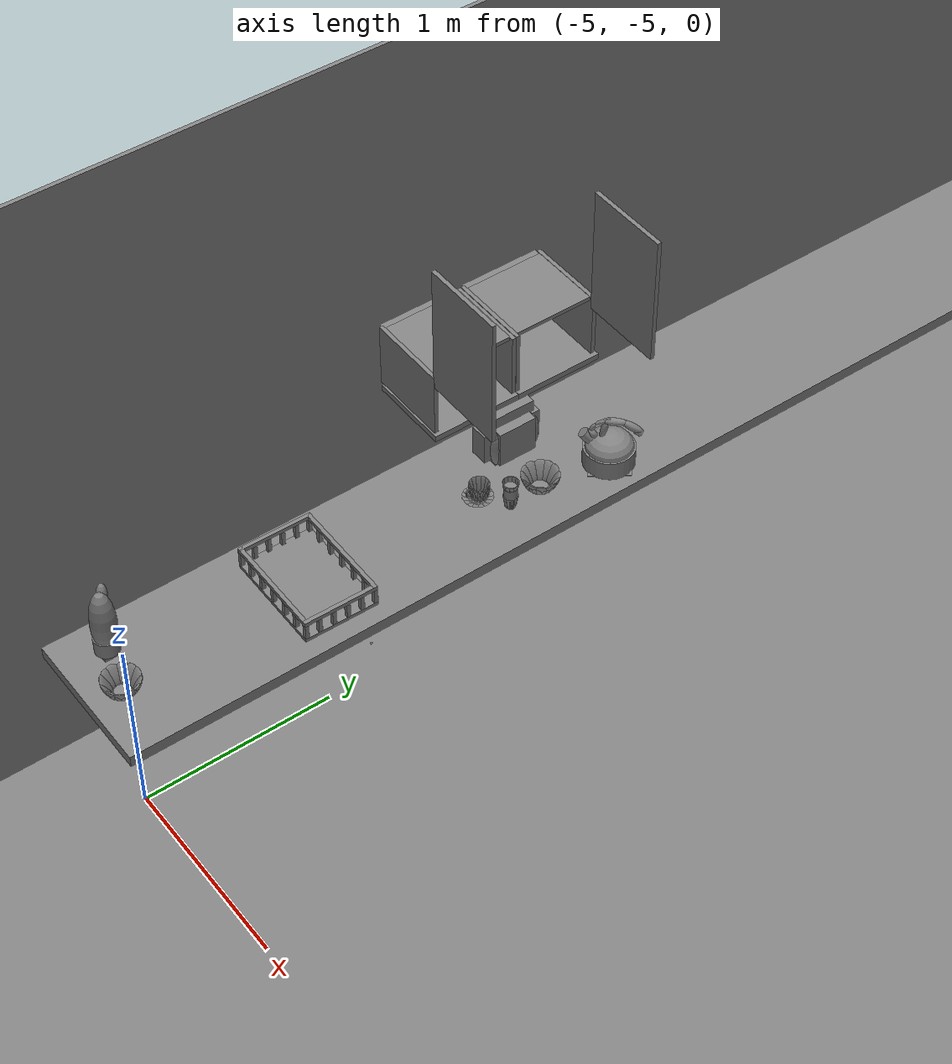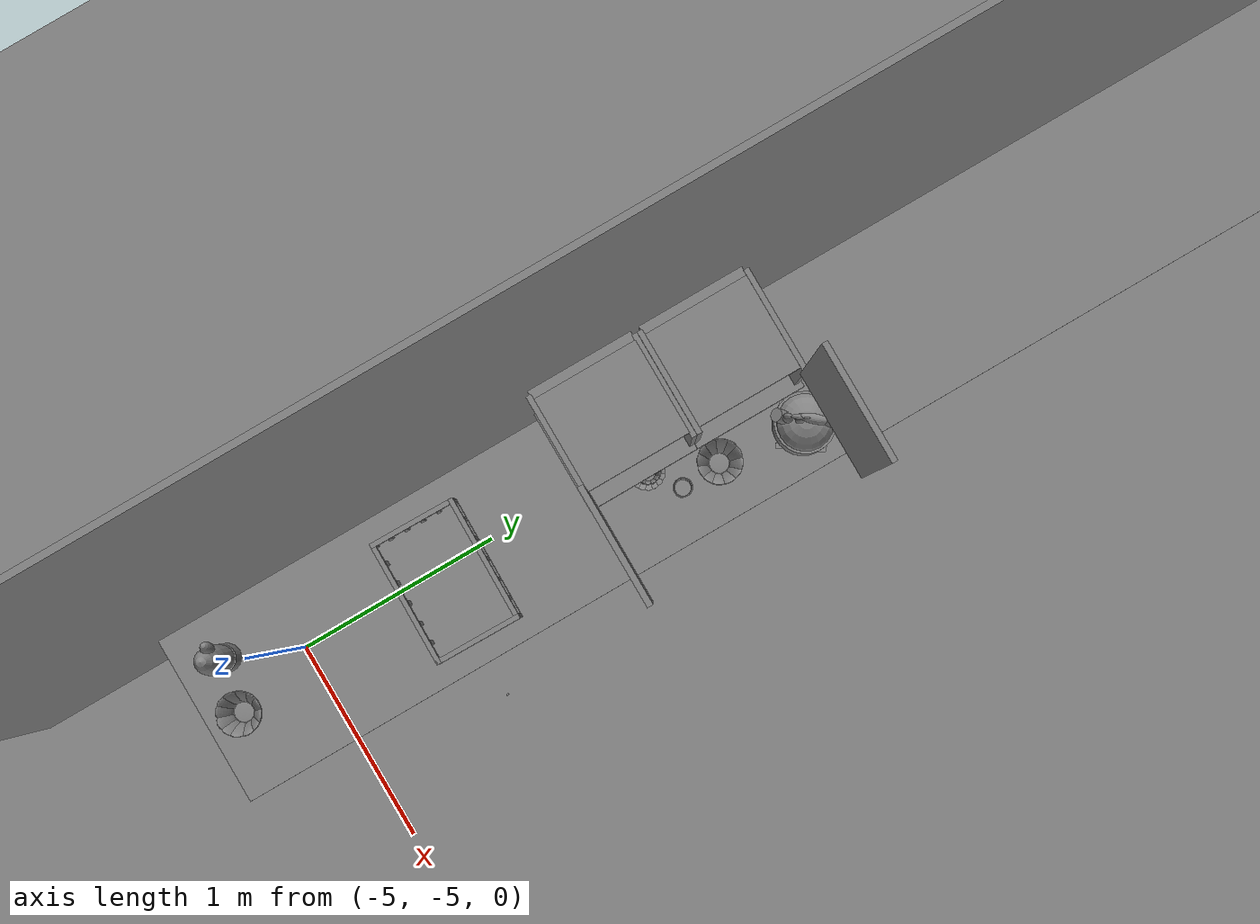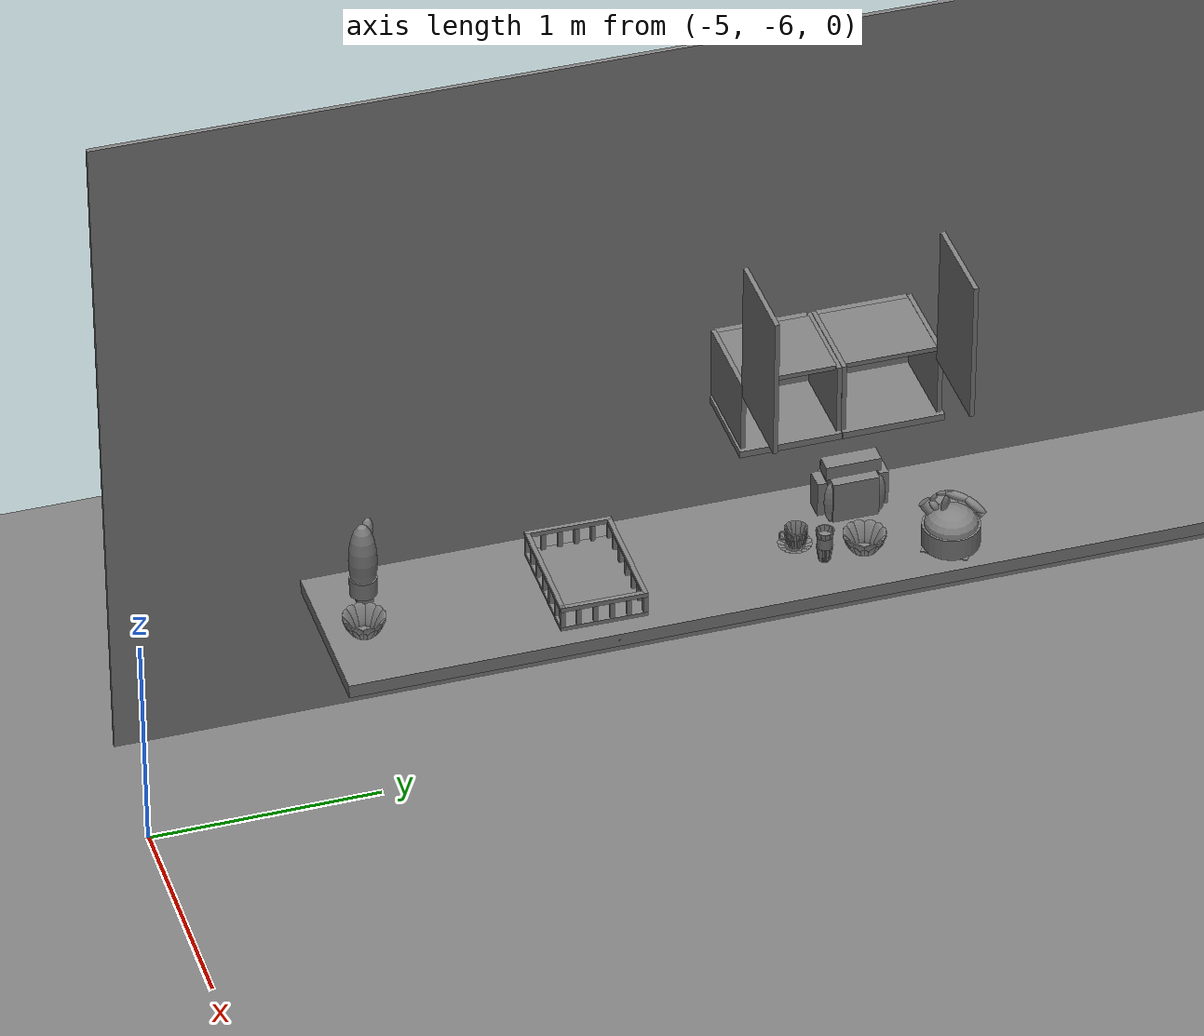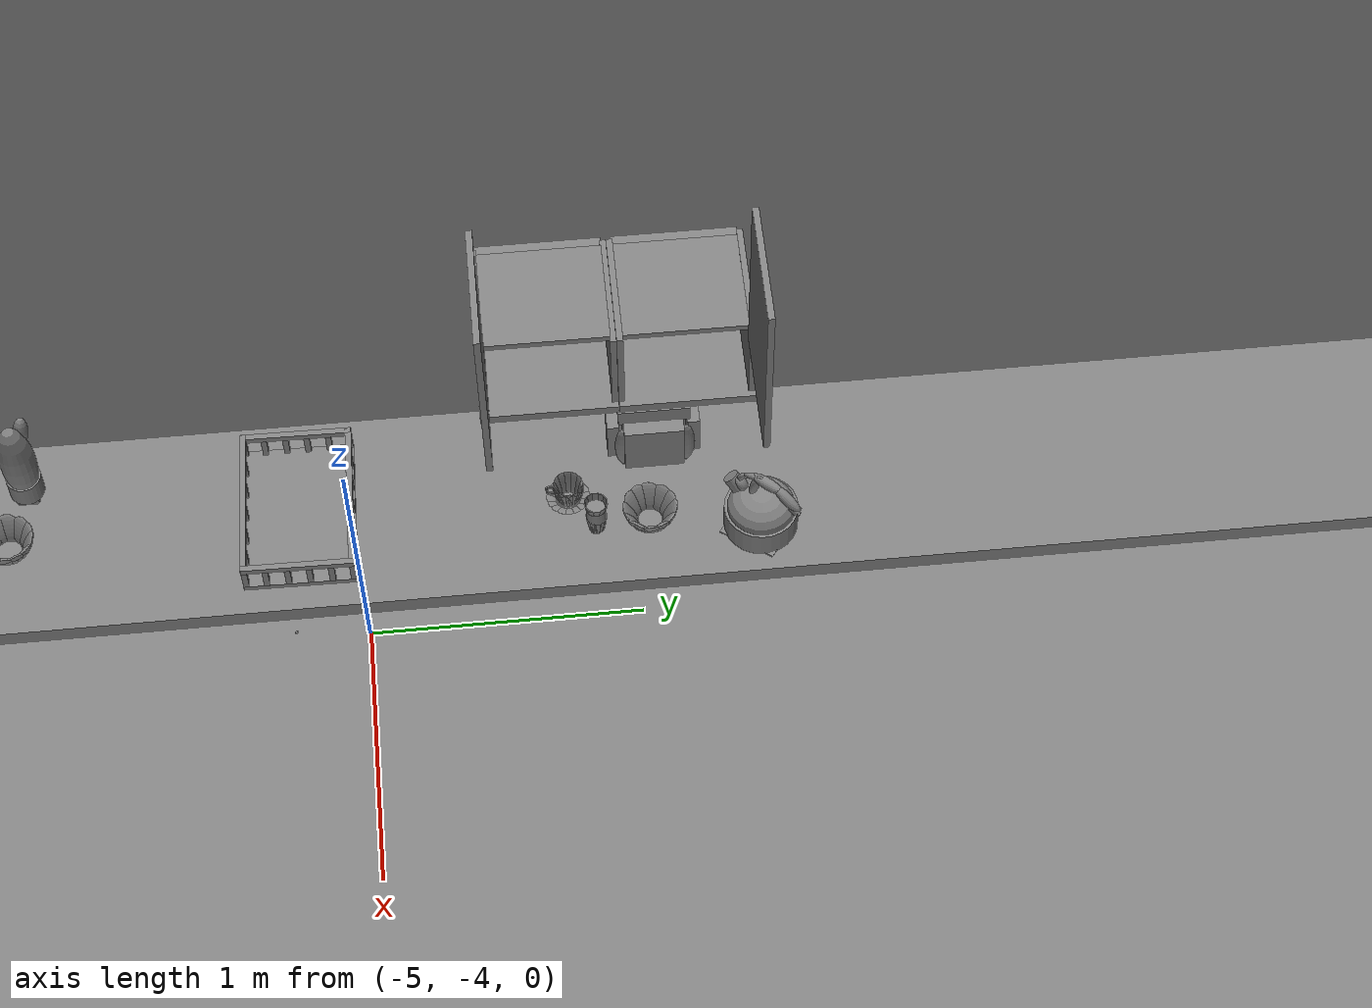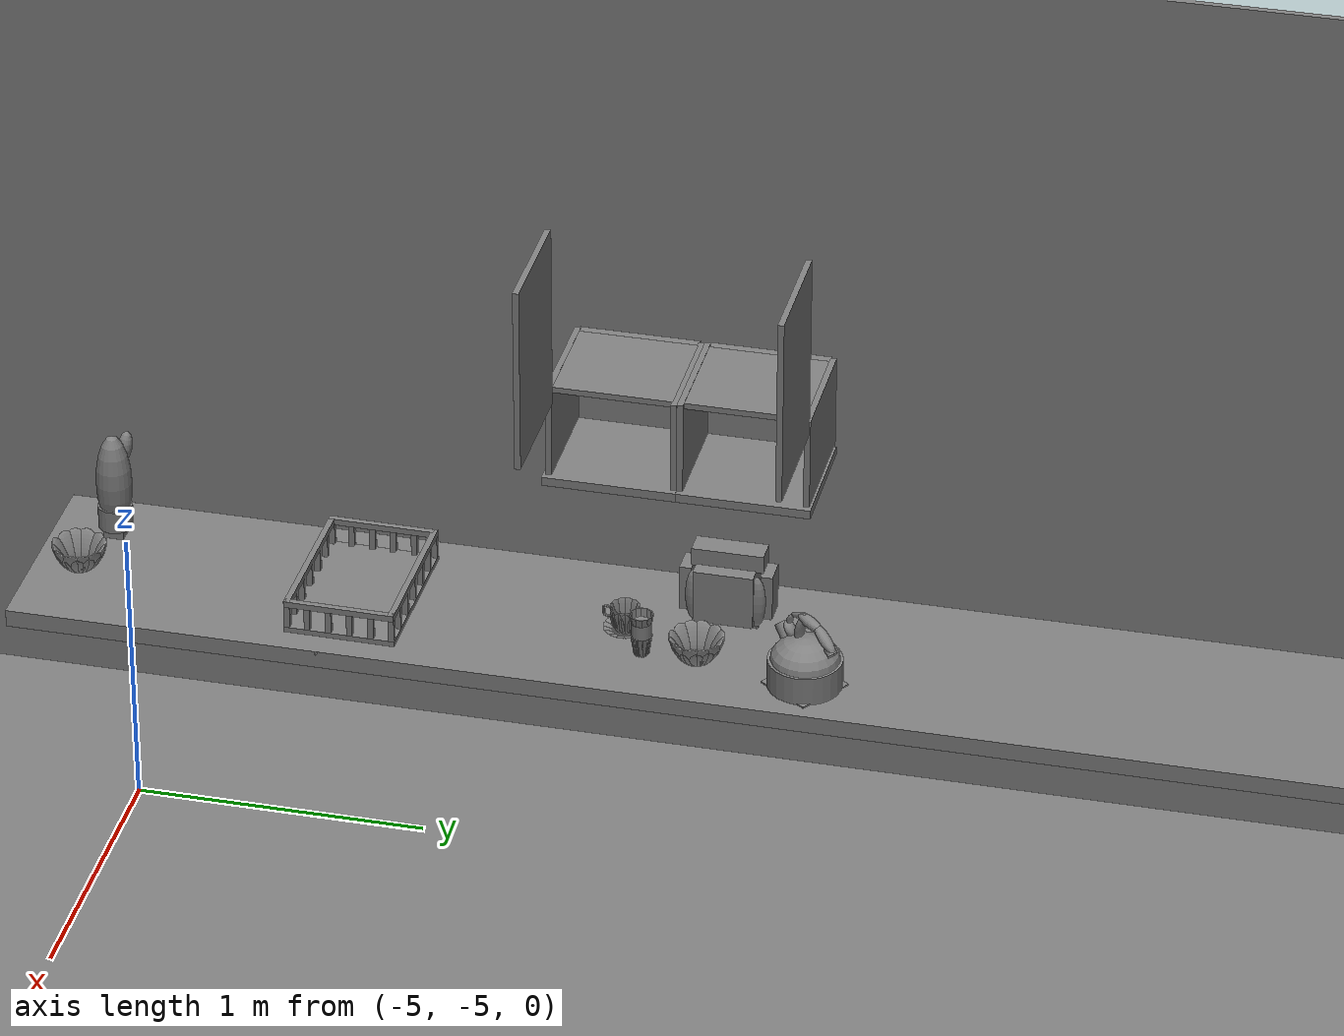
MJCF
<mujoco>
    <option gravity="0.000000000 0.000000000 -9.810000420" timestep="0.0049999999" integrator="implicitfast" density="9.8000002" viscosity="1.8000001e-05" noslip_iterations="10" iterations="100" sdf_iterations="50">
        <flag multiccd="disable"/>
    </option>
    <size memory="1000M"/>
    <compiler coordinate="local"/>
    <worldbody>
        <light cutoff="30" pos="0 1 1" dir="0 -1 -2"/>
        <light cutoff="30" pos="0 -1 1" dir="0 1 -2"/>
        <body pos="-4.721817970 -2.990536690 1.027358174" euler="0.000000000 0.000000000 89.999946594" name="Interactive Objcets_bow_02">
            <geom contype="1" conaffinity="1" density="1000" type="ellipsoid" material="" rgba="0.500000000 0.500000000 0.500000000 1.000000000" solimp="0.899999976 0.949999988 0.001000000" friction="1.000000000 0.005000000 0.000100000" solref="0.020000000 1.000000000" margin="0" condim="3" group="0" pos="0.052321676 -0.040297508 0.044118762" quat="0.919264674 0.076882742 0.225593731 -0.313287675" size="0.010000000 0.039999999 0.052000001" name="Interactive Objcets_geom_0D47B76E_2F77_4361_B17E_6686FD921FCA"/>
            <geom contype="1" conaffinity="1" density="1000" type="ellipsoid" material="" rgba="0.500000000 0.500000000 0.500000000 1.000000000" solimp="0.899999976 0.949999988 0.001000000" friction="1.000000000 0.005000000 0.000100000" solref="0.020000000 1.000000000" margin="0" condim="3" group="0" pos="0.040234569 0.052338600 0.044118762" quat="0.429593176 -0.213750035 -0.105424814 -0.871002913" size="0.010000000 0.039999999 0.052000001" name="Interactive Objcets_geom_1837C6EB_3BCF_4AC4_BA91_3C5FD253FF65"/>
            <geom contype="1" conaffinity="1" density="1000" type="ellipsoid" material="" rgba="0.500000000 0.500000000 0.500000000 1.000000000" solimp="0.899999976 0.949999988 0.001000000" friction="1.000000000 0.005000000 0.000100000" solref="0.020000000 1.000000000" margin="0" condim="3" group="0" pos="0.029448029 -0.059084892 0.044118762" quat="0.825555801 0.125530601 0.202597082 -0.511521280" size="0.010000000 0.039999999 0.052000001" name="Interactive Objcets_geom_5DBE9BAC_5A0F_496D_BA89_4B31FF5203D2"/>
            <geom contype="1" conaffinity="1" density="1000" type="ellipsoid" material="" rgba="0.500000000 0.500000000 0.500000000 1.000000000" solimp="0.899999976 0.949999988 0.001000000" friction="1.000000000 0.005000000 0.000100000" solref="0.020000000 1.000000000" margin="0" condim="3" group="0" pos="-0.058925860 -0.029528141 0.044118762" quat="0.223252773 0.231952101 0.054787740 -0.945174515" size="0.010000000 0.039999999 0.052000001" name="Interactive Objcets_geom_3176F005_8410_47EB_A5C8_962357FC24E1"/>
            <geom contype="1" conaffinity="1" density="1000" type="ellipsoid" material="" rgba="0.500000000 0.500000000 0.500000000 1.000000000" solimp="0.899999976 0.949999988 0.001000000" friction="1.000000000 0.005000000 0.000100000" solref="0.020000000 1.000000000" margin="0" condim="3" group="0" pos="-0.040080305 -0.052354336 0.044118762" quat="0.429593205 0.213749886 0.105425082 -0.871003032" size="0.010000000 0.039999999 0.052000001" name="Interactive Objcets_geom_EF18E196_7D59_4747_B14C_47BE211E3D4C"/>
            <geom contype="1" conaffinity="1" density="1000" type="ellipsoid" material="" rgba="0.500000000 0.500000000 0.500000000 1.000000000" solimp="0.899999976 0.949999988 0.001000000" friction="1.000000000 0.005000000 0.000100000" solref="0.020000000 1.000000000" margin="0" condim="3" group="0" pos="0.000082973 0.000000000 0.005656481" quat="1.000000000 0.000000000 0.000000000 0.000000000" size="0.039999999 0.039999999 0.002000000" name="Interactive Objcets_geom_390011D6_1BD4_4EF0_B76D_108AF2B4BDD2"/>
            <geom contype="1" conaffinity="1" density="1000" type="ellipsoid" material="" rgba="0.500000000 0.500000000 0.500000000 1.000000000" solimp="0.899999976 0.949999988 0.001000000" friction="1.000000000 0.005000000 0.000100000" solref="0.020000000 1.000000000" margin="0" condim="3" group="0" pos="-0.065898418 -0.000007629 0.044118762" quat="0.971183062 -0.000000142 -0.238334835 0.000000030" size="0.010000000 0.039999999 0.052000001" name="Interactive Objcets_geom_53A24CEE_9C30_4D1E_8F32_27B2B31EEBC3"/>
            <geom contype="1" conaffinity="1" density="1000" type="ellipsoid" material="" rgba="0.500000000 0.500000000 0.500000000 1.000000000" solimp="0.899999976 0.949999988 0.001000000" friction="1.000000000 0.005000000 0.000100000" solref="0.020000000 1.000000000" margin="0" condim="3" group="0" pos="-0.000090118 0.065967560 0.044118762" quat="0.687598705 -0.168314859 -0.168741152 -0.685860336" size="0.010000000 0.039999999 0.052000001" name="Interactive Objcets_geom_65B1A4CF_3B1A_47D4_A67F_9CD649F1A4E1"/>
            <geom contype="1" conaffinity="1" density="1000" type="ellipsoid" material="" rgba="0.500000000 0.500000000 0.500000000 1.000000000" solimp="0.899999976 0.949999988 0.001000000" friction="1.000000000 0.005000000 0.000100000" solref="0.020000000 1.000000000" margin="0" condim="3" group="0" pos="-0.052167647 0.040282249 0.044118762" quat="0.919264615 -0.076883025 -0.225593641 -0.313287735" size="0.010000000 0.039999999 0.052000001" name="Interactive Objcets_geom_A8336FF2_747C_4ABE_A037_2A7A3BE8697C"/>
            <geom contype="1" conaffinity="1" density="1000" type="ellipsoid" material="" rgba="0.500000000 0.500000000 0.500000000 1.000000000" solimp="0.899999976 0.949999988 0.001000000" friction="1.000000000 0.005000000 0.000100000" solref="0.020000000 1.000000000" margin="0" condim="3" group="0" pos="0.059080135 0.029512405 0.044118762" quat="0.223252743 -0.231952220 -0.054787420 -0.945174456" size="0.010000000 0.039999999 0.052000001" name="Interactive Objcets_geom_0AF1125B_074B_45EF_9D2B_7292AD851A95"/>
            <geom contype="1" conaffinity="1" density="1000" type="ellipsoid" material="" rgba="0.500000000 0.500000000 0.500000000 1.000000000" solimp="0.899999976 0.949999988 0.001000000" friction="1.000000000 0.005000000 0.000100000" solref="0.020000000 1.000000000" margin="0" condim="3" group="0" pos="0.000243668 -0.065982819 0.044118762" quat="0.687598705 0.168314636 0.168741375 -0.685860336" size="0.010000000 0.039999999 0.052000001" name="Interactive Objcets_geom_212D930B_217F_4047_B859_A1E19601912A"/>
            <geom contype="1" conaffinity="1" density="1000" type="ellipsoid" material="" rgba="0.500000000 0.500000000 0.500000000 1.000000000" solimp="0.899999976 0.949999988 0.001000000" friction="1.000000000 0.005000000 0.000100000" solref="0.020000000 1.000000000" margin="0" condim="3" group="0" pos="0.066052437 -0.000007629 0.044118762" quat="0.971183062 -0.000000156 0.238334835 0.000000030" size="0.010000000 0.039999999 0.052000001" name="Interactive Objcets_geom_B00FF3AF_D9D3_49C8_A477_5DC803380F08"/>
            <geom contype="1" conaffinity="1" density="1000" type="ellipsoid" material="" rgba="0.500000000 0.500000000 0.500000000 1.000000000" solimp="0.899999976 0.949999988 0.001000000" friction="1.000000000 0.005000000 0.000100000" solref="0.020000000 1.000000000" margin="0" condim="3" group="0" pos="0.000082973 0.000000000 0.000446677" quat="1.000000000 0.000000000 0.000000000 0.000000000" size="0.039999999 0.039999999 0.002000000" name="Interactive Objcets_geom_20F903A2_0738_480C_998F_D58E1D98F086"/>
            <geom contype="1" conaffinity="1" density="1000" type="ellipsoid" material="" rgba="0.500000000 0.500000000 0.500000000 1.000000000" solimp="0.899999976 0.949999988 0.001000000" friction="1.000000000 0.005000000 0.000100000" solref="0.020000000 1.000000000" margin="0" condim="3" group="0" pos="-0.029293532 0.059069633 0.044118762" quat="0.825555801 -0.125530809 -0.202596903 -0.511521280" size="0.010000000 0.039999999 0.052000001" name="Interactive Objcets_geom_54F5B7BA_8598_4F80_9A2E_33F9F6DC1E82"/>
            <freejoint name="Interactive Objcets_bow_02"/>
        </body>
        <body pos="1000.000000000 1000.000000000 1.000000000" euler="0.000000000 0.000000000 0.000000000" name="openloong_gripper_2f85_fix_base_usda_bottle_red">
            <geom contype="1" conaffinity="1" density="1000" type="ellipsoid" material="" rgba="0.500000000 0.500000000 0.500000000 1.000000000" solimp="0.899999976 0.949999988 0.001000000" friction="1.000000000 0.005000000 0.000100000" solref="0.020000000 1.000000000" margin="0" condim="3" group="0" pos="0.000000000 0.000000000 0.144284487" quat="1.000000000 0.000000000 0.000000000 0.000000000" size="0.021000000 0.021000000 0.079999998" name="openloong_gripper_2f85_fix_base_usda_geom_263C1C5A_105A_4E0A_9106_68C4E4C66B8C"/>
            <geom contype="1" conaffinity="1" density="1000" type="cylinder" material="" rgba="0.500000000 0.500000000 0.500000000 1.000000000" solimp="0.899999976 0.949999988 0.001000000" friction="1.000000000 0.005000000 0.000100000" solref="0.020000000 1.000000000" margin="0" condim="3" group="0" pos="0.000000000 0.000000000 0.220618963" quat="1.000000000 0.000000000 0.000000000 0.000000000" size="0.016000001 0.010000000 1.000000000" name="openloong_gripper_2f85_fix_base_usda_geom_8F723E52_2977_44F1_BC1C_1F9F87C8F3A1"/>
            <geom contype="1" conaffinity="1" density="1000" type="ellipsoid" material="" rgba="0.500000000 0.500000000 0.500000000 1.000000000" solimp="0.899999976 0.949999988 0.001000000" friction="1.000000000 0.005000000 0.000100000" solref="0.020000000 1.000000000" margin="0" condim="3" group="0" pos="0.000000000 0.000000000 0.118945479" quat="1.000000000 0.000000000 0.000000000 0.000000000" size="0.030999999 0.030999999 0.029999999" name="openloong_gripper_2f85_fix_base_usda_geom_5C916FB8_B23A_4D41_A4E8_4B1F4624E201"/>
            <geom contype="1" conaffinity="1" density="1000" type="box" material="" rgba="0.500000000 0.500000000 0.500000000 1.000000000" solimp="0.899999976 0.949999988 0.001000000" friction="1.000000000 0.005000000 0.000100000" solref="0.020000000 1.000000000" margin="0" condim="3" group="0" pos="0.000000000 0.000000000 0.002189159" quat="1.000000000 0.000000000 0.000000000 0.000000000" size="0.020000000 0.020000000 0.003000000" name="openloong_gripper_2f85_fix_base_usda_geom_C481239E_8FE1_4F35_9694_E49BB63E78AE"/>
            <geom contype="1" conaffinity="1" density="1000" type="cylinder" material="" rgba="0.500000000 0.500000000 0.500000000 1.000000000" solimp="0.899999976 0.949999988 0.001000000" friction="1.000000000 0.005000000 0.000100000" solref="0.020000000 1.000000000" margin="0" condim="3" group="0" pos="0.000000000 -0.000366211 0.060884237" quat="1.000000000 0.000000000 0.000000000 0.000000000" size="0.030999999 0.057999998 1.000000000" name="openloong_gripper_2f85_fix_base_usda_geom_E5D57912_6DCA_4E9A_9B7A_861A5A606D10"/>
            <freejoint name="openloong_gripper_2f85_fix_base_usda_bottle_red_joint"/>
            <site size="0.005000000 0.005000000 0.005000000" rgba="0.500000000 0.500000000 0.500000000 1.000000000" pos="0.000000000 0.000000000 0.000000000" quat="0.999961913 0.008726535 0.000000000 0.000000000" group="0" type="sphere" name="openloong_gripper_2f85_fix_base_usda_bottle_redsite"/>
        </body>
        <body pos="1000.000000000 1000.000000000 1.000000000" euler="0.000000000 0.000000000 0.000000000" name="openloong_gripper_2f85_fix_base_usda_jar_01">
            <geom contype="1" conaffinity="1" density="1000" type="box" material="" rgba="0.500000000 0.500000000 0.500000000 1.000000000" solimp="0.899999976 0.949999988 0.001000000" friction="1.000000000 0.005000000 0.000100000" solref="0.020000000 1.000000000" margin="0" condim="3" group="0" pos="0.000000000 0.000000000 0.006158113" quat="1.000000000 0.000000000 0.000000000 0.000000000" size="0.020000000 0.020000000 0.005000000" name="openloong_gripper_2f85_fix_base_usda_geom_CF89F899_D910_4AA2_AA2D_40DC54D996A9"/>
            <geom contype="1" conaffinity="1" density="1000" type="cylinder" material="" rgba="0.500000000 0.500000000 0.500000000 1.000000000" solimp="0.899999976 0.949999988 0.001000000" friction="1.000000000 0.005000000 0.000100000" solref="0.020000000 1.000000000" margin="0" condim="3" group="0" pos="0.000000000 0.000000000 0.062744498" quat="1.000000000 0.000000000 0.000000000 0.000000000" size="0.041000001 0.052999999 1.000000000" name="openloong_gripper_2f85_fix_base_usda_geom_E51D3B55_639E_4FDB_BDA6_06965BBB4B7F"/>
            <geom contype="1" conaffinity="1" density="1000" type="ellipsoid" material="" rgba="0.500000000 0.500000000 0.500000000 1.000000000" solimp="0.899999976 0.949999988 0.001000000" friction="1.000000000 0.005000000 0.000100000" solref="0.020000000 1.000000000" margin="0" condim="3" group="0" pos="0.000000000 0.000000000 0.122252703" quat="1.000000000 0.000000000 0.000000000 0.000000000" size="0.035999998 0.035999998 0.010000000" name="openloong_gripper_2f85_fix_base_usda_geom_2ACB506C_7FCE_4F79_A03B_660911E4D089"/>
            <geom contype="1" conaffinity="1" density="1000" type="cylinder" material="" rgba="0.500000000 0.500000000 0.500000000 1.000000000" solimp="0.899999976 0.949999988 0.001000000" friction="1.000000000 0.005000000 0.000100000" solref="0.020000000 1.000000000" margin="0" condim="3" group="0" pos="0.000000000 0.000000000 0.015747190" quat="1.000000000 0.000000000 0.000000000 0.000000000" size="0.035000000 0.010000000 1.000000000" name="openloong_gripper_2f85_fix_base_usda_geom_95578823_02AA_418C_B9AC_7F1A8A3C5698"/>
            <geom contype="1" conaffinity="1" density="1000" type="ellipsoid" material="" rgba="0.500000000 0.500000000 0.500000000 1.000000000" solimp="0.899999976 0.949999988 0.001000000" friction="1.000000000 0.005000000 0.000100000" solref="0.020000000 1.000000000" margin="0" condim="3" group="0" pos="0.000000000 0.000000000 0.115815401" quat="1.000000000 0.000000000 0.000000000 0.000000000" size="0.039999999 0.039999999 0.010000000" name="openloong_gripper_2f85_fix_base_usda_geom_562F76C6_F92D_47E1_95C7_A1D5BCA7D77C"/>
            <geom contype="1" conaffinity="1" density="1000" type="cylinder" material="" rgba="0.500000000 0.500000000 0.500000000 1.000000000" solimp="0.899999976 0.949999988 0.001000000" friction="1.000000000 0.005000000 0.000100000" solref="0.020000000 1.000000000" margin="0" condim="3" group="0" pos="0.000000000 0.000000000 0.133183479" quat="1.000000000 0.000000000 0.000000000 0.000000000" size="0.037999999 0.006500000 1.000000000" name="openloong_gripper_2f85_fix_base_usda_geom_B37BA88E_887F_4E52_841C_69BDFFBC802B"/>
            <freejoint name="openloong_gripper_2f85_fix_base_usda_jar_01_joint"/>
            <site size="0.005000000 0.005000000 0.005000000" rgba="0.500000000 0.500000000 0.500000000 1.000000000" pos="0.000000000 0.000000000 0.000000000" quat="1.000000000 0.000000000 0.000000000 0.000000000" group="0" type="sphere" name="openloong_gripper_2f85_fix_base_usda_jar_01site"/>
        </body>
        <body pos="1000.000000000 1000.000000000 1.000000000" euler="0.000000000 0.000000000 0.000000000" name="openloong_gripper_2f85_fix_base_usda_salt">
            <geom contype="1" conaffinity="1" density="1000" type="box" material="" rgba="0.500000000 0.500000000 0.500000000 1.000000000" solimp="0.899999976 0.949999988 0.001000000" friction="1.000000000 0.005000000 0.000100000" solref="0.020000000 1.000000000" margin="0" condim="3" group="0" pos="0.000305176 0.000000000 0.084862232" quat="1.000000000 0.000000000 0.000000000 0.000000000" size="0.048999999 0.018999999 0.005000000" name="openloong_gripper_2f85_fix_base_usda_geom_EB71E7BC_E241_4475_99AE_82A822C51912"/>
            <geom contype="1" conaffinity="1" density="1000" type="box" material="" rgba="0.500000000 0.500000000 0.500000000 1.000000000" solimp="0.899999976 0.949999988 0.001000000" friction="1.000000000 0.005000000 0.000100000" solref="0.020000000 1.000000000" margin="0" condim="3" group="0" pos="0.000305176 0.000000000 0.104564309" quat="1.000000000 0.000000000 0.000000000 0.000000000" size="0.052000001 0.014000000 0.005000000" name="openloong_gripper_2f85_fix_base_usda_geom_A032CCBE_0E3B_4380_B35A_3AF2A37E7EA6"/>
            <geom contype="1" conaffinity="1" density="1000" type="box" material="" rgba="0.500000000 0.500000000 0.500000000 1.000000000" solimp="0.899999976 0.949999988 0.001000000" friction="1.000000000 0.005000000 0.000100000" solref="0.020000000 1.000000000" margin="0" condim="3" group="0" pos="0.000305176 0.000000000 0.114487171" quat="1.000000000 0.000000000 0.000000000 0.000000000" size="0.054000001 0.011500000 0.005000000" name="openloong_gripper_2f85_fix_base_usda_geom_9B370AFF_76CA_4FE2_B20E_12E581ABB174"/>
            <geom contype="1" conaffinity="1" density="1000" type="box" material="" rgba="0.500000000 0.500000000 0.500000000 1.000000000" solimp="0.899999976 0.949999988 0.001000000" friction="1.000000000 0.005000000 0.000100000" solref="0.020000000 1.000000000" margin="0" condim="3" group="0" pos="0.000305176 0.000000000 0.075103164" quat="1.000000000 0.000000000 0.000000000 0.000000000" size="0.048000000 0.020000000 0.005000000" name="openloong_gripper_2f85_fix_base_usda_geom_4F84881D_99F5_47D0_BB62_0DF19D9743E5"/>
            <geom contype="1" conaffinity="1" density="1000" type="box" material="" rgba="0.500000000 0.500000000 0.500000000 1.000000000" solimp="0.899999976 0.949999988 0.001000000" friction="1.000000000 0.005000000 0.000100000" solref="0.020000000 1.000000000" margin="0" condim="3" group="0" pos="0.000305176 0.000000000 0.134892464" quat="1.000000000 0.000000000 0.000000000 0.000000000" size="0.057000000 0.007000000 0.005000000" name="openloong_gripper_2f85_fix_base_usda_geom_3215A5DD_D17E_4798_AF32_400D462FDB06"/>
            <geom contype="1" conaffinity="1" density="1000" type="box" material="" rgba="0.500000000 0.500000000 0.500000000 1.000000000" solimp="0.899999976 0.949999988 0.001000000" friction="1.000000000 0.005000000 0.000100000" solref="0.020000000 1.000000000" margin="0" condim="3" group="0" pos="0.000305176 0.000000000 0.094920278" quat="1.000000000 0.000000000 0.000000000 0.000000000" size="0.050000001 0.017000001 0.005000000" name="openloong_gripper_2f85_fix_base_usda_geom_445A62A4_087C_4F33_90F1_87121E99D78D"/>
            <geom contype="1" conaffinity="1" density="1000" type="box" material="" rgba="0.500000000 0.500000000 0.500000000 1.000000000" solimp="0.899999976 0.949999988 0.001000000" friction="1.000000000 0.005000000 0.000100000" solref="0.020000000 1.000000000" margin="0" condim="3" group="0" pos="0.000305176 0.000000000 0.065204859" quat="1.000000000 0.000000000 0.000000000 0.000000000" size="0.045000002 0.021000000 0.005000000" name="openloong_gripper_2f85_fix_base_usda_geom_3B00915F_C875_4F08_9365_2EED0C5C259C"/>
            <geom contype="1" conaffinity="1" density="1000" type="box" material="" rgba="0.500000000 0.500000000 0.500000000 1.000000000" solimp="0.899999976 0.949999988 0.001000000" friction="1.000000000 0.005000000 0.000100000" solref="0.020000000 1.000000000" margin="0" condim="3" group="0" pos="0.000305176 0.000000000 0.144135714" quat="1.000000000 0.000000000 0.000000000 0.000000000" size="0.059000000 0.005000000 0.004000000" name="openloong_gripper_2f85_fix_base_usda_geom_35B1CDD4_454D_4E54_82B3_5DBD2A0686BC"/>
            <geom contype="1" conaffinity="1" density="1000" type="box" material="" rgba="0.500000000 0.500000000 0.500000000 1.000000000" solimp="0.899999976 0.949999988 0.001000000" friction="1.000000000 0.005000000 0.000100000" solref="0.020000000 1.000000000" margin="0" condim="3" group="0" pos="0.000000000 0.000000000 0.031593561" quat="1.000000000 0.000000000 0.000000000 0.000000000" size="0.041999999 0.024000000 0.029999999" name="openloong_gripper_2f85_fix_base_usda_geom_E032AD4D_C6A9_4D84_83B4_E02F77A2EE0C"/>
            <geom contype="1" conaffinity="1" density="1000" type="box" material="" rgba="0.500000000 0.500000000 0.500000000 1.000000000" solimp="0.899999976 0.949999988 0.001000000" friction="1.000000000 0.005000000 0.000100000" solref="0.020000000 1.000000000" margin="0" condim="3" group="0" pos="0.000305176 0.000000000 0.124608755" quat="1.000000000 0.000000000 0.000000000 0.000000000" size="0.055000000 0.008000000 0.005000000" name="openloong_gripper_2f85_fix_base_usda_geom_871F017E_DF59_4C2F_9282_E9BA76D5DFB1"/>
            <freejoint name="openloong_gripper_2f85_fix_base_usda_salt_joint"/>
            <site size="0.005000000 0.005000000 0.005000000" rgba="0.500000000 0.500000000 0.500000000 1.000000000" pos="0.000000000 0.000000000 0.000000000" quat="1.000000000 0.000000000 0.000000000 0.000000000" group="0" type="sphere" name="openloong_gripper_2f85_fix_base_usda_saltsite"/>
        </body>
        <body pos="-4.328573704 -4.197713375 1.827686071" euler="-17.773441315 -42.322265625 -114.224113464" mocap="true" name="spotlight6_SpotLight"/>
        <body pos="-4.067557812 -3.985352278 1.832593799" euler="152.014053345 -32.391227722 141.899658203" mocap="true" name="spotlight2_SpotLight"/>
        <body pos="-4.416769981 -4.009316921 1.917031765" euler="36.097625732 51.520191193 175.330902100" mocap="true" name="spotlight1_SpotLight"/>
        <body pos="1000.000000000 1000.000000000 1.000000000" euler="0.000000000 0.000000000 0.000000000" name="openloong_gripper_2f85_fix_base_usda_bow_yellow_kps">
            <geom contype="1" conaffinity="1" density="1000" type="ellipsoid" material="" rgba="0.500000000 0.500000000 0.500000000 1.000000000" solimp="0.899999976 0.949999988 0.001000000" friction="1.000000000 0.005000000 0.000100000" solref="0.020000000 1.000000000" margin="0" condim="3" group="0" pos="-0.052185059 0.040283203 0.044118762" quat="0.919264615 -0.076883033 -0.225593656 -0.313287765" size="0.010000000 0.039999999 0.052000001" name="openloong_gripper_2f85_fix_base_usda_geom_CF21B0D3_F318_4A2D_991F_D88B0A5C3454"/>
            <geom contype="1" conaffinity="1" density="1000" type="ellipsoid" material="" rgba="0.500000000 0.500000000 0.500000000 1.000000000" solimp="0.899999976 0.949999988 0.001000000" friction="1.000000000 0.005000000 0.000100000" solref="0.020000000 1.000000000" margin="0" condim="3" group="0" pos="-0.000061035 0.065979004 0.044118762" quat="0.687598765 -0.168314874 -0.168741167 -0.685860336" size="0.010000000 0.039999999 0.052000001" name="openloong_gripper_2f85_fix_base_usda_geom_2E1E5D53_2166_49E5_8CC9_FF60C180681C"/>
            <geom contype="1" conaffinity="1" density="1000" type="box" material="" rgba="0.500000000 0.500000000 0.500000000 1.000000000" solimp="0.899999976 0.949999988 0.001000000" friction="1.000000000 0.005000000 0.000100000" solref="0.020000000 1.000000000" margin="0" condim="3" group="0" pos="0.000061035 0.000000000 -0.002001643" quat="1.000000000 0.000000000 0.000000000 0.000000000" size="0.029999999 0.029999999 0.002000000" name="openloong_gripper_2f85_fix_base_usda_geom_A378A118_6BAE_47C6_A3C9_F7EFD578C839"/>
            <geom contype="1" conaffinity="1" density="1000" type="ellipsoid" material="" rgba="0.500000000 0.500000000 0.500000000 1.000000000" solimp="0.899999976 0.949999988 0.001000000" friction="1.000000000 0.005000000 0.000100000" solref="0.020000000 1.000000000" margin="0" condim="3" group="0" pos="0.029418945 -0.059082031 0.044118762" quat="0.825555861 0.125530601 0.202597082 -0.511521280" size="0.010000000 0.039999999 0.052000001" name="openloong_gripper_2f85_fix_base_usda_geom_1792DD34_E0A5_4FFD_A709_7623D4C14087"/>
            <geom contype="1" conaffinity="1" density="1000" type="ellipsoid" material="" rgba="0.500000000 0.500000000 0.500000000 1.000000000" solimp="0.899999976 0.949999988 0.001000000" friction="1.000000000 0.005000000 0.000100000" solref="0.020000000 1.000000000" margin="0" condim="3" group="0" pos="0.000244141 -0.065979004 0.044118762" quat="0.687598765 0.168314651 0.168741375 -0.685860336" size="0.010000000 0.039999999 0.052000001" name="openloong_gripper_2f85_fix_base_usda_geom_928E415D_2FE4_48E5_ABEA_5B91486B4728"/>
            <geom contype="1" conaffinity="1" density="1000" type="ellipsoid" material="" rgba="0.500000000 0.500000000 0.500000000 1.000000000" solimp="0.899999976 0.949999988 0.001000000" friction="1.000000000 0.005000000 0.000100000" solref="0.020000000 1.000000000" margin="0" condim="3" group="0" pos="0.000061035 0.000000000 0.000446677" quat="1.000000000 0.000000000 0.000000000 0.000000000" size="0.039999999 0.039999999 0.002000000" name="openloong_gripper_2f85_fix_base_usda_geom_68451D21_FDE1_4A34_A42F_0618057910BA"/>
            <geom contype="1" conaffinity="1" density="1000" type="ellipsoid" material="" rgba="0.500000000 0.500000000 0.500000000 1.000000000" solimp="0.899999976 0.949999988 0.001000000" friction="1.000000000 0.005000000 0.000100000" solref="0.020000000 1.000000000" margin="0" condim="3" group="0" pos="0.059082031 0.029541016 0.044118762" quat="0.223252773 -0.231952220 -0.054787423 -0.945174456" size="0.010000000 0.039999999 0.052000001" name="openloong_gripper_2f85_fix_base_usda_geom_42358F3B_C8E2_414A_8880_671D82457EFF"/>
            <geom contype="1" conaffinity="1" density="1000" type="ellipsoid" material="" rgba="0.500000000 0.500000000 0.500000000 1.000000000" solimp="0.899999976 0.949999988 0.001000000" friction="1.000000000 0.005000000 0.000100000" solref="0.020000000 1.000000000" margin="0" condim="3" group="0" pos="0.000061035 0.000000000 0.007335305" quat="1.000000000 0.000000000 0.000000000 0.000000000" size="0.039999999 0.039999999 0.002000000" name="openloong_gripper_2f85_fix_base_usda_geom_20BB9D90_EA31_4E6B_ABC9_7AFC55F31780"/>
            <geom contype="1" conaffinity="1" density="1000" type="ellipsoid" material="" rgba="0.500000000 0.500000000 0.500000000 1.000000000" solimp="0.899999976 0.949999988 0.001000000" friction="1.000000000 0.005000000 0.000100000" solref="0.020000000 1.000000000" margin="0" condim="3" group="0" pos="-0.029296875 0.059082031 0.044118762" quat="0.825555861 -0.125530809 -0.202596918 -0.511521280" size="0.010000000 0.039999999 0.052000001" name="openloong_gripper_2f85_fix_base_usda_geom_1ECE6817_05B6_4D59_8502_69EFAF0BED76"/>
            <geom contype="1" conaffinity="1" density="1000" type="ellipsoid" material="" rgba="0.500000000 0.500000000 0.500000000 1.000000000" solimp="0.899999976 0.949999988 0.001000000" friction="1.000000000 0.005000000 0.000100000" solref="0.020000000 1.000000000" margin="0" condim="3" group="0" pos="0.040222168 0.052368164 0.044118762" quat="0.429593176 -0.213750049 -0.105424821 -0.871002972" size="0.010000000 0.039999999 0.052000001" name="openloong_gripper_2f85_fix_base_usda_geom_C096D907_1DE9_41FC_859E_AF0AE2464E45"/>
            <geom contype="1" conaffinity="1" density="1000" type="ellipsoid" material="" rgba="0.500000000 0.500000000 0.500000000 1.000000000" solimp="0.899999976 0.949999988 0.001000000" friction="1.000000000 0.005000000 0.000100000" solref="0.020000000 1.000000000" margin="0" condim="3" group="0" pos="0.066040039 0.000000000 0.044118762" quat="0.971183062 -0.000000156 0.238334835 0.000000030" size="0.010000000 0.039999999 0.052000001" name="openloong_gripper_2f85_fix_base_usda_geom_9B526702_3C02_402F_BF54_EDFF2D796538"/>
            <geom contype="1" conaffinity="1" density="1000" type="ellipsoid" material="" rgba="0.500000000 0.500000000 0.500000000 1.000000000" solimp="0.899999976 0.949999988 0.001000000" friction="1.000000000 0.005000000 0.000100000" solref="0.020000000 1.000000000" margin="0" condim="3" group="0" pos="0.052307129 -0.040283203 0.044118762" quat="0.919264674 0.076882750 0.225593731 -0.313287705" size="0.010000000 0.039999999 0.052000001" name="openloong_gripper_2f85_fix_base_usda_geom_A7DFE8AC_97EC_4341_BB71_1262D9B5090A"/>
            <geom contype="1" conaffinity="1" density="1000" type="ellipsoid" material="" rgba="0.500000000 0.500000000 0.500000000 1.000000000" solimp="0.899999976 0.949999988 0.001000000" friction="1.000000000 0.005000000 0.000100000" solref="0.020000000 1.000000000" margin="0" condim="3" group="0" pos="-0.065917969 0.000000000 0.044118762" quat="0.971183062 -0.000000142 -0.238334835 0.000000030" size="0.010000000 0.039999999 0.052000001" name="openloong_gripper_2f85_fix_base_usda_geom_DB935DFC_18DA_4EE0_BB78_2841BAE248D9"/>
            <geom contype="1" conaffinity="1" density="1000" type="ellipsoid" material="" rgba="0.500000000 0.500000000 0.500000000 1.000000000" solimp="0.899999976 0.949999988 0.001000000" friction="1.000000000 0.005000000 0.000100000" solref="0.020000000 1.000000000" margin="0" condim="3" group="0" pos="-0.058898926 -0.029541016 0.044118762" quat="0.223252758 0.231952101 0.054787733 -0.945174575" size="0.010000000 0.039999999 0.052000001" name="openloong_gripper_2f85_fix_base_usda_geom_852BBFDF_C943_4B34_8658_F9ABBD2195FA"/>
            <geom contype="1" conaffinity="1" density="1000" type="ellipsoid" material="" rgba="0.500000000 0.500000000 0.500000000 1.000000000" solimp="0.899999976 0.949999988 0.001000000" friction="1.000000000 0.005000000 0.000100000" solref="0.020000000 1.000000000" margin="0" condim="3" group="0" pos="-0.040100098 -0.052368164 0.044118762" quat="0.429593235 0.213749886 0.105425082 -0.871003032" size="0.010000000 0.039999999 0.052000001" name="openloong_gripper_2f85_fix_base_usda_geom_0E85EC67_B13A_479E_AFC8_AD254EDC6E3F"/>
            <freejoint name="openloong_gripper_2f85_fix_base_usda_bow_yellow_kps_joint"/>
            <site size="0.005000000 0.005000000 0.005000000" rgba="0.500000000 0.500000000 0.500000000 1.000000000" pos="0.000000000 0.000000000 0.000000000" quat="0.999961913 0.008726534 0.000000000 0.000000000" group="0" type="sphere" name="openloong_gripper_2f85_fix_base_usda_bow_yellow_kps"/>
        </body>
        <body pos="1000.000000000 1000.000000000 1.000000000" euler="0.000000000 0.000000000 0.000000000" name="openloong_gripper_2f85_fix_base_usda_coffeecup_white_kps">
            <geom contype="1" conaffinity="1" density="1000" type="capsule" material="" rgba="0.500000000 0.500000000 0.500000000 1.000000000" solimp="0.899999976 0.949999988 0.001000000" friction="1.000000000 0.005000000 0.000100000" solref="0.020000000 1.000000000" margin="0" condim="3" group="0" pos="-0.000854492 -0.065795898 0.050029993" quat="0.343559504 -0.613204718 0.626912475 0.336047262" size="0.004000000 0.005000000 1.000000000" name="openloong_gripper_2f85_fix_base_usda_geom_B0984EF6_11CD_4AA3_8C19_1E71B5E8AB6C"/>
            <geom contype="1" conaffinity="1" density="1000" type="ellipsoid" material="" rgba="0.500000000 0.500000000 0.500000000 1.000000000" solimp="0.899999976 0.949999988 0.001000000" friction="1.000000000 0.005000000 0.000100000" solref="0.020000000 1.000000000" margin="0" condim="3" group="0" pos="-0.000793457 -0.038452148 0.048040152" quat="0.711656272 0.066323131 -0.067805752 0.696095467" size="0.005000000 0.029999999 0.048999999" name="openloong_gripper_2f85_fix_base_usda_geom_D9CF4DB1_273F_4D3C_9992_B48E752058FF"/>
            <geom contype="1" conaffinity="1" density="1000" type="ellipsoid" material="" rgba="0.500000000 0.500000000 0.500000000 1.000000000" solimp="0.899999976 0.949999988 0.001000000" friction="1.000000000 0.005000000 0.000100000" solref="0.020000000 1.000000000" margin="0" condim="3" group="0" pos="0.037719727 -0.001892090 0.048040152" quat="0.995387912 0.001371633 0.094835162 -0.014391154" size="0.005000000 0.029999999 0.048999999" name="openloong_gripper_2f85_fix_base_usda_geom_5F8A6493_8369_4F2A_B685_F4C219535F60"/>
            <geom contype="1" conaffinity="1" density="1000" type="ellipsoid" material="" rgba="0.500000000 0.500000000 0.500000000 1.000000000" solimp="0.899999976 0.949999988 0.001000000" friction="1.000000000 0.005000000 0.000100000" solref="0.020000000 1.000000000" margin="0" condim="3" group="0" pos="0.033996582 0.015502930 0.048040152" quat="0.970659733 -0.021051638 0.092478797 0.220962167" size="0.005000000 0.029999999 0.048999999" name="openloong_gripper_2f85_fix_base_usda_geom_F0BF5F3E_A5C7_4C50_8705_BFF9DD0125CD"/>
            <geom contype="1" conaffinity="1" density="1000" type="box" material="" rgba="0.500000000 0.500000000 0.500000000 1.000000000" solimp="0.899999976 0.949999988 0.001000000" friction="1.000000000 0.005000000 0.000100000" solref="0.020000000 1.000000000" margin="0" condim="3" group="0" pos="0.000793457 -0.000183105 0.000156164" quat="0.714879215 0.000000000 0.000000000 0.699247897" size="0.020000000 0.020000000 0.002000000" name="openloong_gripper_2f85_fix_base_usda_geom_05944E46_4481_4BA3_B923_420F01A801BD"/>
            <geom contype="1" conaffinity="1" density="1000" type="ellipsoid" material="" rgba="0.500000000 0.500000000 0.500000000 1.000000000" solimp="0.899999976 0.949999988 0.001000000" friction="1.000000000 0.005000000 0.000100000" solref="0.020000000 1.000000000" margin="0" condim="3" group="0" pos="-0.019409180 -0.033081055 0.048040152" quat="0.866879702 0.046630561 -0.082595348 0.489411235" size="0.005000000 0.029999999 0.048999999" name="openloong_gripper_2f85_fix_base_usda_geom_BB4A18D1_EDA1_49B0_A144_68BA944ACFE1"/>
            <geom contype="1" conaffinity="1" density="1000" type="ellipsoid" material="" rgba="0.500000000 0.500000000 0.500000000 1.000000000" solimp="0.899999976 0.949999988 0.001000000" friction="1.000000000 0.005000000 0.000100000" solref="0.020000000 1.000000000" margin="0" condim="3" group="0" pos="-0.016052246 0.033264160 0.048040152" quat="0.840792537 -0.050782297 -0.080109790 -0.532983541" size="0.005000000 0.029999999 0.048999999" name="openloong_gripper_2f85_fix_base_usda_geom_5BF7C4A0_66D3_4007_95B5_E8B1B5E3ABB6"/>
            <geom contype="1" conaffinity="1" density="1000" type="capsule" material="" rgba="0.500000000 0.500000000 0.500000000 1.000000000" solimp="0.899999976 0.949999988 0.001000000" friction="1.000000000 0.005000000 0.000100000" solref="0.020000000 1.000000000" margin="0" condim="3" group="0" pos="-0.000549316 -0.053527832 0.046825886" quat="0.505496025 -0.494442940 0.505495846 0.494442940" size="0.004000000 0.005000000 1.000000000" name="openloong_gripper_2f85_fix_base_usda_geom_20B3E5DE_7CF7_4809_BA2A_5E43A422B408"/>
            <geom contype="1" conaffinity="1" density="1000" type="ellipsoid" material="" rgba="0.500000000 0.500000000 0.500000000 1.000000000" solimp="0.899999976 0.949999988 0.001000000" friction="1.000000000 0.005000000 0.000100000" solref="0.020000000 1.000000000" margin="0" condim="3" group="0" pos="-0.032104492 0.018920898 0.048040152" quat="0.958129764 -0.025742561 -0.091288343 -0.270168930" size="0.005000000 0.029999999 0.048999999" name="openloong_gripper_2f85_fix_base_usda_geom_0BE15734_3E56_4C67_9F6A_C4B2B3C675F3"/>
            <geom contype="1" conaffinity="1" density="1000" type="ellipsoid" material="" rgba="0.500000000 0.500000000 0.500000000 1.000000000" solimp="0.899999976 0.949999988 0.001000000" friction="1.000000000 0.005000000 0.000100000" solref="0.020000000 1.000000000" margin="0" condim="3" group="0" pos="-0.037597656 0.000305176 0.048040152" quat="0.995387554 -0.001371440 -0.094839431 -0.014389008" size="0.005000000 0.029999999 0.048999999" name="openloong_gripper_2f85_fix_base_usda_geom_B0116EDD_B473_4B06_A9BA_5E985181E257"/>
            <geom contype="1" conaffinity="1" density="1000" type="capsule" material="" rgba="0.500000000 0.500000000 0.500000000 1.000000000" solimp="0.899999976 0.949999988 0.001000000" friction="1.000000000 0.005000000 0.000100000" solref="0.020000000 1.000000000" margin="0" condim="3" group="0" pos="-0.000366211 -0.043762207 0.044118762" quat="0.260488123 -0.651174724 0.665731549 0.254792154" size="0.004000000 0.003000000 1.000000000" name="openloong_gripper_2f85_fix_base_usda_geom_808C5E53_BEE3_4C4C_997E_6D402AF76BA7"/>
            <geom contype="1" conaffinity="1" density="1000" type="capsule" material="" rgba="0.500000000 0.500000000 0.500000000 1.000000000" solimp="0.899999976 0.949999988 0.001000000" friction="1.000000000 0.005000000 0.000100000" solref="0.020000000 1.000000000" margin="0" condim="3" group="0" pos="-0.000915527 -0.068542480 0.082936406" quat="0.624995589 -0.339446366 0.347034454 0.611329615" size="0.004000000 0.004000000 1.000000000" name="openloong_gripper_2f85_fix_base_usda_geom_CC3E52BC_6242_4E8A_A89A_CE1A7FDF3FC9"/>
            <geom contype="1" conaffinity="1" density="1000" type="ellipsoid" material="" rgba="0.500000000 0.500000000 0.500000000 1.000000000" solimp="0.899999976 0.949999988 0.001000000" friction="1.000000000 0.005000000 0.000100000" solref="0.020000000 1.000000000" margin="0" condim="3" group="0" pos="0.016113281 -0.034851074 0.048040152" quat="0.840793252 0.050779939 0.080106191 -0.532983422" size="0.005000000 0.029999999 0.048999999" name="openloong_gripper_2f85_fix_base_usda_geom_81915BFE_7C10_49E6_9D79_3DB39D6773C7"/>
            <geom contype="1" conaffinity="1" density="1000" type="ellipsoid" material="" rgba="0.500000000 0.500000000 0.500000000 1.000000000" solimp="0.899999976 0.949999988 0.001000000" friction="1.000000000 0.005000000 0.000100000" solref="0.020000000 1.000000000" margin="0" condim="3" group="0" pos="0.000854492 0.036865234 0.048040152" quat="0.711656570 -0.066320375 0.067802906 0.696095705" size="0.005000000 0.029999999 0.048999999" name="openloong_gripper_2f85_fix_base_usda_geom_1833B035_36D8_4846_AF94_8E16399E3D4C"/>
            <geom contype="1" conaffinity="1" density="1000" type="ellipsoid" material="" rgba="0.500000000 0.500000000 0.500000000 1.000000000" solimp="0.899999976 0.949999988 0.001000000" friction="1.000000000 0.005000000 0.000100000" solref="0.020000000 1.000000000" margin="0" condim="3" group="0" pos="-0.033935547 -0.017089844 0.048040152" quat="0.970659137 0.021052625 -0.092483103 0.220962465" size="0.005000000 0.029999999 0.048999999" name="openloong_gripper_2f85_fix_base_usda_geom_ED8BA4E7_8C2D_40B3_B4EA_5C795BC2FF91"/>
            <geom contype="1" conaffinity="1" density="1000" type="ellipsoid" material="" rgba="0.500000000 0.500000000 0.500000000 1.000000000" solimp="0.899999976 0.949999988 0.001000000" friction="1.000000000 0.005000000 0.000100000" solref="0.020000000 1.000000000" margin="0" condim="3" group="0" pos="0.019531250 0.031494141 0.048040152" quat="0.866880119 -0.046628602 0.082591817 0.489411235" size="0.005000000 0.029999999 0.048999999" name="openloong_gripper_2f85_fix_base_usda_geom_BFEBA008_E1E8_4094_8DC6_F861326FC4C2"/>
            <geom contype="1" conaffinity="1" density="1000" type="ellipsoid" material="" rgba="0.500000000 0.500000000 0.500000000 1.000000000" solimp="0.899999976 0.949999988 0.001000000" friction="1.000000000 0.005000000 0.000100000" solref="0.020000000 1.000000000" margin="0" condim="3" group="0" pos="0.032165527 -0.020507812 0.048040152" quat="0.958128154 0.025740955 0.091285400 -0.270175666" size="0.005000000 0.029999999 0.048999999" name="openloong_gripper_2f85_fix_base_usda_geom_741B64C6_19B9_4E62_94FF_475CF904E584"/>
            <geom contype="1" conaffinity="1" density="1000" type="capsule" material="" rgba="0.500000000 0.500000000 0.500000000 1.000000000" solimp="0.899999976 0.949999988 0.001000000" friction="1.000000000 0.005000000 0.000100000" solref="0.020000000 1.000000000" margin="0" condim="3" group="0" pos="-0.000610352 -0.056823730 0.083572865" quat="0.452654332 -0.541215360 0.553313971 0.442756712" size="0.004000000 0.009000000 1.000000000" name="openloong_gripper_2f85_fix_base_usda_geom_51A25A22_261F_4808_8C89_8145D03D3C08"/>
            <geom contype="1" conaffinity="1" density="1000" type="ellipsoid" material="" rgba="0.500000000 0.500000000 0.500000000 1.000000000" solimp="0.899999976 0.949999988 0.001000000" friction="1.000000000 0.005000000 0.000100000" solref="0.020000000 1.000000000" margin="0" condim="3" group="0" pos="0.000061035 -0.000183105 0.001848221" quat="0.714879215 0.000000000 0.000000000 0.699247897" size="0.029999999 0.029999999 0.001000000" name="openloong_gripper_2f85_fix_base_usda_geom_1BCCAC29_8EED_4A9C_9715_7CAC1CEC1C5D"/>
            <geom contype="1" conaffinity="1" density="1000" type="capsule" material="" rgba="0.500000000 0.500000000 0.500000000 1.000000000" solimp="0.899999976 0.949999988 0.001000000" friction="1.000000000 0.005000000 0.000100000" solref="0.020000000 1.000000000" margin="0" condim="3" group="0" pos="-0.000976562 -0.071838379 0.066101432" quat="0.031849027 -0.698553741 0.714169443 0.031152546" size="0.004000000 0.012000000 1.000000000" name="openloong_gripper_2f85_fix_base_usda_geom_A4782B67_CE59_4D4A_9D65_ABFE8954E3DA"/>
            <freejoint name="openloong_gripper_2f85_fix_base_usda_coffeecup_white_kps_joint"/>
            <site size="0.005000000 0.005000000 0.005000000" rgba="0.500000000 0.500000000 0.500000000 1.000000000" pos="0.000000000 0.000000000 0.000000000" quat="0.999961913 0.008726534 0.000000000 0.000000000" group="0" type="sphere" name="openloong_gripper_2f85_fix_base_usda_coffeecup_white_kps"/>
        </body>
        <body pos="0.000000000 0.000000000 0.000000000" euler="0.000000000 0.000000000 0.000000000" name="Static Objcets_Static Objcets">
            <geom contype="1" conaffinity="1" density="1000" type="box" material="" rgba="0.500000000 0.500000000 0.500000000 1.000000000" solimp="0.899999976 0.949999988 0.001000000" friction="1.000000000 0.005000000 0.000100000" solref="0.020000000 1.000000000" margin="0" condim="3" group="0" pos="-5.189302921 -3.293644905 1.760152459" quat="0.707107067 0.707106471 0.000000000 0.000000000" size="0.025000000 0.159999996 0.200000003" name="Static Objcets_geom_3852F231_1DFD_4C8D_AFCD_90C8DE8E6112"/>
            <geom contype="1" conaffinity="1" density="1000" type="box" material="" rgba="0.500000000 0.500000000 0.500000000 1.000000000" solimp="0.899999976 0.949999988 0.001000000" friction="1.000000000 0.005000000 0.000100000" solref="0.020000000 1.000000000" margin="0" condim="3" group="0" pos="-4.999745846 -3.497932911 1.764780521" quat="0.707107067 0.707106471 0.000000000 0.000000000" size="0.200000003 0.159999996 0.010000000" name="Static Objcets_geom_9A048252_DBE0_4B4A_815B_A010F13A2EE7"/>
            <geom contype="1" conaffinity="1" density="1000" type="box" material="" rgba="0.500000000 0.500000000 0.500000000 1.000000000" solimp="0.899999976 0.949999988 0.001000000" friction="1.000000000 0.005000000 0.000100000" solref="0.020000000 1.000000000" margin="0" condim="3" group="0" pos="-4.979488373 -3.297635794 1.591412544" quat="0.707106829 0.707106709 0.000000000 0.000000000" size="0.200000003 0.015000000 0.219999999" name="Static Objcets_geom_755D7A98_32EF_41F9_A29F_EAE4D62CB74B"/>
            <geom contype="1" conaffinity="1" density="1000" type="box" material="" rgba="0.500000000 0.500000000 0.500000000 1.000000000" solimp="0.899999976 0.949999988 0.001000000" friction="1.000000000 0.005000000 0.000100000" solref="0.020000000 1.000000000" margin="0" condim="3" group="0" pos="-4.999745846 -3.087441683 1.763863802" quat="0.707107067 0.707106471 0.000000000 0.000000000" size="0.200000003 0.159999996 0.010000000" name="Static Objcets_geom_DB8D0E1D_21AF_42D8_9487_241FB7E815F2"/>
            <geom contype="1" conaffinity="1" density="1000" type="box" material="" rgba="0.500000000 0.500000000 0.500000000 1.000000000" solimp="0.899999976 0.949999988 0.001000000" friction="1.000000000 0.005000000 0.000100000" solref="0.020000000 1.000000000" margin="0" condim="3" group="0" pos="-5.000125408 -3.294431210 1.913951039" quat="0.707107067 0.707106471 0.000000000 0.000000000" size="0.180000007 0.010000000 0.200000003" name="Static Objcets_geom_070B960B_AE3F_4FA0_8824_4A0FA1A53BA9"/>
            <geom contype="1" conaffinity="1" density="1000" type="box" material="" rgba="0.500000000 0.500000000 0.500000000 1.000000000" solimp="0.899999976 0.949999988 0.001000000" friction="1.000000000 0.005000000 0.000100000" solref="0.020000000 1.000000000" margin="0" condim="3" group="0" pos="-4.873187065 -2.461376429 0.977675021" quat="0.707107067 0.707106471 0.000000000 0.000000000" size="0.370000005 0.029999999 2.799999952" name="Static Objcets_geom_1B5E1BBD_BFE9_4500_A276_5C30577DB40D"/>
            <geom contype="1" conaffinity="1" density="1000" type="box" material="" rgba="0.500000000 0.500000000 0.500000000 1.000000000" solimp="0.899999976 0.949999988 0.001000000" friction="1.000000000 0.005000000 0.000100000" solref="0.020000000 1.000000000" margin="0" condim="3" group="0" pos="-5.244853973 -2.375543594 1.820221663" quat="0.707107008 0.707106531 0.000000000 0.000000000" size="0.010000000 1.500000000 3.700000048" name="Static Objcets_geom_7CAB0BCE_F8A4_4F45_A169_958D61D097E6"/>
            <geom contype="1" conaffinity="1" density="1000" type="box" material="" rgba="0.500000000 0.500000000 0.500000000 1.000000000" solimp="0.899999976 0.949999988 0.001000000" friction="1.000000000 0.005000000 0.000100000" solref="0.020000000 1.000000000" margin="0" condim="3" group="0" pos="-0.720102787 0.222944975 -1.102830648" quat="0.000000954 1.000000000 0.000000000 0.000000000" size="8.000000000 8.000000000 0.010000000" name="Static Objcets_geom_E6F6E1E3_6494_4D4B_A260_034133E7AAFC"/>
            <geom contype="1" conaffinity="1" density="1000" type="box" material="" rgba="0.500000000 0.500000000 0.500000000 1.000000000" solimp="0.899999976 0.949999988 0.001000000" friction="1.000000000 0.005000000 0.000100000" solref="0.020000000 1.000000000" margin="0" condim="3" group="0" pos="-4.999745846 -2.653569937 1.764779806" quat="0.707107067 0.707106471 0.000000000 0.000000000" size="0.200000003 0.159999996 0.010000000" name="Static Objcets_geom_559A7564_2ECC_405A_93D5_B6B53B262FDB"/>
            <geom contype="1" conaffinity="1" density="1000" type="box" material="" rgba="0.500000000 0.500000000 0.500000000 1.000000000" solimp="0.899999976 0.949999988 0.001000000" friction="1.000000000 0.005000000 0.000100000" solref="0.020000000 1.000000000" margin="0" condim="3" group="0" pos="-5.000125408 -2.861802340 1.913950682" quat="0.707107067 0.707106471 0.000000000 0.000000000" size="0.180000007 0.010000000 0.200000003" name="Static Objcets_geom_34DFEBF4_FF44_4680_86CB_842D049AB3C3"/>
            <geom contype="1" conaffinity="1" density="1000" type="box" material="" rgba="0.500000000 0.500000000 0.500000000 1.000000000" solimp="0.899999976 0.949999988 0.001000000" friction="1.000000000 0.005000000 0.000100000" solref="0.020000000 1.000000000" margin="0" condim="3" group="0" pos="-5.189302921 -2.861564636 1.760152102" quat="0.707107067 0.707106471 0.000000000 0.000000000" size="0.025000000 0.159999996 0.200000003" name="Static Objcets_geom_7E2D7755_E9C9_4659_AE47_71EC7B654DD2"/>
            <geom contype="1" conaffinity="1" density="1000" type="box" material="" rgba="0.500000000 0.500000000 0.500000000 1.000000000" solimp="0.899999976 0.949999988 0.001000000" friction="1.000000000 0.005000000 0.000100000" solref="0.020000000 1.000000000" margin="0" condim="3" group="0" pos="-4.979488373 -2.855390549 1.591412187" quat="0.707106709 0.707106769 0.000000000 0.000000000" size="0.200000003 0.015000000 0.219999999" name="Static Objcets_geom_813F6FA7_3604_49EB_A3EA_B300F97185EC"/>
            <geom contype="1" conaffinity="1" density="1000" type="box" material="" rgba="0.500000000 0.500000000 0.500000000 1.000000000" solimp="0.899999976 0.949999988 0.001000000" friction="1.000000000 0.005000000 0.000100000" solref="0.020000000 1.000000000" margin="0" condim="3" group="0" pos="-4.999745846 -3.066934109 1.765979409" quat="0.707107067 0.707106471 0.000000000 0.000000000" size="0.200000003 0.159999996 0.010000000" name="Static Objcets_geom_70D05186_0DBF_4B49_BACC_085D782EC907"/>
        </body>
        <body pos="-4.705342293 -3.169416904 1.103703976" euler="0.000000000 0.000000000 0.000000000" name="Interactive Objcets_cup_02">
            <geom contype="1" conaffinity="1" density="1000" type="box" material="" rgba="0.500000000 0.500000000 0.500000000 1.000000000" solimp="0.899999976 0.949999988 0.001000000" friction="1.000000000 0.005000000 0.000100000" solref="0.020000000 1.000000000" margin="0" condim="3" group="0" pos="0.022285938 0.016949892 -0.037281752" quat="0.893179297 -0.070051625 0.034732576 -0.442851186" size="0.010000000 0.001000000 0.035000000" name="Interactive Objcets_geom_6A379275_1F29_4548_8D0E_52D6B7564EDB"/>
            <geom contype="1" conaffinity="1" density="1000" type="box" material="" rgba="0.500000000 0.500000000 0.500000000 1.000000000" solimp="0.899999976 0.949999988 0.001000000" friction="1.000000000 0.005000000 0.000100000" solref="0.020000000 1.000000000" margin="0" condim="3" group="0" pos="0.034549713 0.000000000 0.062637210" quat="0.704941988 -0.055288255 0.055288251 -0.704942048" size="0.010000000 0.001000000 0.015000000" name="Interactive Objcets_geom_E7E65638_4773_4558_A769_860EB30BEAD3"/>
            <geom contype="1" conaffinity="1" density="1000" type="box" material="" rgba="0.500000000 0.500000000 0.500000000 1.000000000" solimp="0.899999976 0.949999988 0.001000000" friction="1.000000000 0.005000000 0.000100000" solref="0.020000000 1.000000000" margin="0" condim="3" group="0" pos="0.029378891 -0.018181801 0.062637210" quat="0.870895982 0.068302706 0.038053915 0.485208035" size="0.010000000 0.001000000 0.015000000" name="Interactive Objcets_geom_FC629A62_3500_4A4B_85ED_BC408F70BAE1"/>
            <geom contype="1" conaffinity="1" density="1000" type="box" material="" rgba="0.500000000 0.500000000 0.500000000 1.000000000" solimp="0.899999976 0.949999988 0.001000000" friction="1.000000000 0.005000000 0.000100000" solref="0.020000000 1.000000000" margin="0" condim="3" group="0" pos="0.000000000 -0.034549713 0.062637210" quat="0.996938646 0.078187965 0.000000000 0.000000000" size="0.010000000 0.001000000 0.015000000" name="Interactive Objcets_geom_BEA3242C_FCBD_4273_8B6E_FF194B47CC3B"/>
            <geom contype="1" conaffinity="1" density="1000" type="cylinder" material="" rgba="0.500000000 0.500000000 0.500000000 1.000000000" solimp="0.899999976 0.949999988 0.001000000" friction="1.000000000 0.005000000 0.000100000" solref="0.020000000 1.000000000" margin="0" condim="3" group="0" pos="0.000000000 0.000000000 0.022491097" quat="1.000000000 0.000000030 0.000000000 0.000000000" size="0.033000000 0.025000000 1.000000000" name="Interactive Objcets_geom_32E468F3_AF26_4071_960D_700DC2476F39"/>
            <geom contype="1" conaffinity="1" density="1000" type="box" material="" rgba="0.500000000 0.500000000 0.500000000 1.000000000" solimp="0.899999976 0.949999988 0.001000000" friction="1.000000000 0.005000000 0.000100000" solref="0.020000000 1.000000000" margin="0" condim="3" group="0" pos="0.000000000 0.034549713 0.062637210" quat="0.996938646 -0.078187965 0.000000000 0.000000000" size="0.010000000 0.001000000 0.015000000" name="Interactive Objcets_geom_0D9EFEE3_B55D_4EC2_99DA_9D9075DAC762"/>
            <geom contype="1" conaffinity="1" density="1000" type="box" material="" rgba="0.500000000 0.500000000 0.500000000 1.000000000" solimp="0.899999976 0.949999988 0.001000000" friction="1.000000000 0.005000000 0.000100000" solref="0.020000000 1.000000000" margin="0" condim="3" group="0" pos="0.011943817 0.025323629 -0.037281752" quat="0.972834349 -0.076298930 0.017089661 -0.217898533" size="0.010000000 0.001000000 0.035000000" name="Interactive Objcets_geom_7C3633A7_817F_485A_B2C5_84E3557AC25B"/>
            <geom contype="1" conaffinity="1" density="1000" type="box" material="" rgba="0.500000000 0.500000000 0.500000000 1.000000000" solimp="0.899999976 0.949999988 0.001000000" friction="1.000000000 0.005000000 0.000100000" solref="0.020000000 1.000000000" margin="0" condim="3" group="0" pos="0.025214195 -0.011892319 -0.037281752" quat="0.841975451 0.066034243 0.041866414 0.533820212" size="0.010000000 0.001000000 0.035000000" name="Interactive Objcets_geom_EC84FECE_74DE_4451_979C_9B2A01D5A8DA"/>
            <geom contype="1" conaffinity="1" density="1000" type="box" material="" rgba="0.500000000 0.500000000 0.500000000 1.000000000" solimp="0.899999976 0.949999988 0.001000000" friction="1.000000000 0.005000000 0.000100000" solref="0.020000000 1.000000000" margin="0" condim="3" group="0" pos="-0.027999878 0.000000000 -0.037281752" quat="0.704941988 0.055288255 -0.055288251 -0.704942048" size="0.010000000 0.001000000 0.035000000" name="Interactive Objcets_geom_63A13A8F_8466_4D4C_8300_CA9A2830D2A0"/>
            <geom contype="1" conaffinity="1" density="1000" type="box" material="" rgba="0.500000000 0.500000000 0.500000000 1.000000000" solimp="0.899999976 0.949999988 0.001000000" friction="1.000000000 0.005000000 0.000100000" solref="0.020000000 1.000000000" margin="0" condim="3" group="0" pos="0.017436981 -0.029826880 0.062637210" quat="0.962265730 0.075468659 0.020441191 0.260636479" size="0.010000000 0.001000000 0.015000000" name="Interactive Objcets_geom_9FD8976E_B4B4_469E_A797_18FEE8B0F84F"/>
            <geom contype="1" conaffinity="1" density="1000" type="box" material="" rgba="0.500000000 0.500000000 0.500000000 1.000000000" solimp="0.899999976 0.949999988 0.001000000" friction="1.000000000 0.005000000 0.000100000" solref="0.020000000 1.000000000" margin="0" condim="3" group="0" pos="0.029827118 0.017437220 0.062637210" quat="0.864722252 -0.067819774 0.038910985 -0.496126890" size="0.010000000 0.001000000 0.015000000" name="Interactive Objcets_geom_C4294241_3835_4953_9206_1917E0338DCE"/>
            <geom contype="1" conaffinity="1" density="1000" type="box" material="" rgba="0.500000000 0.500000000 0.500000000 1.000000000" solimp="0.899999976 0.949999988 0.001000000" friction="1.000000000 0.005000000 0.000100000" solref="0.020000000 1.000000000" margin="0" condim="3" group="0" pos="0.000000000 0.027877331 -0.037281752" quat="0.996938646 -0.078187965 0.000000000 0.000000000" size="0.010000000 0.001000000 0.035000000" name="Interactive Objcets_geom_7F61FEAE_1E9E_47C6_9473_A004089BD2B0"/>
            <geom contype="1" conaffinity="1" density="1000" type="box" material="" rgba="0.500000000 0.500000000 0.500000000 1.000000000" solimp="0.899999976 0.949999988 0.001000000" friction="1.000000000 0.005000000 0.000100000" solref="0.020000000 1.000000000" margin="0" condim="3" group="0" pos="-0.025214195 0.011891127 -0.037281752" quat="0.841975451 -0.066034243 -0.041866414 0.533820212" size="0.010000000 0.001000000 0.035000000" name="Interactive Objcets_geom_10859C42_4699_41D3_BB61_346DDA61E2CD"/>
            <geom contype="1" conaffinity="1" density="1000" type="box" material="" rgba="0.500000000 0.500000000 0.500000000 1.000000000" solimp="0.899999976 0.949999988 0.001000000" friction="1.000000000 0.005000000 0.000100000" solref="0.020000000 1.000000000" margin="0" condim="3" group="0" pos="-0.022286415 -0.016949654 -0.037281752" quat="0.893179297 0.070051625 -0.034732576 -0.442851186" size="0.010000000 0.001000000 0.035000000" name="Interactive Objcets_geom_D87827C2_2104_43F5_B426_CD620A82BDDC"/>
            <geom contype="1" conaffinity="1" density="1000" type="box" material="" rgba="0.500000000 0.500000000 0.500000000 1.000000000" solimp="0.899999976 0.949999988 0.001000000" friction="1.000000000 0.005000000 0.000100000" solref="0.020000000 1.000000000" margin="0" condim="3" group="0" pos="-0.016875744 0.022189617 -0.037281752" quat="0.944716334 -0.074092269 -0.024973858 0.318430305" size="0.010000000 0.001000000 0.035000000" name="Interactive Objcets_geom_9D5F3917_EB8D_4C77_8F7A_D25E39CBC7FC"/>
            <geom contype="1" conaffinity="1" density="1000" type="box" material="" rgba="0.500000000 0.500000000 0.500000000 1.000000000" solimp="0.899999976 0.949999988 0.001000000" friction="1.000000000 0.005000000 0.000100000" solref="0.020000000 1.000000000" margin="0" condim="3" group="0" pos="0.018182278 0.029379368 0.062637210" quat="0.958910167 -0.075206861 0.021389510 -0.272722572" size="0.010000000 0.001000000 0.015000000" name="Interactive Objcets_geom_1698A865_CB79_4A70_98FC_3462B47F8CED"/>
            <geom contype="1" conaffinity="1" density="1000" type="box" material="" rgba="0.500000000 0.500000000 0.500000000 1.000000000" solimp="0.899999976 0.949999988 0.001000000" friction="1.000000000 0.005000000 0.000100000" solref="0.020000000 1.000000000" margin="0" condim="3" group="0" pos="0.000000000 0.000000000 -0.075536966" quat="1.000000000 0.000000000 0.000000000 0.000000000" size="0.015000000 0.015000000 0.002000000" name="Interactive Objcets_geom_2DCBFFFA_A7C7_4FD3_AE68_00B0E4986802"/>
            <geom contype="1" conaffinity="1" density="1000" type="box" material="" rgba="0.500000000 0.500000000 0.500000000 1.000000000" solimp="0.899999976 0.949999988 0.001000000" friction="1.000000000 0.005000000 0.000100000" solref="0.020000000 1.000000000" margin="0" condim="3" group="0" pos="-0.018181324 -0.029377937 0.062637210" quat="0.958910167 0.075206861 -0.021389510 -0.272722572" size="0.010000000 0.001000000 0.015000000" name="Interactive Objcets_geom_173F5614_5758_4747_ACF1_B804B25E1D12"/>
            <geom contype="1" conaffinity="1" density="1000" type="box" material="" rgba="0.500000000 0.500000000 0.500000000 1.000000000" solimp="0.899999976 0.949999988 0.001000000" friction="1.000000000 0.005000000 0.000100000" solref="0.020000000 1.000000000" margin="0" condim="3" group="0" pos="0.027999878 0.000000000 -0.037281752" quat="0.704941988 -0.055288255 0.055288251 -0.704942048" size="0.010000000 0.001000000 0.035000000" name="Interactive Objcets_geom_EF6B9C28_7CA9_4F3C_859E_4E850DE138BE"/>
            <geom contype="1" conaffinity="1" density="1000" type="box" material="" rgba="0.500000000 0.500000000 0.500000000 1.000000000" solimp="0.899999976 0.949999988 0.001000000" friction="1.000000000 0.005000000 0.000100000" solref="0.020000000 1.000000000" margin="0" condim="3" group="0" pos="0.016875744 -0.022189379 -0.037281752" quat="0.944716334 0.074092269 0.024973858 0.318430305" size="0.010000000 0.001000000 0.035000000" name="Interactive Objcets_geom_259806EF_AC48_484B_91D9_9217BC7207D8"/>
            <geom contype="1" conaffinity="1" density="1000" type="box" material="" rgba="0.500000000 0.500000000 0.500000000 1.000000000" solimp="0.899999976 0.949999988 0.001000000" friction="1.000000000 0.005000000 0.000100000" solref="0.020000000 1.000000000" margin="0" condim="3" group="0" pos="-0.029377937 0.018182278 0.062637210" quat="0.870895982 -0.068302706 -0.038053915 0.485208035" size="0.010000000 0.001000000 0.015000000" name="Interactive Objcets_geom_1908BC9F_08CD_4844_8881_C611B8656621"/>
            <geom contype="1" conaffinity="1" density="1000" type="box" material="" rgba="0.500000000 0.500000000 0.500000000 1.000000000" solimp="0.899999976 0.949999988 0.001000000" friction="1.000000000 0.005000000 0.000100000" solref="0.020000000 1.000000000" margin="0" condim="3" group="0" pos="-0.017436504 0.029826880 0.062637210" quat="0.962265730 -0.075468659 -0.020441191 0.260636479" size="0.010000000 0.001000000 0.015000000" name="Interactive Objcets_geom_45A2DCDD_4980_490E_B4E9_50A76ED5468F"/>
            <geom contype="1" conaffinity="1" density="1000" type="box" material="" rgba="0.500000000 0.500000000 0.500000000 1.000000000" solimp="0.899999976 0.949999988 0.001000000" friction="1.000000000 0.005000000 0.000100000" solref="0.020000000 1.000000000" margin="0" condim="3" group="0" pos="-0.034549713 0.000000000 0.062637210" quat="0.704941988 0.055288255 -0.055288251 -0.704942048" size="0.010000000 0.001000000 0.015000000" name="Interactive Objcets_geom_9D55FD8F_74CD_495E_97DB_3678D96419AA"/>
            <geom contype="1" conaffinity="1" density="1000" type="box" material="" rgba="0.500000000 0.500000000 0.500000000 1.000000000" solimp="0.899999976 0.949999988 0.001000000" friction="1.000000000 0.005000000 0.000100000" solref="0.020000000 1.000000000" margin="0" condim="3" group="0" pos="-0.029826641 -0.017436504 0.062637210" quat="0.864722252 0.067819774 -0.038910985 -0.496126890" size="0.010000000 0.001000000 0.015000000" name="Interactive Objcets_geom_DCC3EA73_E7D3_4DC1_A1F7_FBE365A3EFEF"/>
            <geom contype="1" conaffinity="1" density="1000" type="box" material="" rgba="0.500000000 0.500000000 0.500000000 1.000000000" solimp="0.899999976 0.949999988 0.001000000" friction="1.000000000 0.005000000 0.000100000" solref="0.020000000 1.000000000" margin="0" condim="3" group="0" pos="0.000000000 -0.027877331 -0.037281752" quat="0.996938646 0.078187965 0.000000000 0.000000000" size="0.010000000 0.001000000 0.035000000" name="Interactive Objcets_geom_E9D6648D_06C0_4BD9_BC69_0FB73B534755"/>
            <freejoint name="Interactive Objcets_cup_02"/>
        </body>
        <body pos="-5.046103477 -5.051773071 1.001502514" euler="0.000000000 0.000000000 0.000000000" name="Interactive Objcets_huapen">
            <geom contype="1" conaffinity="1" density="1000" type="ellipsoid" material="" rgba="0.500000000 0.500000000 0.500000000 1.000000000" solimp="0.899999976 0.949999988 0.001000000" friction="1.000000000 0.005000000 0.000100000" solref="0.020000000 1.000000000" margin="0" condim="3" group="0" pos="0.008062840 0.004346371 0.205056787" quat="1.000000000 0.000000000 0.000000000 0.000000000" size="0.059999999 0.059999999 0.180000007" name="Interactive Objcets_huapen_hua_41840A4A_49A1_48C5_8809_593864A91D46"/>
            <geom contype="1" conaffinity="1" density="1000" type="ellipsoid" material="" rgba="0.500000000 0.500000000 0.500000000 1.000000000" solimp="0.899999976 0.949999988 0.001000000" friction="1.000000000 0.005000000 0.000100000" solref="0.020000000 1.000000000" margin="0" condim="3" group="0" pos="-0.029900074 0.033599377 0.321917295" quat="0.992658079 -0.083605267 -0.087364964 0.002748166" size="0.025000000 0.025000000 0.059999999" name="Interactive Objcets_huapen_hua_42C1878C_2DF3_48C5_B4AD_52DC0E555DBF"/>
            <geom contype="1" conaffinity="1" density="1000" type="box" material="" rgba="0.500000000 0.500000000 0.500000000 1.000000000" solimp="0.899999976 0.949999988 0.001000000" friction="1.000000000 0.005000000 0.000100000" solref="0.020000000 1.000000000" margin="0" condim="3" group="0" pos="0.008062840 0.003952503 0.020566106" quat="1.000000000 0.000000000 0.000000000 0.000000000" size="0.035000000 0.035000000 0.020000000" name="Interactive Objcets_huapen_hua_6E206CB6_7B26_474F_BCF2_39BBA2FC46EA"/>
            <geom contype="1" conaffinity="1" density="1000" type="cylinder" material="" rgba="0.500000000 0.500000000 0.500000000 1.000000000" solimp="0.899999976 0.949999988 0.001000000" friction="1.000000000 0.005000000 0.000100000" solref="0.020000000 1.000000000" margin="0" condim="3" group="0" pos="0.008062840 0.003952026 0.080107450" quat="1.000000000 0.000000000 0.000000000 0.000000000" size="0.057999998 0.039999999 1.000000000" name="Interactive Objcets_huapen_hua_B1650B19_1360_4594_ABD3_D248B29C757E"/>
            <freejoint name="Interactive Objcets_huapen"/>
        </body>
        <body pos="-4.835184574 -3.254794121 1.033557892" euler="0.000000000 0.000000000 0.000000000" name="Interactive Objcets_cupplate_01">
            <geom contype="1" conaffinity="1" density="1000" type="ellipsoid" material="" rgba="0.500000000 0.500000000 0.500000000 1.000000000" solimp="0.899999976 0.949999988 0.001000000" friction="1.000000000 0.005000000 0.000100000" solref="0.020000000 1.000000000" margin="0" condim="3" group="0" pos="0.022432804 0.052464008 0.000154614" quat="0.455865860 -0.467545629 -0.308059722 -0.691871881" size="0.002000000 0.020000000 0.017000001" name="Interactive Objcets_geom_957E37AE_9924_4B65_8C8A_FFE7F8D45D1B"/>
            <geom contype="1" conaffinity="1" density="1000" type="ellipsoid" material="" rgba="0.500000000 0.500000000 0.500000000 1.000000000" solimp="0.899999976 0.949999988 0.001000000" friction="1.000000000 0.005000000 0.000100000" solref="0.020000000 1.000000000" margin="0" condim="3" group="0" pos="-0.052522659 0.022613287 0.000154614" quat="0.811438143 -0.113215551 -0.548344791 -0.167535841" size="0.002000000 0.020000000 0.017000001" name="Interactive Objcets_geom_AF86F9A6_D717_4B16_8C42_8E358ECD995E"/>
            <geom contype="1" conaffinity="1" density="1000" type="ellipsoid" material="" rgba="0.500000000 0.500000000 0.500000000 1.000000000" solimp="0.899999976 0.949999988 0.001000000" friction="1.000000000 0.005000000 0.000100000" solref="0.020000000 1.000000000" margin="0" condim="3" group="0" pos="0.052457333 0.022318602 0.000154614" quat="0.165263638 -0.548659503 -0.111679509 -0.811904132" size="0.002000000 0.020000000 0.017000001" name="Interactive Objcets_geom_3DA1E2ED_72ED_4E16_84DC_42C966DDFBCF"/>
            <geom contype="1" conaffinity="1" density="1000" type="ellipsoid" material="" rgba="0.500000000 0.500000000 0.500000000 1.000000000" solimp="0.899999976 0.949999988 0.001000000" friction="1.000000000 0.005000000 0.000100000" solref="0.020000000 1.000000000" margin="0" condim="3" group="0" pos="0.057000160 0.000000477 0.000000000" quat="0.828553081 0.000000000 0.559910476 0.000000000" size="0.002000000 0.020000000 0.017000001" name="Interactive Objcets_geom_2335B9A1_15DB_48E8_8E7C_788972268FA3"/>
            <geom contype="1" conaffinity="1" density="1000" type="ellipsoid" material="" rgba="0.500000000 0.500000000 0.500000000 1.000000000" solimp="0.899999976 0.949999988 0.001000000" friction="1.000000000 0.005000000 0.000100000" solref="0.020000000 1.000000000" margin="0" condim="3" group="0" pos="-0.000003815 -0.057095528 0.000000000" quat="0.586347640 0.395597160 0.396235406 -0.585402966" size="0.002000000 0.020000000 0.017000001" name="Interactive Objcets_geom_CBADFF72_8C8C_4ABA_860D_3F4F57F96439"/>
            <geom contype="1" conaffinity="1" density="1000" type="ellipsoid" material="" rgba="0.500000000 0.500000000 0.500000000 1.000000000" solimp="0.899999976 0.949999988 0.001000000" friction="1.000000000 0.005000000 0.000100000" solref="0.020000000 1.000000000" margin="0" condim="3" group="0" pos="-0.041719437 -0.039082766 0.000000000" quat="0.304989874 0.520597219 0.206102297 -0.770377457" size="0.002000000 0.020000000 0.017000001" name="Interactive Objcets_geom_BE7CF4E2_8EC9_4A91_BDB6_F824583FCE94"/>
            <geom contype="1" conaffinity="1" density="1000" type="ellipsoid" material="" rgba="0.500000000 0.500000000 0.500000000 1.000000000" solimp="0.899999976 0.949999988 0.001000000" friction="1.000000000 0.005000000 0.000100000" solref="0.020000000 1.000000000" margin="0" condim="3" group="0" pos="0.041527748 0.039082766 0.000154614" quat="0.304989874 -0.520597219 -0.206102297 -0.770377457" size="0.002000000 0.020000000 0.017000001" name="Interactive Objcets_geom_65D56F95_65A6_4E4E_9CB7_F4DC26575C4F"/>
            <geom contype="1" conaffinity="1" density="1000" type="ellipsoid" material="" rgba="0.500000000 0.500000000 0.500000000 1.000000000" solimp="0.899999976 0.949999988 0.001000000" friction="1.000000000 0.005000000 0.000100000" solref="0.020000000 1.000000000" margin="0" condim="3" group="0" pos="-0.057191849 0.000000477 0.000154614" quat="0.828553081 0.000000000 -0.559910476 0.000000000" size="0.002000000 0.020000000 0.017000001" name="Interactive Objcets_geom_D97817F3_8912_4901_B8B6_FD376C9A1593"/>
            <geom contype="1" conaffinity="1" density="1000" type="ellipsoid" material="" rgba="0.500000000 0.500000000 0.500000000 1.000000000" solimp="0.899999976 0.949999988 0.001000000" friction="1.000000000 0.005000000 0.000100000" solref="0.020000000 1.000000000" margin="0" condim="3" group="0" pos="0.000000000 0.000000000 -0.007192612" quat="1.000000000 0.000000000 0.000000000 0.000000000" size="0.039999999 0.039999999 0.001000000" name="Interactive Objcets_geom_99B417C8_EE4B_41B5_BF7B_CC3E78A04692"/>
            <geom contype="1" conaffinity="1" density="1000" type="ellipsoid" material="" rgba="0.500000000 0.500000000 0.500000000 1.000000000" solimp="0.899999976 0.949999988 0.001000000" friction="1.000000000 0.005000000 0.000100000" solref="0.020000000 1.000000000" margin="0" condim="3" group="0" pos="0.022139072 -0.052588940 0.000000119" quat="0.690592766 0.309367865 0.466681093 -0.457801163" size="0.002000000 0.020000000 0.017000001" name="Interactive Objcets_geom_DE1EED90_1BDA_478B_8FD4_E1295B5FD893"/>
            <geom contype="1" conaffinity="1" density="1000" type="ellipsoid" material="" rgba="0.500000000 0.500000000 0.500000000 1.000000000" solimp="0.899999976 0.949999988 0.001000000" friction="1.000000000 0.005000000 0.000100000" solref="0.020000000 1.000000000" margin="0" condim="3" group="0" pos="-0.052649021 -0.022319317 0.000000119" quat="0.165263638 0.548659503 0.111679509 -0.811904132" size="0.002000000 0.020000000 0.017000001" name="Interactive Objcets_geom_9885F2A5_1FAB_4B1B_9849_2DFAECB948D7"/>
            <geom contype="1" conaffinity="1" density="1000" type="ellipsoid" material="" rgba="0.500000000 0.500000000 0.500000000 1.000000000" solimp="0.899999976 0.949999988 0.001000000" friction="1.000000000 0.005000000 0.000100000" solref="0.020000000 1.000000000" margin="0" condim="3" group="0" pos="0.052331448 -0.022612572 0.000000000" quat="0.811438143 0.113215551 0.548344791 -0.167535841" size="0.002000000 0.020000000 0.017000001" name="Interactive Objcets_geom_CA5EC003_E3AC_4EFB_949C_F0EAB66A71D8"/>
            <geom contype="1" conaffinity="1" density="1000" type="ellipsoid" material="" rgba="0.500000000 0.500000000 0.500000000 1.000000000" solimp="0.899999976 0.949999988 0.001000000" friction="1.000000000 0.005000000 0.000100000" solref="0.020000000 1.000000000" margin="0" condim="3" group="0" pos="-0.000187874 0.057096481 0.000154614" quat="0.586347640 -0.395597160 -0.396235406 -0.585402966" size="0.002000000 0.020000000 0.017000001" name="Interactive Objcets_geom_DD73B3F3_7FD2_49D1_A5AC_0A94B9811FE8"/>
            <geom contype="1" conaffinity="1" density="1000" type="ellipsoid" material="" rgba="0.500000000 0.500000000 0.500000000 1.000000000" solimp="0.899999976 0.949999988 0.001000000" friction="1.000000000 0.005000000 0.000100000" solref="0.020000000 1.000000000" margin="0" condim="3" group="0" pos="-0.039110661 0.041686535 0.000154614" quat="0.760133922 -0.222795680 -0.513674736 -0.329691947" size="0.002000000 0.020000000 0.017000001" name="Interactive Objcets_geom_52F6BD0D_38F3_475B_89D1_EFC870874E0A"/>
            <geom contype="1" conaffinity="1" density="1000" type="ellipsoid" material="" rgba="0.500000000 0.500000000 0.500000000 1.000000000" solimp="0.899999976 0.949999988 0.001000000" friction="1.000000000 0.005000000 0.000100000" solref="0.020000000 1.000000000" margin="0" condim="3" group="0" pos="-0.022624493 -0.052463770 0.000000000" quat="0.455865860 0.467545629 0.308059722 -0.691871881" size="0.002000000 0.020000000 0.017000001" name="Interactive Objcets_geom_A1BC4098_A946_43B7_A80B_B3A33BB26978"/>
            <geom contype="1" conaffinity="1" density="1000" type="ellipsoid" material="" rgba="0.500000000 0.500000000 0.500000000 1.000000000" solimp="0.899999976 0.949999988 0.001000000" friction="1.000000000 0.005000000 0.000100000" solref="0.020000000 1.000000000" margin="0" condim="3" group="0" pos="0.000000000 0.000000000 -0.006308794" quat="1.000000000 0.000000000 0.000000000 0.000000000" size="0.035000000 0.035000000 0.001000000" name="Interactive Objcets_geom_80E4D81C_BE22_4BDA_B9DF_EB31ED725750"/>
            <geom contype="1" conaffinity="1" density="1000" type="ellipsoid" material="" rgba="0.500000000 0.500000000 0.500000000 1.000000000" solimp="0.899999976 0.949999988 0.001000000" friction="1.000000000 0.005000000 0.000100000" solref="0.020000000 1.000000000" margin="0" condim="3" group="0" pos="-0.022329807 0.052588463 0.000154614" quat="0.690592766 -0.309367865 -0.466681093 -0.457801163" size="0.002000000 0.020000000 0.017000001" name="Interactive Objcets_geom_3C1DC06A_E849_4D60_A20B_B69618F55735"/>
            <geom contype="1" conaffinity="1" density="1000" type="ellipsoid" material="" rgba="0.500000000 0.500000000 0.500000000 1.000000000" solimp="0.899999976 0.949999988 0.001000000" friction="1.000000000 0.005000000 0.000100000" solref="0.020000000 1.000000000" margin="0" condim="3" group="0" pos="0.038919926 -0.041685820 0.000000000" quat="0.760133922 0.222795680 0.513674736 -0.329691947" size="0.002000000 0.020000000 0.017000001" name="Interactive Objcets_geom_B93D44E4_FA54_4EC9_B8B2_FC6F1F2D65B1"/>
            <freejoint name="Interactive Objcets_cupplate_01"/>
        </body>
        <body pos="-4.685121059 -2.618872881 1.139834642" euler="-89.999885559 -75.046211243 -179.999633789" name="Interactive Objcets_shuihu">
            <geom contype="1" conaffinity="1" density="1000" type="ellipsoid" material="" rgba="0.500000000 0.500000000 0.500000000 1.000000000" solimp="0.899999976 0.949999988 0.001000000" friction="1.000000000 0.005000000 0.000100000" solref="0.020000000 1.000000000" margin="0" condim="3" group="0" pos="0.076839805 0.041928887 0.028444767" quat="0.777403057 0.260122687 0.543099582 -0.181723833" size="0.020000000 0.029999999 0.015000000" name="Interactive Objcets_geom_05B02E7A_B78F_4C49_897E_632BA311D768"/>
            <geom contype="1" conaffinity="1" density="1000" type="cylinder" material="" rgba="0.500000000 0.500000000 0.500000000 1.000000000" solimp="0.899999976 0.949999988 0.001000000" friction="1.000000000 0.005000000 0.000100000" solref="0.020000000 1.000000000" margin="0" condim="3" group="0" pos="0.006719470 -0.083229184 -0.000185013" quat="0.579664290 -0.579662681 0.404957741 0.404956520" size="0.123000003 0.050000001 1.000000000" name="Interactive Objcets_geom_DFEAA5DA_7224_4D12_9456_D0A88AF5FD5A"/>
            <geom contype="1" conaffinity="1" density="1000" type="cylinder" material="" rgba="0.500000000 0.500000000 0.500000000 1.000000000" solimp="0.899999976 0.949999988 0.001000000" friction="1.000000000 0.005000000 0.000100000" solref="0.020000000 1.000000000" margin="0" condim="3" group="0" pos="0.097564876 0.019223809 0.042538166" quat="0.757945418 -0.330064029 0.507527351 0.242883876" size="0.027000001 0.032499999 1.000000000" name="Interactive Objcets_geom_3A566F8F_FFD4_409E_BBDD_1DDA8DCADB31"/>
            <geom contype="1" conaffinity="1" density="1000" type="ellipsoid" material="" rgba="0.500000000 0.500000000 0.500000000 1.000000000" solimp="0.899999976 0.949999988 0.001000000" friction="1.000000000 0.005000000 0.000100000" solref="0.020000000 1.000000000" margin="0" condim="3" group="0" pos="0.006307602 -0.038442492 -0.000561237" quat="0.579664290 -0.579662681 0.404957741 0.404956520" size="0.115000002 0.115000002 0.079999998" name="Interactive Objcets_geom_25073E8B_5DF0_4C14_92C5_53AE8F1FC08C"/>
            <geom contype="1" conaffinity="1" density="1000" type="ellipsoid" material="" rgba="0.500000000 0.500000000 0.500000000 1.000000000" solimp="0.899999976 0.949999988 0.001000000" friction="1.000000000 0.005000000 0.000100000" solref="0.020000000 1.000000000" margin="0" condim="3" group="0" pos="0.079775751 0.074323297 0.032407284" quat="0.807211578 -0.212389767 0.536951303 0.122406662" size="0.011000000 0.029999999 0.010000000" name="Interactive Objcets_geom_BDD5D1C0_24FE_4A59_AE47_CD8F58FCCAF3"/>
            <geom contype="1" conaffinity="1" density="1000" type="cylinder" material="" rgba="0.500000000 0.500000000 0.500000000 1.000000000" solimp="0.899999976 0.949999988 0.001000000" friction="1.000000000 0.005000000 0.000100000" solref="0.020000000 1.000000000" margin="0" condim="3" group="0" pos="-0.109747589 0.061178923 -0.054180622" quat="0.791120291 -0.252390862 0.522301614 0.193980843" size="0.017000001 0.015000000 1.000000000" name="Interactive Objcets_geom_9820E95B_7341_4014_99F2_1942598EA7B7"/>
            <geom contype="1" conaffinity="1" density="1000" type="box" material="" rgba="0.500000000 0.500000000 0.500000000 1.000000000" solimp="0.899999976 0.949999988 0.001000000" friction="1.000000000 0.005000000 0.000100000" solref="0.020000000 1.000000000" margin="0" condim="3" group="0" pos="0.006720424 -0.132364750 -0.000183582" quat="0.579664230 -0.579662681 0.404957652 0.404956520" size="0.100000001 0.100000001 0.005000000" name="Interactive Objcets_geom_4250F6BA_93DD_46D1_884E_0F8E4C085C5B"/>
            <geom contype="1" conaffinity="1" density="1000" type="ellipsoid" material="" rgba="0.500000000 0.500000000 0.500000000 1.000000000" solimp="0.899999976 0.949999988 0.001000000" friction="1.000000000 0.005000000 0.000100000" solref="0.020000000 1.000000000" margin="0" condim="3" group="0" pos="-0.012925148 0.115441918 -0.008463383" quat="0.573223114 -0.617213011 0.363985062 0.397464871" size="0.020000000 0.059999999 0.017999999" name="Interactive Objcets_geom_6579BB57_895D_479F_A8BD_900D2C542314"/>
            <geom contype="1" conaffinity="1" density="1000" type="ellipsoid" material="" rgba="0.500000000 0.500000000 0.500000000 1.000000000" solimp="0.899999976 0.949999988 0.001000000" friction="1.000000000 0.005000000 0.000100000" solref="0.020000000 1.000000000" margin="0" condim="3" group="0" pos="0.036164403 0.116219044 0.012343884" quat="0.691036344 -0.468154669 0.465933800 0.293608427" size="0.011000000 0.039999999 0.010000000" name="Interactive Objcets_geom_7F473FD7_C155_414D_8263_C00E2E0C5C61"/>
            <geom contype="1" conaffinity="1" density="1000" type="ellipsoid" material="" rgba="0.500000000 0.500000000 0.500000000 1.000000000" solimp="0.899999976 0.949999988 0.001000000" friction="1.000000000 0.005000000 0.000100000" solref="0.020000000 1.000000000" margin="0" condim="3" group="0" pos="-0.081469536 0.090929627 -0.040654182" quat="0.423473954 -0.728255510 0.250199795 0.477193654" size="0.020000000 0.059999999 0.017999999" name="Interactive Objcets_geom_F453757E_CAA4_4EB0_B831_D328D5D37041"/>
            <geom contype="1" conaffinity="1" density="1000" type="ellipsoid" material="" rgba="0.500000000 0.500000000 0.500000000 1.000000000" solimp="0.899999976 0.949999988 0.001000000" friction="1.000000000 0.005000000 0.000100000" solref="0.020000000 1.000000000" margin="0" condim="3" group="0" pos="0.031587839 0.066336274 0.011863232" quat="0.813834965 -0.098448642 0.568551302 0.068776846" size="0.020000000 0.059999999 0.015000000" name="Interactive Objcets_geom_C4FA39FA_7470_4953_9A1E_253CDA633A17"/>
            <freejoint name="Interactive Objcets_shuihu"/>
        </body>
        <body pos="-4.821335316 -5.105734825 1.007418752" euler="0.000000000 0.000000000 89.999946594" name="Interactive Objcets_bow_04">
            <geom contype="1" conaffinity="1" density="1000" type="ellipsoid" material="" rgba="0.500000000 0.500000000 0.500000000 1.000000000" solimp="0.899999976 0.949999988 0.001000000" friction="1.000000000 0.005000000 0.000100000" solref="0.020000000 1.000000000" margin="0" condim="3" group="0" pos="0.052321672 -0.040297985 0.044118762" quat="0.919264674 0.076882720 0.225593746 -0.313287675" size="0.010000000 0.039999999 0.052000001" name="Interactive Objcets_geom_AFF4A54F_8F41_454E_B811_A2CE0151F1B3"/>
            <geom contype="1" conaffinity="1" density="1000" type="ellipsoid" material="" rgba="0.500000000 0.500000000 0.500000000 1.000000000" solimp="0.899999976 0.949999988 0.001000000" friction="1.000000000 0.005000000 0.000100000" solref="0.020000000 1.000000000" margin="0" condim="3" group="0" pos="0.059080124 0.029511929 0.044118762" quat="0.223252952 -0.231952190 -0.054787360 -0.945174456" size="0.010000000 0.039999999 0.052000001" name="Interactive Objcets_geom_07FBD79E_EFBE_4543_9244_8E60B6B410FF"/>
            <geom contype="1" conaffinity="1" density="1000" type="ellipsoid" material="" rgba="0.500000000 0.500000000 0.500000000 1.000000000" solimp="0.899999976 0.949999988 0.001000000" friction="1.000000000 0.005000000 0.000100000" solref="0.020000000 1.000000000" margin="0" condim="3" group="0" pos="0.000082970 0.000000000 0.003118873" quat="1.000000000 0.000000000 0.000000000 0.000000000" size="0.039999999 0.039999999 0.002000000" name="Interactive Objcets_geom_F76E04AF_2547_46B7_A648_4E41A9AB2DBD"/>
            <geom contype="1" conaffinity="1" density="1000" type="ellipsoid" material="" rgba="0.500000000 0.500000000 0.500000000 1.000000000" solimp="0.899999976 0.949999988 0.001000000" friction="1.000000000 0.005000000 0.000100000" solref="0.020000000 1.000000000" margin="0" condim="3" group="0" pos="-0.040080309 -0.052354813 0.044118762" quat="0.429593146 0.213749856 0.105425127 -0.871003032" size="0.010000000 0.039999999 0.052000001" name="Interactive Objcets_geom_EDD97AEE_17B8_4FFA_B6C9_0560D291AAD3"/>
            <geom contype="1" conaffinity="1" density="1000" type="ellipsoid" material="" rgba="0.500000000 0.500000000 0.500000000 1.000000000" solimp="0.899999976 0.949999988 0.001000000" friction="1.000000000 0.005000000 0.000100000" solref="0.020000000 1.000000000" margin="0" condim="3" group="0" pos="0.000243664 -0.065983295 0.044118762" quat="0.687598884 0.168314576 0.168741226 -0.685860336" size="0.010000000 0.039999999 0.052000001" name="Interactive Objcets_geom_B18ABCA1_971B_48D4_8CB8_2242EEEC0525"/>
            <geom contype="1" conaffinity="1" density="1000" type="ellipsoid" material="" rgba="0.500000000 0.500000000 0.500000000 1.000000000" solimp="0.899999976 0.949999988 0.001000000" friction="1.000000000 0.005000000 0.000100000" solref="0.020000000 1.000000000" margin="0" condim="3" group="0" pos="-0.065898657 -0.000007629 0.044118762" quat="0.971183062 -0.000000142 -0.238334835 0.000000030" size="0.010000000 0.039999999 0.052000001" name="Interactive Objcets_geom_7CA921E3_B7E1_4489_A913_0940A7E9CA82"/>
            <geom contype="1" conaffinity="1" density="1000" type="ellipsoid" material="" rgba="0.500000000 0.500000000 0.500000000 1.000000000" solimp="0.899999976 0.949999988 0.001000000" friction="1.000000000 0.005000000 0.000100000" solref="0.020000000 1.000000000" margin="0" condim="3" group="0" pos="-0.052167892 0.040281773 0.044118762" quat="0.919264615 -0.076883025 -0.225593626 -0.313287735" size="0.010000000 0.039999999 0.052000001" name="Interactive Objcets_geom_EE311115_0A34_49DD_B738_C21D82FBEE71"/>
            <geom contype="1" conaffinity="1" density="1000" type="ellipsoid" material="" rgba="0.500000000 0.500000000 0.500000000 1.000000000" solimp="0.899999976 0.949999988 0.001000000" friction="1.000000000 0.005000000 0.000100000" solref="0.020000000 1.000000000" margin="0" condim="3" group="0" pos="-0.029293537 0.059069157 0.044118762" quat="0.825556040 -0.125530839 -0.202596709 -0.511521041" size="0.010000000 0.039999999 0.052000001" name="Interactive Objcets_geom_9DA1EC12_0BFC_47CE_9AE5_DC8D4469AA93"/>
            <geom contype="1" conaffinity="1" density="1000" type="ellipsoid" material="" rgba="0.500000000 0.500000000 0.500000000 1.000000000" solimp="0.899999976 0.949999988 0.001000000" friction="1.000000000 0.005000000 0.000100000" solref="0.020000000 1.000000000" margin="0" condim="3" group="0" pos="0.000082970 0.000000000 0.000446677" quat="1.000000000 0.000000000 0.000000000 0.000000000" size="0.039999999 0.039999999 0.002000000" name="Interactive Objcets_geom_7FD766AE_351B_489C_A03D_1331056A8AE5"/>
            <geom contype="1" conaffinity="1" density="1000" type="ellipsoid" material="" rgba="0.500000000 0.500000000 0.500000000 1.000000000" solimp="0.899999976 0.949999988 0.001000000" friction="1.000000000 0.005000000 0.000100000" solref="0.020000000 1.000000000" margin="0" condim="3" group="0" pos="0.029448032 -0.059085369 0.044118762" quat="0.825555801 0.125530601 0.202597082 -0.511521280" size="0.010000000 0.039999999 0.052000001" name="Interactive Objcets_geom_9E6FED61_F711_4F9C_85E7_0D8A05DABD69"/>
            <geom contype="1" conaffinity="1" density="1000" type="ellipsoid" material="" rgba="0.500000000 0.500000000 0.500000000 1.000000000" solimp="0.899999976 0.949999988 0.001000000" friction="1.000000000 0.005000000 0.000100000" solref="0.020000000 1.000000000" margin="0" condim="3" group="0" pos="0.066051960 -0.000007629 0.044118762" quat="0.971183062 -0.000000156 0.238334835 0.000000030" size="0.010000000 0.039999999 0.052000001" name="Interactive Objcets_geom_EF3B8959_37A4_42EB_AA16_4284B12DA274"/>
            <geom contype="1" conaffinity="1" density="1000" type="ellipsoid" material="" rgba="0.500000000 0.500000000 0.500000000 1.000000000" solimp="0.899999976 0.949999988 0.001000000" friction="1.000000000 0.005000000 0.000100000" solref="0.020000000 1.000000000" margin="0" condim="3" group="0" pos="-0.058925867 -0.029528618 0.044118762" quat="0.223252863 0.231952116 0.054787725 -0.945174456" size="0.010000000 0.039999999 0.052000001" name="Interactive Objcets_geom_DB4D4556_E275_4E61_A816_99D68B396DCA"/>
            <geom contype="1" conaffinity="1" density="1000" type="ellipsoid" material="" rgba="0.500000000 0.500000000 0.500000000 1.000000000" solimp="0.899999976 0.949999988 0.001000000" friction="1.000000000 0.005000000 0.000100000" solref="0.020000000 1.000000000" margin="0" condim="3" group="0" pos="0.040234327 0.052339077 0.044118762" quat="0.429593533 -0.213750005 -0.105424747 -0.871002972" size="0.010000000 0.039999999 0.052000001" name="Interactive Objcets_geom_277E9208_E938_4F28_A7CC_5316695F4B1B"/>
            <geom contype="1" conaffinity="1" density="1000" type="ellipsoid" material="" rgba="0.500000000 0.500000000 0.500000000 1.000000000" solimp="0.899999976 0.949999988 0.001000000" friction="1.000000000 0.005000000 0.000100000" solref="0.020000000 1.000000000" margin="0" condim="3" group="0" pos="-0.000090122 0.065967083 0.044118762" quat="0.687598825 -0.168314755 -0.168741047 -0.685860395" size="0.010000000 0.039999999 0.052000001" name="Interactive Objcets_geom_CE64CDE9_9E48_4CD7_8F01_EB22D0C0CD50"/>
            <freejoint name="Interactive Objcets_bow_04"/>
        </body>
        <body pos="-5.020127296 -2.953741550 1.135127425" euler="89.999946594 0.000000000 0.000000000" name="Interactive Objcets_Bread">
            <geom contype="1" conaffinity="1" density="1000" type="box" material="" rgba="0.500000000 0.500000000 0.500000000 1.000000000" solimp="0.899999976 0.949999988 0.001000000" friction="1.000000000 0.005000000 0.000100000" solref="0.020000000 1.000000000" margin="0" condim="3" group="0" pos="-0.008702755 -0.017670274 -0.135069147" quat="0.707107067 -0.707106471 0.000000021 -0.000000021" size="0.045000002 0.020000000 0.079999998" name="Interactive Objcets_geom_82A82C0D_F0D6_4B82_9022_37C120F3D560"/>
            <geom contype="1" conaffinity="1" density="1000" type="box" material="" rgba="0.500000000 0.500000000 0.500000000 1.000000000" solimp="0.899999976 0.949999988 0.001000000" friction="1.000000000 0.005000000 0.000100000" solref="0.020000000 1.000000000" margin="0" condim="3" group="0" pos="0.033925056 -0.123201847 0.086778767" quat="0.707107067 -0.707106471 0.000000021 -0.000000021" size="0.020000000 0.020000000 0.005000000" name="Interactive Objcets_geom_393905E5_7C45_4156_B8E5_64BABC4B4719"/>
            <geom contype="1" conaffinity="1" density="1000" type="box" material="" rgba="0.500000000 0.500000000 0.500000000 1.000000000" solimp="0.899999976 0.949999988 0.001000000" friction="1.000000000 0.005000000 0.000100000" solref="0.020000000 1.000000000" margin="0" condim="3" group="0" pos="-0.008702755 -0.016588926 0.000174277" quat="0.707107067 -0.707106471 0.000000021 -0.000000021" size="0.090000004 0.100000001 0.094999999" name="Interactive Objcets_geom_B27B1839_D3BE_4D0B_8F56_90D6535A27B4"/>
            <geom contype="1" conaffinity="1" density="1000" type="ellipsoid" material="" rgba="0.500000000 0.500000000 0.500000000 1.000000000" solimp="0.899999976 0.949999988 0.001000000" friction="1.000000000 0.005000000 0.000100000" solref="0.020000000 1.000000000" margin="0" condim="3" group="0" pos="-0.067312241 -0.026057482 -0.101716787" quat="0.707107067 -0.707106471 0.000000021 -0.000000021" size="0.020000000 0.029999999 0.094999999" name="Interactive Objcets_geom_029016A5_896F_4627_A716_569F65E919B8"/>
            <geom contype="1" conaffinity="1" density="1000" type="ellipsoid" material="" rgba="0.500000000 0.500000000 0.500000000 1.000000000" solimp="0.899999976 0.949999988 0.001000000" friction="1.000000000 0.005000000 0.000100000" solref="0.020000000 1.000000000" margin="0" condim="3" group="0" pos="0.052222252 -0.026057363 0.101459242" quat="0.707107067 -0.707106471 0.000000021 -0.000000021" size="0.020000000 0.029999999 0.094999999" name="Interactive Objcets_geom_FCE8B666_C11B_423D_A234_0CBCEEC5F960"/>
            <geom contype="1" conaffinity="1" density="1000" type="box" material="" rgba="0.500000000 0.500000000 0.500000000 1.000000000" solimp="0.899999976 0.949999988 0.001000000" friction="1.000000000 0.005000000 0.000100000" solref="0.020000000 1.000000000" margin="0" condim="3" group="0" pos="-0.050020695 -0.123201847 0.086778767" quat="0.707107067 -0.707106471 0.000000021 -0.000000021" size="0.020000000 0.020000000 0.005000000" name="Interactive Objcets_geom_69E9BF5D_EC0C_4FB8_8169_084E502B2C66"/>
            <geom contype="1" conaffinity="1" density="1000" type="box" material="" rgba="0.500000000 0.500000000 0.500000000 1.000000000" solimp="0.899999976 0.949999988 0.001000000" friction="1.000000000 0.005000000 0.000100000" solref="0.020000000 1.000000000" margin="0" condim="3" group="0" pos="0.033925056 -0.123201728 -0.092369899" quat="0.707107067 -0.707106471 0.000000021 -0.000000021" size="0.020000000 0.020000000 0.005000000" name="Interactive Objcets_geom_C514D0A3_B292_4DEF_889F_C3D053B523C2"/>
            <geom contype="1" conaffinity="1" density="1000" type="ellipsoid" material="" rgba="0.500000000 0.500000000 0.500000000 1.000000000" solimp="0.899999976 0.949999988 0.001000000" friction="1.000000000 0.005000000 0.000100000" solref="0.020000000 1.000000000" margin="0" condim="3" group="0" pos="-0.069190502 -0.026057363 0.101458766" quat="0.707107067 -0.707106471 0.000000021 -0.000000021" size="0.020000000 0.029999999 0.094999999" name="Interactive Objcets_geom_B816AA1D_D7F8_4548_B977_69B8C42BD9FD"/>
            <geom contype="1" conaffinity="1" density="1000" type="box" material="" rgba="0.500000000 0.500000000 0.500000000 1.000000000" solimp="0.899999976 0.949999988 0.001000000" friction="1.000000000 0.005000000 0.000100000" solref="0.020000000 1.000000000" margin="0" condim="3" group="0" pos="-0.008702755 -0.017670155 0.134585604" quat="0.707107067 -0.707106471 0.000000021 -0.000000021" size="0.045000002 0.020000000 0.079999998" name="Interactive Objcets_geom_F78C4A83_ACC5_46A8_BB51_DBC78FB791EA"/>
            <geom contype="1" conaffinity="1" density="1000" type="box" material="" rgba="0.500000000 0.500000000 0.500000000 1.000000000" solimp="0.899999976 0.949999988 0.001000000" friction="1.000000000 0.005000000 0.000100000" solref="0.020000000 1.000000000" margin="0" condim="3" group="0" pos="-0.050020695 -0.123201728 -0.092370376" quat="0.707107067 -0.707106471 0.000000021 -0.000000021" size="0.020000000 0.020000000 0.005000000" name="Interactive Objcets_geom_68749279_EF6A_46FB_86B6_4DD188104DCB"/>
            <geom contype="1" conaffinity="1" density="1000" type="box" material="" rgba="0.500000000 0.500000000 0.500000000 1.000000000" solimp="0.899999976 0.949999988 0.001000000" friction="1.000000000 0.005000000 0.000100000" solref="0.020000000 1.000000000" margin="0" condim="3" group="0" pos="-0.008702755 0.104617000 -0.003706597" quat="0.707107067 -0.707106471 0.000000021 -0.000000021" size="0.039999999 0.119999997 0.030999999" name="Interactive Objcets_geom_32E5DB34_3D79_480A_A9E7_92B726E65ECD"/>
            <geom contype="1" conaffinity="1" density="1000" type="ellipsoid" material="" rgba="0.500000000 0.500000000 0.500000000 1.000000000" solimp="0.899999976 0.949999988 0.001000000" friction="1.000000000 0.005000000 0.000100000" solref="0.020000000 1.000000000" margin="0" condim="3" group="0" pos="0.052222252 -0.026057243 -0.106481344" quat="0.707107067 -0.707106471 0.000000021 -0.000000021" size="0.020000000 0.029999999 0.094999999" name="Interactive Objcets_geom_B7731EE3_5AE0_4215_B22F_97560EE1C523"/>
            <freejoint name="Interactive Objcets_Bread"/>
        </body>
        <body pos="-4.827295780 -3.287638187 1.074643731" euler="0.000000000 0.000000000 89.999992371" name="Interactive Objcets_coffeecup_01">
            <geom contype="1" conaffinity="1" density="1000" type="ellipsoid" material="" rgba="0.500000000 0.500000000 0.500000000 1.000000000" solimp="0.899999976 0.949999988 0.001000000" friction="1.000000000 0.005000000 0.000100000" solref="0.020000000 1.000000000" margin="0" condim="3" group="0" pos="0.035336256 0.000558376 -0.043215394" quat="0.999999881 0.000000000 0.000000000 0.000000000" size="0.029999999 0.029999999 0.001000000" name="Interactive Objcets_geom_950305AF_91ED_4A79_B3CB_410D2EFDD383"/>
            <geom contype="1" conaffinity="1" density="1000" type="ellipsoid" material="" rgba="0.500000000 0.500000000 0.500000000 1.000000000" solimp="0.899999976 0.949999988 0.001000000" friction="1.000000000 0.005000000 0.000100000" solref="0.020000000 1.000000000" margin="0" condim="3" group="0" pos="0.067416430 -0.018191338 0.002976775" quat="0.961934388 0.024418317 0.091648072 -0.256293803" size="0.005000000 0.029999999 0.048999999" name="Interactive Objcets_geom_61DD55F5_1AD0_4B60_9248_D07B3D39ED82"/>
            <geom contype="1" conaffinity="1" density="1000" type="ellipsoid" material="" rgba="0.500000000 0.500000000 0.500000000 1.000000000" solimp="0.899999976 0.949999988 0.001000000" friction="1.000000000 0.005000000 0.000100000" solref="0.020000000 1.000000000" margin="0" condim="3" group="0" pos="0.034471050 -0.037125111 0.002976775" quat="0.701517045 0.067293778 0.066836871 -0.706313014" size="0.005000000 0.029999999 0.048999999" name="Interactive Objcets_geom_73D962E9_DAA3_44FC_AF36_50C6130DA378"/>
            <geom contype="1" conaffinity="1" density="1000" type="ellipsoid" material="" rgba="0.500000000 0.500000000 0.500000000 1.000000000" solimp="0.899999976 0.949999988 0.001000000" friction="1.000000000 0.005000000 0.000100000" solref="0.020000000 1.000000000" margin="0" condim="3" group="0" pos="0.035336256 0.000558376 -0.045152068" quat="0.999999881 0.000000000 0.000000000 0.000000000" size="0.029999999 0.029999999 0.001000000" name="Interactive Objcets_geom_39110E39_417D_4659_BAC6_B94898A468D3"/>
            <geom contype="1" conaffinity="1" density="1000" type="ellipsoid" material="" rgba="0.500000000 0.500000000 0.500000000 1.000000000" solimp="0.899999976 0.949999988 0.001000000" friction="1.000000000 0.005000000 0.000100000" solref="0.020000000 1.000000000" margin="0" condim="3" group="0" pos="0.001010895 -0.016271591 0.002976775" quat="0.228377163 0.092315644 0.021758538 -0.968941689" size="0.005000000 0.029999999 0.048999999" name="Interactive Objcets_geom_30684BF2_33BA_49DF_ACF2_2D887F6821C0"/>
            <geom contype="1" conaffinity="1" density="1000" type="capsule" material="" rgba="0.500000000 0.500000000 0.500000000 1.000000000" solimp="0.899999976 0.949999988 0.001000000" friction="1.000000000 0.005000000 0.000100000" solref="0.020000000 1.000000000" margin="0" condim="3" group="0" pos="-0.021276474 0.000000000 0.038509369" quat="0.633189917 0.000000000 0.773996413 0.000000000" size="0.004000000 0.009000000 1.000000000" name="Interactive Objcets_geom_AD241D36_5D28_4ACE_AFFD_5B077C21E542"/>
            <geom contype="1" conaffinity="1" density="1000" type="capsule" material="" rgba="0.500000000 0.500000000 0.500000000 1.000000000" solimp="0.899999976 0.949999988 0.001000000" friction="1.000000000 0.005000000 0.000100000" solref="0.020000000 1.000000000" margin="0" condim="3" group="0" pos="-0.018014431 0.000000000 0.001762271" quat="0.707106769 -0.000000004 0.707106709 -0.000000088" size="0.004000000 0.005000000 1.000000000" name="Interactive Objcets_geom_0EC0EB1C_7F52_4777_B765_40F74F877E53"/>
            <geom contype="1" conaffinity="1" density="1000" type="ellipsoid" material="" rgba="0.500000000 0.500000000 0.500000000 1.000000000" solimp="0.899999976 0.949999988 0.001000000" friction="1.000000000 0.005000000 0.000100000" solref="0.020000000 1.000000000" margin="0" condim="3" group="0" pos="0.068445444 0.017385960 0.002976775" quat="0.228377223 -0.092319682 -0.021759447 -0.968941331" size="0.005000000 0.029999999 0.048999999" name="Interactive Objcets_geom_F76ABD36_79FA_4C02_9FFA_21752D387160"/>
            <geom contype="1" conaffinity="1" density="1000" type="ellipsoid" material="" rgba="0.500000000 0.500000000 0.500000000 1.000000000" solimp="0.899999976 0.949999988 0.001000000" friction="1.000000000 0.005000000 0.000100000" solref="0.020000000 1.000000000" margin="0" condim="3" group="0" pos="0.002039194 0.019308567 0.002976775" quat="0.961933970 -0.024419386 -0.091652036 -0.256293654" size="0.005000000 0.029999999 0.048999999" name="Interactive Objcets_geom_B959B8B5_BA4C_41A6_AF07_FE3B258DBEDF"/>
            <geom contype="1" conaffinity="1" density="1000" type="ellipsoid" material="" rgba="0.500000000 0.500000000 0.500000000 1.000000000" solimp="0.899999976 0.949999988 0.001000000" friction="1.000000000 0.005000000 0.000100000" solref="0.020000000 1.000000000" margin="0" condim="3" group="0" pos="0.034984604 0.038240910 0.002976775" quat="0.701516926 -0.067296736 -0.066839755 -0.706312656" size="0.005000000 0.029999999 0.048999999" name="Interactive Objcets_geom_799FE771_7B5D_43C9_943B_65A1F3731B00"/>
            <geom contype="1" conaffinity="1" density="1000" type="ellipsoid" material="" rgba="0.500000000 0.500000000 0.500000000 1.000000000" solimp="0.899999976 0.949999988 0.001000000" friction="1.000000000 0.005000000 0.000100000" solref="0.020000000 1.000000000" margin="0" condim="3" group="0" pos="0.017669693 0.034160614 0.002976775" quat="0.848410904 -0.049618516 -0.080835648 -0.520770907" size="0.005000000 0.029999999 0.048999999" name="Interactive Objcets_geom_F7B9DFFB_975E_49EC_972C_3EA530EE3096"/>
            <geom contype="1" conaffinity="1" density="1000" type="ellipsoid" material="" rgba="0.500000000 0.500000000 0.500000000 1.000000000" solimp="0.899999976 0.949999988 0.001000000" friction="1.000000000 0.005000000 0.000100000" solref="0.020000000 1.000000000" margin="0" condim="3" group="0" pos="-0.002956629 0.000558376 0.002976775" quat="0.995491505 0.000000004 -0.094849378 -0.000000089" size="0.005000000 0.029999999 0.048999999" name="Interactive Objcets_geom_58EA6F37_8BB2_4463_B730_2225A1D8B076"/>
            <geom contype="1" conaffinity="1" density="1000" type="ellipsoid" material="" rgba="0.500000000 0.500000000 0.500000000 1.000000000" solimp="0.899999976 0.949999988 0.001000000" friction="1.000000000 0.005000000 0.000100000" solref="0.020000000 1.000000000" margin="0" condim="3" group="0" pos="0.051787138 -0.033043861 0.002976775" quat="0.848411202 0.049616337 0.080832161 -0.520771146" size="0.005000000 0.029999999 0.048999999" name="Interactive Objcets_geom_7F91D68E_6210_40EB_8FEC_17852A8B66C9"/>
            <geom contype="1" conaffinity="1" density="1000" type="capsule" material="" rgba="0.500000000 0.500000000 0.500000000 1.000000000" solimp="0.899999976 0.949999988 0.001000000" friction="1.000000000 0.005000000 0.000100000" solref="0.020000000 1.000000000" margin="0" condim="3" group="0" pos="-0.030251026 0.000000000 0.004966617" quat="0.480583906 -0.000000000 0.876948774 -0.000000126" size="0.004000000 0.005000000 1.000000000" name="Interactive Objcets_geom_6DC304E8_28A3_4A2A_847B_64C6D7AAF287"/>
            <geom contype="1" conaffinity="1" density="1000" type="capsule" material="" rgba="0.500000000 0.500000000 0.500000000 1.000000000" solimp="0.899999976 0.949999988 0.001000000" friction="1.000000000 0.005000000 0.000100000" solref="0.020000000 1.000000000" margin="0" condim="3" group="0" pos="-0.036300898 0.000000000 0.021037936" quat="0.044551343 -0.000000000 0.999007046 -0.000000126" size="0.004000000 0.012000000 1.000000000" name="Interactive Objcets_geom_5CEEAE34_68E2_4412_8728_BBECCEBC47A0"/>
            <geom contype="1" conaffinity="1" density="1000" type="capsule" material="" rgba="0.500000000 0.500000000 0.500000000 1.000000000" solimp="0.899999976 0.949999988 0.001000000" friction="1.000000000 0.005000000 0.000100000" solref="0.020000000 1.000000000" margin="0" condim="3" group="0" pos="-0.008219719 0.000000000 -0.000944734" quat="0.364379913 0.000000063 0.931250274 -0.000000063" size="0.004000000 0.003000000 1.000000000" name="Interactive Objcets_geom_F7CB64E3_EC23_4A9E_9406_AABCB65AAD2B"/>
            <geom contype="1" conaffinity="1" density="1000" type="capsule" material="" rgba="0.500000000 0.500000000 0.500000000 1.000000000" solimp="0.899999976 0.949999988 0.001000000" friction="1.000000000 0.005000000 0.000100000" solref="0.020000000 1.000000000" margin="0" condim="3" group="0" pos="-0.033022881 0.000000000 0.037873149" quat="0.874267220 0.000000042 0.485444903 -0.000000084" size="0.004000000 0.004000000 1.000000000" name="Interactive Objcets_geom_A7CEC0B2_6817_4525_9FC5_A62095DC7EAF"/>
            <geom contype="1" conaffinity="1" density="1000" type="ellipsoid" material="" rgba="0.500000000 0.500000000 0.500000000 1.000000000" solimp="0.899999976 0.949999988 0.001000000" friction="1.000000000 0.005000000 0.000100000" solref="0.020000000 1.000000000" margin="0" condim="3" group="0" pos="0.015755907 -0.032001972 0.002976775" quat="0.496025920 0.082232773 0.047258731 -0.863112032" size="0.005000000 0.029999999 0.048999999" name="Interactive Objcets_geom_20927F43_45CF_4EBE_91F2_BF5D9D90A6D4"/>
            <geom contype="1" conaffinity="1" density="1000" type="ellipsoid" material="" rgba="0.500000000 0.500000000 0.500000000 1.000000000" solimp="0.899999976 0.949999988 0.001000000" friction="1.000000000 0.005000000 0.000100000" solref="0.020000000 1.000000000" margin="0" condim="3" group="0" pos="0.072411790 0.000558376 0.002976775" quat="0.995491922 -0.000000019 0.094845265 -0.000000089" size="0.005000000 0.029999999 0.048999999" name="Interactive Objcets_geom_DAD68958_4F38_409D_B073_0612D283219F"/>
            <geom contype="1" conaffinity="1" density="1000" type="ellipsoid" material="" rgba="0.500000000 0.500000000 0.500000000 1.000000000" solimp="0.899999976 0.949999988 0.001000000" friction="1.000000000 0.005000000 0.000100000" solref="0.020000000 1.000000000" margin="0" condim="3" group="0" pos="0.053700209 0.033117294 0.002976775" quat="0.496025741 -0.082236379 -0.047260769 -0.863111615" size="0.005000000 0.029999999 0.048999999" name="Interactive Objcets_geom_76A919D8_ADED_49CC_B35D_F1C53B6CCB55"/>
            <freejoint name="Interactive Objcets_coffeecup_01"/>
        </body>
        <body pos="-4.805274963 -2.665403366 1.876015186" euler="89.999877930 89.999969482 0.000000000" name="Interactive Objcets_guimen_02">
            <geom contype="1" conaffinity="1" density="1000" type="box" material="" rgba="0.500000000 0.500000000 0.500000000 1.000000000" solimp="0.899999976 0.949999988 0.001000000" friction="1.000000000 0.005000000 0.000100000" solref="0.020000000 1.000000000" margin="0" condim="3" group="0" pos="0.006727815 0.314709663 0.203009367" quat="0.999999940 0.000000000 0.000000000 0.000000000" size="0.010000000 0.317999989 0.204999998" name="Interactive Objcets_geom_ABA01024_4810_4341_917A_976509180909"/>
            <joint armature="0" stiffness="0" damping="1" axis="0.000000 1.000000 0.000000" type="hinge" name="Interactive Objcets_guimen_02"/>
        </body>
        <body pos="-4.802892208 -3.488179445 1.876015186" euler="89.999992371 -89.999946594 0.000000000" name="Interactive Objcets_guimen_01">
            <geom contype="1" conaffinity="1" density="1000" type="box" material="" rgba="0.500000000 0.500000000 0.500000000 1.000000000" solimp="0.899999976 0.949999988 0.001000000" friction="1.000000000 0.005000000 0.000100000" solref="0.020000000 1.000000000" margin="0" condim="3" group="0" pos="0.006727934 0.314709902 -0.203009605" quat="1.000000000 0.000000119 -0.000000119 0.000000000" size="0.010000000 0.317999989 0.204999998" name="Interactive Objcets_geom_38A41536_F59C_4568_AB09_6B3053FEFB5A"/>
            <joint armature="0" stiffness="0" damping="1" axis="0.000000 1.000000 0.000000" type="hinge" name="Interactive Objcets_guimen_01"/>
        </body>
        <body pos="-4.860558510 -4.149443150 1.004824519" euler="0.000000000 0.000000000 -90.691101074" name="openloong_gripper_2f85_fix_base_usda_Basket_Kitchen_01">
            <geom contype="1" conaffinity="1" density="1000" type="box" material="" rgba="0.500000000 0.500000000 0.500000000 1.000000000" solimp="0.899999976 0.949999988 0.001000000" friction="1.000000000 0.005000000 0.000100000" solref="0.020000000 1.000000000" margin="0" condim="3" group="0" pos="-0.175679624 -0.000001907 0.109079957" quat="0.707106948 0.000000000 0.000000000 0.707106292" size="0.268999994 0.010000000 0.010500000" name="openloong_gripper_2f85_fix_base_usda_geom_D4675A38_E1F9_411B_99A2_85E3EEC6051B"/>
            <geom contype="1" conaffinity="1" density="1000" type="box" material="" rgba="0.500000000 0.500000000 0.500000000 1.000000000" solimp="0.899999976 0.949999988 0.001000000" friction="1.000000000 0.005000000 0.000100000" solref="0.020000000 1.000000000" margin="0" condim="3" group="0" pos="-0.176020086 0.002991676 0.059861541" quat="0.707106948 0.000000000 0.000000000 0.707106292" size="0.009500000 0.009500000 0.039999999" name="openloong_gripper_2f85_fix_base_usda_geom_852D6415_15B3_43EF_A873_2988DB70EB75"/>
            <geom contype="1" conaffinity="1" density="1000" type="box" material="" rgba="0.500000000 0.500000000 0.500000000 1.000000000" solimp="0.899999976 0.949999988 0.001000000" friction="1.000000000 0.005000000 0.000100000" solref="0.020000000 1.000000000" margin="0" condim="3" group="0" pos="0.176000476 0.002991199 0.059860587" quat="0.707106948 0.000000000 0.000000000 0.707106292" size="0.009500000 0.009500000 0.039999999" name="openloong_gripper_2f85_fix_base_usda_geom_AE97BA34_6E87_4D82_9C01_9E72ACD709A3"/>
            <geom contype="1" conaffinity="1" density="1000" type="box" material="" rgba="0.500000000 0.500000000 0.500000000 1.000000000" solimp="0.899999976 0.949999988 0.001000000" friction="1.000000000 0.005000000 0.000100000" solref="0.020000000 1.000000000" margin="0" condim="3" group="0" pos="0.176003337 0.259475470 0.059859991" quat="0.707106948 0.000000000 0.000000000 0.707106292" size="0.009500000 0.009500000 0.039999999" name="openloong_gripper_2f85_fix_base_usda_geom_D1F6FA45_0C4C_48E9_9866_DC43FCA93A2A"/>
            <geom contype="1" conaffinity="1" density="1000" type="box" material="" rgba="0.500000000 0.500000000 0.500000000 1.000000000" solimp="0.899999976 0.949999988 0.001000000" friction="1.000000000 0.005000000 0.000100000" solref="0.020000000 1.000000000" margin="0" condim="3" group="0" pos="-0.176020086 -0.088696003 0.059861422" quat="0.707106948 0.000000000 0.000000000 0.707106292" size="0.009500000 0.009500000 0.039999999" name="openloong_gripper_2f85_fix_base_usda_geom_E0B7A50C_B74A_493D_A235_3A2EC5BBEF56"/>
            <geom contype="1" conaffinity="1" density="1000" type="box" material="" rgba="0.500000000 0.500000000 0.500000000 1.000000000" solimp="0.899999976 0.949999988 0.001000000" friction="1.000000000 0.005000000 0.000100000" solref="0.020000000 1.000000000" margin="0" condim="3" group="0" pos="0.000000000 0.259647608 0.109079957" quat="0.707106948 0.000000000 0.000000000 0.707106292" size="0.010000000 0.185000002 0.010500000" name="openloong_gripper_2f85_fix_base_usda_geom_15C8813A_7986_4DE0_B133_BC7DDBEAB328"/>
            <geom contype="1" conaffinity="1" density="1000" type="box" material="" rgba="0.500000000 0.500000000 0.500000000 1.000000000" solimp="0.899999976 0.949999988 0.001000000" friction="1.000000000 0.005000000 0.000100000" solref="0.020000000 1.000000000" margin="0" condim="3" group="0" pos="0.176001906 -0.259545803 0.059860349" quat="0.707106948 0.000000000 0.000000000 0.707106292" size="0.009500000 0.009500000 0.039999999" name="openloong_gripper_2f85_fix_base_usda_geom_27C3838B_8A3B_4DB6_88F3_41C104880EC4"/>
            <geom contype="1" conaffinity="1" density="1000" type="box" material="" rgba="0.500000000 0.500000000 0.500000000 1.000000000" solimp="0.899999976 0.949999988 0.001000000" friction="1.000000000 0.005000000 0.000100000" solref="0.020000000 1.000000000" margin="0" condim="3" group="0" pos="0.036305428 -0.259545326 0.059860587" quat="0.707106948 0.000000000 0.000000000 0.707106292" size="0.009500000 0.009500000 0.039999999" name="openloong_gripper_2f85_fix_base_usda_geom_E219FD49_E53B_4B91_8DFE_620BD2744E8A"/>
            <geom contype="1" conaffinity="1" density="1000" type="box" material="" rgba="0.500000000 0.500000000 0.500000000 1.000000000" solimp="0.899999976 0.949999988 0.001000000" friction="1.000000000 0.005000000 0.000100000" solref="0.020000000 1.000000000" margin="0" condim="3" group="0" pos="0.000000119 -0.259647369 0.109079957" quat="0.707106948 0.000000000 0.000000000 0.707106292" size="0.010000000 0.185000002 0.010500000" name="openloong_gripper_2f85_fix_base_usda_geom_D19DA959_106B_41AC_9B02_0A87319BAA52"/>
            <geom contype="1" conaffinity="1" density="1000" type="box" material="" rgba="0.500000000 0.500000000 0.500000000 1.000000000" solimp="0.899999976 0.949999988 0.001000000" friction="1.000000000 0.005000000 0.000100000" solref="0.020000000 1.000000000" margin="0" condim="3" group="0" pos="-0.034950614 -0.259546280 0.059860826" quat="0.707106948 0.000000000 0.000000000 0.707106292" size="0.009500000 0.009500000 0.039999999" name="openloong_gripper_2f85_fix_base_usda_geom_7F54249F_8C6C_4494_8849_CE5F7F81B3FB"/>
            <geom contype="1" conaffinity="1" density="1000" type="box" material="" rgba="0.500000000 0.500000000 0.500000000 1.000000000" solimp="0.899999976 0.949999988 0.001000000" friction="1.000000000 0.005000000 0.000100000" solref="0.020000000 1.000000000" margin="0" condim="3" group="0" pos="0.108178139 0.259475708 0.059860229" quat="0.707106948 0.000000000 0.000000000 0.707106292" size="0.009500000 0.009500000 0.039999999" name="openloong_gripper_2f85_fix_base_usda_geom_F7E2053E_76AF_477D_82CF_DA9217A5519E"/>
            <geom contype="1" conaffinity="1" density="1000" type="box" material="" rgba="0.500000000 0.500000000 0.500000000 1.000000000" solimp="0.899999976 0.949999988 0.001000000" friction="1.000000000 0.005000000 0.000100000" solref="0.020000000 1.000000000" margin="0" condim="3" group="0" pos="-0.106845737 0.259474993 0.059860826" quat="0.707106948 0.000000000 0.000000000 0.707106292" size="0.009500000 0.009500000 0.039999999" name="openloong_gripper_2f85_fix_base_usda_geom_521110D9_2AAA_4658_95D7_6CE6C56FAB9F"/>
            <geom contype="1" conaffinity="1" density="1000" type="box" material="" rgba="0.500000000 0.500000000 0.500000000 1.000000000" solimp="0.899999976 0.949999988 0.001000000" friction="1.000000000 0.005000000 0.000100000" solref="0.020000000 1.000000000" margin="0" condim="3" group="0" pos="-0.176020563 0.179505825 0.059861779" quat="0.707106948 0.000000000 0.000000000 0.707106292" size="0.009500000 0.009500000 0.039999999" name="openloong_gripper_2f85_fix_base_usda_geom_D92C5656_CC7C_4D25_A639_7F5B187F86E2"/>
            <geom contype="1" conaffinity="1" density="1000" type="box" material="" rgba="0.500000000 0.500000000 0.500000000 1.000000000" solimp="0.899999976 0.949999988 0.001000000" friction="1.000000000 0.005000000 0.000100000" solref="0.020000000 1.000000000" margin="0" condim="3" group="0" pos="-0.034949303 0.259475708 0.059860587" quat="0.707106948 0.000000000 0.000000000 0.707106292" size="0.009500000 0.009500000 0.039999999" name="openloong_gripper_2f85_fix_base_usda_geom_04C294DD_EB8C_4FD4_A46C_1352739A53FF"/>
            <geom contype="1" conaffinity="1" density="1000" type="box" material="" rgba="0.500000000 0.500000000 0.500000000 1.000000000" solimp="0.899999976 0.949999988 0.001000000" friction="1.000000000 0.005000000 0.000100000" solref="0.020000000 1.000000000" margin="0" condim="3" group="0" pos="0.175792098 -0.000002384 0.109079838" quat="0.707106948 0.000000000 0.000000000 0.707106292" size="0.268999994 0.010000000 0.010500000" name="openloong_gripper_2f85_fix_base_usda_geom_A5329565_0C3F_478B_A4B6_83C3E5CA8BF8"/>
            <geom contype="1" conaffinity="1" density="1000" type="box" material="" rgba="0.500000000 0.500000000 0.500000000 1.000000000" solimp="0.899999976 0.949999988 0.001000000" friction="1.000000000 0.005000000 0.000100000" solref="0.020000000 1.000000000" margin="0" condim="3" group="0" pos="-0.000015259 0.000000000 0.010667920" quat="0.707106948 0.000000000 0.000000000 0.707106292" size="0.268999994 0.186000004 0.010500000" name="openloong_gripper_2f85_fix_base_usda_geom_851BDA41_55D5_4617_A60E_6BFB88A2C544"/>
            <geom contype="1" conaffinity="1" density="1000" type="box" material="" rgba="0.500000000 0.500000000 0.500000000 1.000000000" solimp="0.899999976 0.949999988 0.001000000" friction="1.000000000 0.005000000 0.000100000" solref="0.020000000 1.000000000" margin="0" condim="3" group="0" pos="-0.176020026 0.094224930 0.059861660" quat="0.707106948 0.000000000 0.000000000 0.707106292" size="0.009500000 0.009500000 0.039999999" name="openloong_gripper_2f85_fix_base_usda_geom_585706E9_DE99_4858_B9E5_2E558C1D72DB"/>
            <geom contype="1" conaffinity="1" density="1000" type="box" material="" rgba="0.500000000 0.500000000 0.500000000 1.000000000" solimp="0.899999976 0.949999988 0.001000000" friction="1.000000000 0.005000000 0.000100000" solref="0.020000000 1.000000000" margin="0" condim="3" group="0" pos="0.108177185 -0.259545326 0.059860349" quat="0.707106948 0.000000000 0.000000000 0.707106292" size="0.009500000 0.009500000 0.039999999" name="openloong_gripper_2f85_fix_base_usda_geom_0F31F1B0_77CD_4058_9E35_1871C2C43FB1"/>
            <geom contype="1" conaffinity="1" density="1000" type="box" material="" rgba="0.500000000 0.500000000 0.500000000 1.000000000" solimp="0.899999976 0.949999988 0.001000000" friction="1.000000000 0.005000000 0.000100000" solref="0.020000000 1.000000000" margin="0" condim="3" group="0" pos="-0.176020026 -0.177031994 0.059861183" quat="0.707106948 0.000000000 0.000000000 0.707106292" size="0.009500000 0.009500000 0.039999999" name="openloong_gripper_2f85_fix_base_usda_geom_FE8D54E6_E53A_4C0D_8CED_15632648A1B4"/>
            <geom contype="1" conaffinity="1" density="1000" type="box" material="" rgba="0.500000000 0.500000000 0.500000000 1.000000000" solimp="0.899999976 0.949999988 0.001000000" friction="1.000000000 0.005000000 0.000100000" solref="0.020000000 1.000000000" margin="0" condim="3" group="0" pos="-0.176020086 -0.259545803 0.059861183" quat="0.707106948 0.000000000 0.000000000 0.707106292" size="0.009500000 0.009500000 0.039999999" name="openloong_gripper_2f85_fix_base_usda_geom_CAF3A0B7_42B3_4A20_966B_3E41387B291F"/>
            <geom contype="1" conaffinity="1" density="1000" type="box" material="" rgba="0.500000000 0.500000000 0.500000000 1.000000000" solimp="0.899999976 0.949999988 0.001000000" friction="1.000000000 0.005000000 0.000100000" solref="0.020000000 1.000000000" margin="0" condim="3" group="0" pos="-0.106846333 -0.259545803 0.059861064" quat="0.707106948 0.000000000 0.000000000 0.707106292" size="0.009500000 0.009500000 0.039999999" name="openloong_gripper_2f85_fix_base_usda_geom_7FAC384B_88AC_4E5D_BA5C_87CDAD8A6B04"/>
            <geom contype="1" conaffinity="1" density="1000" type="box" material="" rgba="0.500000000 0.500000000 0.500000000 1.000000000" solimp="0.899999976 0.949999988 0.001000000" friction="1.000000000 0.005000000 0.000100000" solref="0.020000000 1.000000000" margin="0" condim="3" group="0" pos="0.176000595 0.094224453 0.059860826" quat="0.707106948 0.000000000 0.000000000 0.707106292" size="0.009500000 0.009500000 0.039999999" name="openloong_gripper_2f85_fix_base_usda_geom_040D9FFB_DAF7_422C_96EC_DC061B830296"/>
            <geom contype="1" conaffinity="1" density="1000" type="box" material="" rgba="0.500000000 0.500000000 0.500000000 1.000000000" solimp="0.899999976 0.949999988 0.001000000" friction="1.000000000 0.005000000 0.000100000" solref="0.020000000 1.000000000" margin="0" condim="3" group="0" pos="0.176001072 -0.088696480 0.059860587" quat="0.707106948 0.000000000 0.000000000 0.707106292" size="0.009500000 0.009500000 0.039999999" name="openloong_gripper_2f85_fix_base_usda_geom_E1B21675_BB99_45AC_88E1_ADCFA973FF22"/>
            <geom contype="1" conaffinity="1" density="1000" type="box" material="" rgba="0.500000000 0.500000000 0.500000000 1.000000000" solimp="0.899999976 0.949999988 0.001000000" friction="1.000000000 0.005000000 0.000100000" solref="0.020000000 1.000000000" margin="0" condim="3" group="0" pos="0.036306858 0.259475946 0.059860349" quat="0.707106948 0.000000000 0.000000000 0.707106292" size="0.009500000 0.009500000 0.039999999" name="openloong_gripper_2f85_fix_base_usda_geom_A2DE4A75_A72B_4B67_B8FC_7FC68C8274D3"/>
            <geom contype="1" conaffinity="1" density="1000" type="box" material="" rgba="0.500000000 0.500000000 0.500000000 1.000000000" solimp="0.899999976 0.949999988 0.001000000" friction="1.000000000 0.005000000 0.000100000" solref="0.020000000 1.000000000" margin="0" condim="3" group="0" pos="0.176001430 -0.177032471 0.059860349" quat="0.707106948 0.000000000 0.000000000 0.707106292" size="0.009500000 0.009500000 0.039999999" name="openloong_gripper_2f85_fix_base_usda_geom_405FBAFA_3942_4797_AFFF_4B4655559DB6"/>
            <geom contype="1" conaffinity="1" density="1000" type="box" material="" rgba="0.500000000 0.500000000 0.500000000 1.000000000" solimp="0.899999976 0.949999988 0.001000000" friction="1.000000000 0.005000000 0.000100000" solref="0.020000000 1.000000000" margin="0" condim="3" group="0" pos="0.175999999 0.179504871 0.059860945" quat="0.707106948 0.000000000 0.000000000 0.707106292" size="0.009500000 0.009500000 0.039999999" name="openloong_gripper_2f85_fix_base_usda_geom_45A0DEB9_753A_49EB_8B42_CC07C6FF24D3"/>
            <geom contype="1" conaffinity="1" density="1000" type="box" material="" rgba="0.500000000 0.500000000 0.500000000 1.000000000" solimp="0.899999976 0.949999988 0.001000000" friction="1.000000000 0.005000000 0.000100000" solref="0.020000000 1.000000000" margin="0" condim="3" group="0" pos="-0.176020026 0.259474516 0.059860945" quat="0.707106948 0.000000000 0.000000000 0.707106292" size="0.009500000 0.009500000 0.039999999" name="openloong_gripper_2f85_fix_base_usda_geom_3B8E970B_B766_49AB_B5DB_929B7B45D94A"/>
            <freejoint name="openloong_gripper_2f85_fix_base_usda_Basket_Kitchen_01_joint"/>
        </body>
        <body pos="-4.356668472 -4.161190033 -0.097664952" euler="0.000000000 0.000000000 180.000000000" mocap="true" name="openloong_gripper_2f85_fix_base_usda_leftHandMocap"/>
        <body pos="-4.356668472 -4.161190033 -0.097664952" euler="0.000000000 0.000000000 180.000000000" mocap="true" name="openloong_gripper_2f85_fix_base_usda_rightHandMocap"/>
        <body pos="-4.356668472 -4.161190033 1.102335095" euler="0.000000000 0.000000000 180.000000000" name="openloong_gripper_2f85_fix_base_usda_base_link">
            <geom contype="1" conaffinity="1" density="1000" type="mesh" material="" rgba="0.783999979 0.783999979 0.783999979 1.000000000" solimp="0.899999976 0.949999988 0.001000000" friction="1.000000000 0.005000000 0.000100000" solref="0.020000000 1.000000000" margin="0" condim="3" group="3" mesh="base_link" pos="0.000000000 0.000000000 0.000000000" quat="1.000000000 0.000000000 0.000000000 0.000000000" size="1.000000000 1.000000000 1.000000000" name="openloong_gripper_2f85_fix_base_usda__geom_7_DC4FD4C9_D53C_4636_98B7_4B34B76B2E4E"/>
            <site size="0.005000000 0.005000000 0.005000000" rgba="0.500000000 0.500000000 0.500000000 1.000000000" pos="0.000000000 0.000000000 0.000000000" quat="1.000000000 0.000000000 0.000000000 0.000000000" group="0" type="sphere" name="openloong_gripper_2f85_fix_base_usda_imu"/>
            <inertial mass="22.447001" pos="-0.005664100 -0.001336700 0.238289997" diaginertia="0.374352545 0.277180195 0.220617250" quat="0.999247074 0.035235517 -0.015086859 0.006023135"/>
            <body pos="0.000000000 0.000000000 0.300000072" euler="0.000000000 0.000000000 0.000000000" name="openloong_gripper_2f85_fix_base_usda_dummy_body">
                <geom contype="1" conaffinity="1" density="1000" type="sphere" material="" rgba="0.783999979 0.783999979 0.783999979 1.000000000" solimp="0.899999976 0.949999988 0.001000000" friction="1.000000000 0.005000000 0.000100000" solref="0.020000000 1.000000000" margin="0" condim="3" group="3" pos="0.000000000 0.000000000 0.000000000" quat="1.000000000 0.000000000 0.000000000 0.000000000" size="0.010000000 0.000000000 0.000000000" name="openloong_gripper_2f85_fix_base_usda__geom_8_99C5A38A_52B0_408B_84E1_259EC00B6AEF"/>
                <joint armature="0.0099999998" stiffness="0" damping="0.1" axis="0.000000 0.000000 1.000000" type="hinge" name="openloong_gripper_2f85_fix_base_usda_dummy_joint"/>
                <site size="0.010000000 0.005000000 0.005000000" rgba="0.500000000 0.500000000 0.500000000 1.000000000" pos="0.000000000 0.000000000 0.000000000" quat="1.000000000 0.000000000 0.000000000 0.000000000" group="3" type="sphere" name="openloong_gripper_2f85_fix_base_usda_dummy_site"/>
            </body>
            <body pos="0.009000063 0.000000000 0.406399965" euler="0.000000000 0.000000000 0.000000000" name="openloong_gripper_2f85_fix_base_usda_Link_head_yaw">
                <geom contype="1" conaffinity="1" density="1000" type="mesh" material="" rgba="0.783999979 0.783999979 0.783999979 1.000000000" solimp="0.899999976 0.949999988 0.001000000" friction="1.000000000 0.005000000 0.000100000" solref="0.020000000 1.000000000" margin="0" condim="3" group="3" mesh="Link_head_yaw" pos="0.000000000 0.000000000 0.000000000" quat="1.000000000 0.000000000 0.000000000 0.000000000" size="1.000000000 1.000000000 1.000000000" name="openloong_gripper_2f85_fix_base_usda__geom_10_B99FF88F_2564_4A7E_A0F0_E4653692ED16"/>
                <inertial mass="0.84249002" pos="0.000000000 -0.002081400 0.044801001" diaginertia="0.000700588 0.000629000 0.000553812" quat="0.706933022 -0.015675601 0.015677100 0.706933022"/>
                <body pos="0.000000000 -0.034600019 0.048499942" euler="0.000000000 0.000000000 0.000000000" name="openloong_gripper_2f85_fix_base_usda_Link_head_pitch">
                    <geom contype="1" conaffinity="1" density="1000" type="mesh" material="" rgba="0.783999979 0.783999979 0.783999979 1.000000000" solimp="0.899999976 0.949999988 0.001000000" friction="1.000000000 0.005000000 0.000100000" solref="0.020000000 1.000000000" margin="0" condim="3" group="3" mesh="Link_head_pitch" pos="0.000000000 0.000000000 0.000000000" quat="1.000000000 0.000000000 0.000000000 0.000000000" size="1.000000000 1.000000000 1.000000000" name="openloong_gripper_2f85_fix_base_usda__geom_12_B3F2A42F_C480_4337_BD7D_A6B794FB683C"/>
                    <inertial mass="1.3943" pos="0.020569000 0.033004001 0.125000000" diaginertia="0.006381400 0.006289940 0.004481460" quat="0.973390222 0.008406822 0.228157058 0.019624906"/>
                    <body pos="0.000000000 0.029999971 0.000000000" euler="0.000000000 0.000000000 0.000000000" name="openloong_gripper_2f85_fix_base_usda_neck_center_body">
                        <site size="0.010000000 0.005000000 0.005000000" rgba="0.500000000 0.500000000 0.500000000 1.000000000" pos="0.000000000 0.000000000 0.000000000" quat="1.000000000 0.000000000 0.000000000 0.000000000" group="3" type="sphere" name="openloong_gripper_2f85_fix_base_usda_neck_center_site"/>
                        <body pos="0.019999981 0.000000000 0.149999976" euler="-0.000002229 39.998176575 -90.000205994" name="openloong_gripper_2f85_fix_base_usda_camera_head">
                            <site size="0.010000000 0.005000000 0.005000000" rgba="0.500000000 0.500000000 0.500000000 1.000000000" pos="0.000000000 0.000000000 0.000000000" quat="1.000000000 0.000000000 0.000000000 0.000000000" group="3" type="sphere" name="openloong_gripper_2f85_fix_base_usda_camera_head_site"/>
                        </body>
                    </body>
                </body>
            </body>
            <body pos="0.003999949 -0.161599994 0.392199993" euler="0.000000000 0.000000000 0.000000000" name="openloong_gripper_2f85_fix_base_usda_Link_arm_r_01">
                <geom contype="1" conaffinity="1" density="1000" type="mesh" material="" rgba="0.783999979 0.783999979 0.783999979 1.000000000" solimp="0.899999976 0.949999988 0.001000000" friction="1.000000000 0.005000000 0.000100000" solref="0.020000000 1.000000000" margin="0" condim="3" group="3" mesh="Link_arm_r_01" pos="0.000000000 0.000000000 0.000000000" quat="1.000000000 0.000000000 0.000000000 0.000000000" size="1.000000000 1.000000000 1.000000000" name="openloong_gripper_2f85_fix_base_usda__geom_14_5982712F_1BF4_441C_8FFD_487892B65123"/>
                <joint armature="0.0099999998" stiffness="0" damping="1" axis="0.000000 -1.000000 0.000000" limited="true" range="-170.000015259 170.000015259" type="hinge" name="openloong_gripper_2f85_fix_base_usda_J_arm_r_01"/>
                <inertial mass="0.75641" pos="0.004494600 -0.038293999 -0.000001874" diaginertia="0.000842990 0.000803050 0.000587120" quat="-0.000163502 0.707098067 0.000812463 0.707115054"/>
                <body pos="-0.042000055 -0.041000009 0.000000000" euler="0.000000000 0.000000000 0.000000000" name="openloong_gripper_2f85_fix_base_usda_Link_arm_r_02">
                    <geom contype="1" conaffinity="1" density="1000" type="mesh" material="" rgba="0.783999979 0.783999979 0.783999979 1.000000000" solimp="0.899999976 0.949999988 0.001000000" friction="1.000000000 0.005000000 0.000100000" solref="0.020000000 1.000000000" margin="0" condim="3" group="3" mesh="Link_arm_r_02" pos="0.000000000 0.000000000 0.000000000" quat="1.000000000 0.000000000 0.000000000 0.000000000" size="1.000000000 1.000000000 1.000000000" name="openloong_gripper_2f85_fix_base_usda__geom_16_AB010D7D_DBD8_403D_9F9D_4A30922EA458"/>
                    <joint armature="0.0099999998" stiffness="0" damping="1" axis="-1.000000 0.000000 0.000000" limited="true" range="-105.000244141 105.000244141" type="hinge" name="openloong_gripper_2f85_fix_base_usda_J_arm_r_02"/>
                    <inertial mass="0.98500001" pos="0.041999999 -0.067430697 0.000000000" diaginertia="0.002262690 0.001730990 0.001154020" quat="0.500000000 0.500000000 -0.500000000 0.500000000"/>
                    <body pos="0.042000055 -0.122600019 0.000000000" euler="0.000000000 0.000000000 0.000000000" name="openloong_gripper_2f85_fix_base_usda_Link_arm_r_03">
                        <geom contype="1" conaffinity="1" density="1000" type="mesh" material="" rgba="0.783999979 0.783999979 0.783999979 1.000000000" solimp="0.899999976 0.949999988 0.001000000" friction="1.000000000 0.005000000 0.000100000" solref="0.020000000 1.000000000" margin="0" condim="3" group="3" mesh="Link_arm_r_03" pos="0.000000000 0.000000000 0.000000000" quat="1.000000000 0.000000000 0.000000000 0.000000000" size="1.000000000 1.000000000 1.000000000" name="openloong_gripper_2f85_fix_base_usda__geom_18_53DD5522_AA9C_4651_AD03_391878BAD61E"/>
                        <joint armature="0.0099999998" stiffness="0" damping="1" axis="0.000000 -1.000000 0.000000" limited="true" range="-170.000015259 170.000015259" type="hinge" name="openloong_gripper_2f85_fix_base_usda_J_arm_r_03"/>
                        <inertial mass="0.95899999" pos="-0.001413580 -0.164663002 0.020757901" diaginertia="0.002101340 0.002064590 0.000754802" quat="0.560480952 0.454391927 -0.443732947 0.531497955"/>
                        <body pos="0.035300016 -0.177399993 0.024000049" euler="0.000000000 0.000000000 0.000000000" name="openloong_gripper_2f85_fix_base_usda_Link_arm_r_04">
                            <geom contype="1" conaffinity="1" density="1000" type="mesh" material="" rgba="0.783999979 0.783999979 0.783999979 1.000000000" solimp="0.899999976 0.949999988 0.001000000" friction="1.000000000 0.005000000 0.000100000" solref="0.020000000 1.000000000" margin="0" condim="3" group="3" mesh="Link_arm_r_04" pos="0.000000000 0.000000000 0.000000000" quat="1.000000000 0.000000000 0.000000000 0.000000000" size="1.000000000 1.000000000 1.000000000" name="openloong_gripper_2f85_fix_base_usda__geom_20_5B668367_7A5A_4336_8D9E_8C9044C55AFE"/>
                            <joint armature="0.0099999998" stiffness="0" damping="1" axis="-1.000000 0.000000 0.000000" limited="true" range="0.000000000 170.000015259" type="hinge" name="openloong_gripper_2f85_fix_base_usda_J_arm_r_04"/>
                            <inertial mass="0.60000002" pos="-0.038727000 -0.060766999 -0.021003000" diaginertia="0.001092610 0.000712422 0.000645102" quat="0.327701002 0.632602990 -0.467366993 0.523443997"/>
                            <body pos="-0.035300016 -0.103500009 -0.024000049" euler="0.000000000 0.000000000 0.000000000" name="openloong_gripper_2f85_fix_base_usda_Link_arm_r_05">
                                <geom contype="1" conaffinity="1" density="1000" type="mesh" material="" rgba="0.783999979 0.783999979 0.783999979 1.000000000" solimp="0.899999976 0.949999988 0.001000000" friction="1.000000000 0.005000000 0.000100000" solref="0.020000000 1.000000000" margin="0" condim="3" group="3" mesh="Link_arm_r_05" pos="0.000000000 0.000000000 0.000000000" quat="1.000000000 0.000000000 0.000000000 0.000000000" size="1.000000000 1.000000000 1.000000000" name="openloong_gripper_2f85_fix_base_usda__geom_22_5418A27C_0BDB_4042_8C33_4E5244943114"/>
                                <joint armature="0.0099999998" stiffness="0" damping="1" axis="0.000000 -1.000000 0.000000" limited="true" range="-170.000015259 170.000015259" type="hinge" name="openloong_gripper_2f85_fix_base_usda_J_arm_r_05"/>
                                <inertial mass="0.68976003" pos="0.000032712 -0.068658002 -0.000111780" diaginertia="0.002522510 0.002411100 0.000448695" quat="0.707660973 0.706543028 -0.002603360 0.002470550"/>
                                <body pos="-0.026499987 -0.196500003 0.000000000" euler="0.000000000 0.000000000 0.000000000" name="openloong_gripper_2f85_fix_base_usda_Link_arm_r_06">
                                    <geom contype="1" conaffinity="1" density="1000" type="mesh" material="" rgba="0.783999979 0.783999979 0.783999979 1.000000000" solimp="0.899999976 0.949999988 0.001000000" friction="1.000000000 0.005000000 0.000100000" solref="0.020000000 1.000000000" margin="0" condim="3" group="3" mesh="Link_arm_r_06" pos="0.000000000 0.000000000 0.000000000" quat="1.000000000 0.000000000 0.000000000 0.000000000" size="1.000000000 1.000000000 1.000000000" name="openloong_gripper_2f85_fix_base_usda__geom_24_D9BDAAD5_BDC4_463F_8A03_9725C1AEB324"/>
                                    <joint armature="0.0099999998" stiffness="0" damping="1" axis="1.000000 0.000000 0.000000" limited="true" range="-105.000244141 105.000244141" type="hinge" name="openloong_gripper_2f85_fix_base_usda_J_arm_r_06"/>
                                    <inertial mass="0.28" pos="0.026078001 -0.000000896 0.001663700" diaginertia="0.000156930 0.000145601 0.000104979" quat="0.707080841 0.001851080 0.001883810 0.707127810"/>
                                    <body pos="0.026499987 0.000000000 0.031800032" euler="0.000000000 0.000000000 0.000000000" name="openloong_gripper_2f85_fix_base_usda_Link_arm_r_07">
                                        <geom contype="1" conaffinity="1" density="1000" type="mesh" material="" rgba="0.783999979 0.783999979 0.783999979 1.000000000" solimp="0.899999976 0.949999988 0.001000000" friction="1.000000000 0.005000000 0.000100000" solref="0.020000000 1.000000000" margin="0" condim="3" group="3" mesh="Link_arm_r_07" pos="0.000000000 0.000000000 0.000000000" quat="1.000000000 0.000000000 0.000000000 0.000000000" size="1.000000000 1.000000000 1.000000000" name="openloong_gripper_2f85_fix_base_usda__geom_26_40D5629D_2F27_4EAA_899A_B7A521041CE0"/>
                                        <joint armature="0.0099999998" stiffness="0" damping="1" axis="0.000000 0.000000 1.000000" limited="true" range="-60.000133514 60.000133514" type="hinge" name="openloong_gripper_2f85_fix_base_usda_J_arm_r_07"/>
                                        <inertial mass="0.61353999" pos="-0.007859000 -0.158170000 -0.027736001" diaginertia="0.003037610 0.002570910 0.000729379" quat="0.427542925 0.443532884 -0.553093910 0.560867906"/>
                                        <body pos="0.000000000 0.000000000 -0.149999976" euler="150.000350952 0.000000000 0.000000000" name="openloong_gripper_2f85_fix_base_usda_camera_wrist_r">
                                            <site size="0.010000000 0.005000000 0.005000000" rgba="0.500000000 0.500000000 0.500000000 1.000000000" pos="0.000000000 0.000000000 0.000000000" quat="1.000000000 0.000000000 0.000000000 0.000000000" group="3" type="sphere" name="openloong_gripper_2f85_fix_base_usda_camera_wrist_r_site"/>
                                        </body>
                                        <body pos="0.000000000 -0.219999999 -0.032999992" euler="0.000000000 0.000000000 179.999969482" name="openloong_gripper_2f85_fix_base_usda_ee_center_body_r">
                                            <site size="0.010000000 0.005000000 0.005000000" rgba="0.500000000 0.500000000 0.500000000 1.000000000" pos="0.000000000 0.000000000 0.000000000" quat="1.000000000 0.000000000 0.000000000 0.000000000" group="3" type="sphere" name="openloong_gripper_2f85_fix_base_usda_ee_center_site_r"/>
                                        </body>
                                        <body pos="0.000000000 -0.065999985 -0.031000018" euler="89.999984741 0.000000000 180.000000000" name="openloong_gripper_2f85_fix_base_usda_zbr_base_link">
                                            <geom contype="1" conaffinity="1" density="1000" type="mesh" material="" rgba="0.783999979 0.783999979 0.783999979 1.000000000" solimp="0.899999976 0.949999988 0.001000000" friction="1.000000000 0.005000000 0.000100000" solref="0.020000000 1.000000000" margin="0" condim="3" group="3" mesh="base" pos="0.000000238 0.000000000 0.000000000" quat="1.000000000 0.000000000 0.000000000 0.000000000" size="1.000000238 1.000000238 1.000000238" name="openloong_gripper_2f85_fix_base_usda__geom_30_1A92808D_85C7_4E1B_A953_90F4ECFAA0A3"/>
                                            <inertial mass="0.77744102" pos="0.000000000 -0.000027039 0.035467502" diaginertia="0.000260285 0.000225381 0.000152708" quat="0.999998808 -0.001528488 0.000000000 0.000000000"/>
                                            <body pos="-0.030600794 0.004750014 0.065704525" euler="-89.999977112 0.000000000 0.000000000" name="openloong_gripper_2f85_fix_base_usda_r_left_driver">
                                                <geom contype="1" conaffinity="1" density="1000" type="mesh" material="" rgba="0.783999979 0.783999979 0.783999979 1.000000000" solimp="0.899999976 0.949999988 0.001000000" friction="1.000000000 0.005000000 0.000100000" solref="0.020000000 1.000000000" margin="0" condim="3" group="3" mesh="driver" pos="0.030601032 0.054904506 -0.004699946" quat="0.707106709 0.707106590 0.000000000 0.000000000" size="1.000000238 1.000000238 1.000000238" name="openloong_gripper_2f85_fix_base_usda__geom_32_D9FCC106_3A73_45A1_A229_035E639C416C"/>
                                                <joint armature="0.0049999999" stiffness="0" damping="0.1" axis="0.000000 0.000000 1.000000" limited="true" range="0.000000000 51.566200256" type="hinge" name="openloong_gripper_2f85_fix_base_usda_r_left_driver_joint"/>
                                                <inertial mass="0.0089956298" pos="0.000000000 0.017754700 0.001073140" diaginertia="0.000001724 0.000001609 0.000000322" quat="0.681301236 0.732003212 0.000000000 0.000000000"/>
                                                <body pos="-0.031425007 0.004532234 -0.010199907" euler="0.000000000 0.000000000 180.000000000" name="openloong_gripper_2f85_fix_base_usda_r_left_coupler">
                                                    <geom contype="1" conaffinity="1" density="1000" type="mesh" material="" rgba="0.783999979 0.783999979 0.783999979 1.000000000" solimp="0.899999976 0.949999988 0.001000000" friction="1.000000000 0.005000000 0.000100000" solref="0.020000000 1.000000000" margin="0" condim="3" group="3" mesh="coupler" pos="-0.062026039 -0.050372269 0.005499841" quat="0.707106709 -0.707106590 0.000000000 0.000000000" size="1.000000238 1.000000238 1.000000238" name="openloong_gripper_2f85_fix_base_usda__geom_34_F5CC3904_8D0E_44CF_A6EE_A13651E69A4B"/>
                                                    <inertial mass="0.0140974" pos="0.000000000 0.003012090 0.023217499" diaginertia="0.000004162 0.000003522 0.000000888" quat="0.705635548 -0.045590367 0.045590367 0.705635548"/>
                                                </body>
                                            </body>
                                            <body pos="-0.012699845 -0.011999848 0.072220027" euler="-89.999977112 0.000000000 0.000000000" name="openloong_gripper_2f85_fix_base_usda_r_left_spring_link">
                                                <geom contype="1" conaffinity="1" density="1000" type="mesh" material="" rgba="0.783999979 0.783999979 0.783999979 1.000000000" solimp="0.899999976 0.949999988 0.001000000" friction="1.000000000 0.005000000 0.000100000" solref="0.020000000 1.000000000" margin="0" condim="3" group="3" mesh="spring_link" pos="0.012700084 0.061420009 0.012049797" quat="0.707106709 0.707106590 0.000000000 0.000000000" size="1.000000238 1.000000238 1.000000238" name="openloong_gripper_2f85_fix_base_usda__geom_36_40E0F7CF_A18F_468E_99BA_3BCBE7FD1525"/>
                                                <joint armature="0.001" stiffness="0.050000001" damping="0.00125" axis="0.000000 0.000000 1.000000" limited="true" range="-17.000000000 51.566200256" type="hinge" name="openloong_gripper_2f85_fix_base_usda_r_left_spring_link_joint"/>
                                                <inertial mass="0.0221642" pos="-0.000000009 0.018162400 0.021265799" diaginertia="0.000008969 0.000006717 0.000002639" quat="0.663403213 -0.244737089 0.244737089 0.663403213"/>
                                                <body pos="-0.038208015 -0.042500284 0.002949954" euler="180.000000000 0.000000000 -0.002179886" name="openloong_gripper_2f85_fix_base_usda_r_left_follower">
                                                    <geom contype="1" conaffinity="1" density="1000" type="mesh" material="" rgba="0.783999979 0.783999979 0.783999979 1.000000000" solimp="0.899999976 0.949999988 0.001000000" friction="1.000000000 0.005000000 0.000100000" solref="0.020000000 1.000000000" margin="0" condim="3" group="3" mesh="tongue" pos="0.050908100 -0.103919990 -0.009099843" quat="0.707106709 -0.707106590 0.000000000 -0.000000000" size="1.000000238 1.000000238 1.000000238" name="openloong_gripper_2f85_fix_base_usda__geom_40_90AF0A0C_597C_451A_8EDD_BBB8944CB14C"/>
                                                    <geom contype="1" conaffinity="1" density="1000" type="mesh" material="" rgba="0.783999979 0.783999979 0.783999979 1.000000000" solimp="0.899999976 0.949999988 0.001000000" friction="1.000000000 0.005000000 0.000100000" solref="0.020000000 1.000000000" margin="0" condim="3" group="3" mesh="follower" pos="0.050908100 -0.103919990 -0.009099843" quat="0.707106709 -0.707106590 0.000000000 -0.000000000" size="1.000000238 1.000000238 1.000000238" name="openloong_gripper_2f85_fix_base_usda__geom_39_5BF86776_E083_4628_A0E0_3E693CE57E3D"/>
                                                    <joint armature="0.001" stiffness="0" damping="0.1" axis="0.000000 0.000000 1.000000" limited="true" range="-49.999961853 51.566200256" type="hinge" name="openloong_gripper_2f85_fix_base_usda_r_left_follower"/>
                                                    <inertial mass="0.0125222" pos="0.000000000 -0.011046000 0.012478600" diaginertia="0.000002674 0.000002456 0.000000602" quat="0.986436546 0.164143041 0.000000000 0.000000000"/>
                                                    <body pos="-0.037789591 -0.103915967 -0.009099843" euler="-89.999961853 0.000000000 -0.000000000" name="openloong_gripper_2f85_fix_base_usda_r_left_pad">
                                                        <geom contype="1" conaffinity="1" density="1000" type="box" material="" rgba="0.550000012 0.550000012 0.550000012 1.000000000" solimp="0.949999988 0.990000010 0.001000000" friction="0.699999988 0.005000000 0.000100000" solref="0.020000000 1.000000000" margin="0" condim="3" group="3" mass="1e-06" pos="0.043258440 0.000000000 0.120000005" quat="0.999999821 0.000000000 0.000000000 0.000000000" size="0.002000001 0.011000003 0.009375002" name="openloong_gripper_2f85_fix_base_usda_r_left_pad1_C0B48E0C_EF16_4E52_9229_EEDD09986C12"/>
                                                        <geom contype="1" conaffinity="1" density="1000" type="box" material="" rgba="0.449999988 0.449999988 0.449999988 1.000000000" solimp="0.949999988 0.990000010 0.001000000" friction="0.600000024 0.005000000 0.000100000" solref="0.020000000 1.000000000" margin="0" condim="3" group="3" mass="1e-06" pos="0.043258201 0.000000000 0.138750002" quat="0.999999821 0.000000000 0.000000000 0.000000000" size="0.002000001 0.011000003 0.009375002" name="openloong_gripper_2f85_fix_base_usda_r_left_pad2_AD8EF9DA_D6F0_44E8_86B6_781D0F5D71BF"/>
                                                    </body>
                                                </body>
                                            </body>
                                            <body pos="0.030601032 -0.004749895 0.065704525" euler="89.999984741 0.000000000 180.000000000" name="openloong_gripper_2f85_fix_base_usda_r_right_driver">
                                                <geom contype="1" conaffinity="1" density="1000" type="mesh" material="" rgba="0.783999979 0.783999979 0.783999979 1.000000000" solimp="0.899999976 0.949999988 0.001000000" friction="1.000000000 0.005000000 0.000100000" solref="0.020000000 1.000000000" margin="0" condim="3" group="3" mesh="driver" pos="0.030601032 0.054904506 -0.004699946" quat="0.707106829 0.707106709 0.000000000 0.000000000" size="1.000000238 1.000000238 1.000000238" name="openloong_gripper_2f85_fix_base_usda__geom_42_0DE64555_BDE1_4D92_BD6C_42443BB1677B"/>
                                                <joint armature="0.0049999999" stiffness="0" damping="0.1" axis="0.000000 0.000000 1.000000" limited="true" range="0.000000000 51.566200256" type="hinge" name="openloong_gripper_2f85_fix_base_usda_r_right_driver_joint"/>
                                                <inertial mass="0.0089956298" pos="0.000000000 0.017754700 0.001073140" diaginertia="0.000001724 0.000001609 0.000000322" quat="0.681301236 0.732003212 0.000000000 0.000000000"/>
                                                <body pos="-0.031425007 0.004532234 -0.010200026" euler="0.000000000 0.000000000 180.000000000" name="openloong_gripper_2f85_fix_base_usda_r_right_coupler">
                                                    <geom contype="1" conaffinity="1" density="1000" type="mesh" material="" rgba="0.783999979 0.783999979 0.783999979 1.000000000" solimp="0.899999976 0.949999988 0.001000000" friction="1.000000000 0.005000000 0.000100000" solref="0.020000000 1.000000000" margin="0" condim="3" group="3" mesh="coupler" pos="-0.062026039 -0.050372299 0.005499960" quat="0.707106829 -0.707106709 0.000000000 0.000000000" size="1.000000238 1.000000238 1.000000238" name="openloong_gripper_2f85_fix_base_usda__geom_44_4CFAC7A1_1209_427B_B29E_F82A91FF3D7F"/>
                                                    <inertial mass="0.0140974" pos="0.000000000 0.003012090 0.023217499" diaginertia="0.000004162 0.000003522 0.000000888" quat="0.705635548 -0.045590367 0.045590367 0.705635548"/>
                                                </body>
                                            </body>
                                            <body pos="0.012700084 0.012000087 0.072220027" euler="89.999984741 0.000000000 180.000000000" name="openloong_gripper_2f85_fix_base_usda_r_right_spring_link">
                                                <geom contype="1" conaffinity="1" density="1000" type="mesh" material="" rgba="0.783999979 0.783999979 0.783999979 1.000000000" solimp="0.899999976 0.949999988 0.001000000" friction="1.000000000 0.005000000 0.000100000" solref="0.020000000 1.000000000" margin="0" condim="3" group="3" mesh="spring_link" pos="0.012700084 0.061420009 0.012050035" quat="0.707106829 0.707106709 0.000000000 0.000000000" size="1.000000238 1.000000238 1.000000238" name="openloong_gripper_2f85_fix_base_usda__geom_46_F8BEA093_AF79_4B8F_B8D5_CD01B5A723EC"/>
                                                <joint armature="0.001" stiffness="0.050000001" damping="0.00125" axis="0.000000 0.000000 1.000000" limited="true" range="-17.000000000 51.566200256" type="hinge" name="openloong_gripper_2f85_fix_base_usda_r_right_spring_link_joint"/>
                                                <inertial mass="0.0221642" pos="-0.000000009 0.018162400 0.021265799" diaginertia="0.000008969 0.000006717 0.000002639" quat="0.663403213 -0.244737089 0.244737089 0.663403213"/>
                                                <body pos="-0.038208015 -0.042500298 0.002949954" euler="180.000000000 0.000000000 0.000000000" name="openloong_gripper_2f85_fix_base_usda_r_right_follower">
                                                    <geom contype="1" conaffinity="1" density="1000" type="mesh" material="" rgba="0.783999979 0.783999979 0.783999979 1.000000000" solimp="0.899999976 0.949999988 0.001000000" friction="1.000000000 0.005000000 0.000100000" solref="0.020000000 1.000000000" margin="0" condim="3" group="3" mesh="follower" pos="0.050907861 -0.103920005 -0.009099962" quat="0.707106829 -0.707106709 0.000000000 0.000000000" size="1.000000238 1.000000238 1.000000238" name="openloong_gripper_2f85_fix_base_usda__geom_50_5C82AE08_C3BD_4A08_B71D_2CF4F06CFF4A"/>
                                                    <geom contype="1" conaffinity="1" density="1000" type="mesh" material="" rgba="0.783999979 0.783999979 0.783999979 1.000000000" solimp="0.899999976 0.949999988 0.001000000" friction="1.000000000 0.005000000 0.000100000" solref="0.020000000 1.000000000" margin="0" condim="3" group="3" mesh="tongue" pos="0.050907861 -0.103920005 -0.009099962" quat="0.707106829 -0.707106709 0.000000000 0.000000000" size="1.000000238 1.000000238 1.000000238" name="openloong_gripper_2f85_fix_base_usda__geom_49_8362928C_EF58_449A_8E85_B5F2F123A61F"/>
                                                    <joint armature="0.001" stiffness="0" damping="0.1" axis="0.000000 0.000000 1.000000" limited="true" range="-49.999961853 51.566200256" type="hinge" name="openloong_gripper_2f85_fix_base_usda_r_right_follower_joint"/>
                                                    <inertial mass="0.0125222" pos="0.000000000 -0.011046000 0.012478600" diaginertia="0.000002674 0.000002456 0.000000602" quat="0.986436546 0.164143041 0.000000000 0.000000000"/>
                                                    <body pos="-0.037789829 -0.103916012 -0.009099962" euler="-89.999984741 0.000000000 0.000000000" name="openloong_gripper_2f85_fix_base_usda_r_right_pad">
                                                        <geom contype="1" conaffinity="1" density="1000" type="box" material="" rgba="0.550000012 0.550000012 0.550000012 1.000000000" solimp="0.949999988 0.990000010 0.001000000" friction="0.699999988 0.005000000 0.000100000" solref="0.020000000 1.000000000" margin="0" condim="3" group="3" mass="1e-06" pos="0.043257963 0.000000000 0.119999975" quat="1.000000000 0.000000000 0.000000000 0.000000000" size="0.002000001 0.011000003 0.009375002" name="openloong_gripper_2f85_fix_base_usda_r_right_pad1_99702C9F_3AFF_47C0_A24A_9A0D535AAE77"/>
                                                        <geom contype="1" conaffinity="1" density="1000" type="box" material="" rgba="0.449999988 0.449999988 0.449999988 1.000000000" solimp="0.949999988 0.990000010 0.001000000" friction="0.600000024 0.005000000 0.000100000" solref="0.020000000 1.000000000" margin="0" condim="3" group="3" mass="1e-06" pos="0.043257963 0.000000000 0.138750046" quat="1.000000000 0.000000000 0.000000000 0.000000000" size="0.002000001 0.011000003 0.009375002" name="openloong_gripper_2f85_fix_base_usda_r_right_pad2_F0A39F04_B358_4C1A_B8D0_B0B8CBA11E5D"/>
                                                    </body>
                                                </body>
                                            </body>
                                        </body>
                                    </body>
                                </body>
                            </body>
                        </body>
                    </body>
                </body>
            </body>
            <body pos="0.003999949 0.161599994 0.392199993" euler="0.000000000 0.000000000 0.000000000" name="openloong_gripper_2f85_fix_base_usda_Link_arm_l_01">
                <geom contype="1" conaffinity="1" density="1000" type="mesh" material="" rgba="0.783999979 0.783999979 0.783999979 1.000000000" solimp="0.899999976 0.949999988 0.001000000" friction="1.000000000 0.005000000 0.000100000" solref="0.020000000 1.000000000" margin="0" condim="3" group="3" mesh="Link_arm_l_01" pos="0.000000000 0.000000000 0.000000000" quat="1.000000000 0.000000000 0.000000000 0.000000000" size="1.000000000 1.000000000 1.000000000" name="openloong_gripper_2f85_fix_base_usda__geom_52_2A6DCD7F_BD82_4C15_AA72_18369B367E93"/>
                <joint armature="0.0099999998" stiffness="0" damping="1" axis="0.000000 1.000000 0.000000" limited="true" range="-170.000015259 170.000015259" type="hinge" name="openloong_gripper_2f85_fix_base_usda_J_arm_l_01"/>
                <inertial mass="0.75640601" pos="-0.004494650 0.038294200 -0.000001874" diaginertia="0.000842986 0.000803053 0.000587115" quat="-0.000812496 0.707115054 0.000163424 0.707098067"/>
                <body pos="0.042000055 0.041000009 0.000000000" euler="0.000000000 0.000000000 0.000000000" name="openloong_gripper_2f85_fix_base_usda_Link_arm_l_02">
                    <geom contype="1" conaffinity="1" density="1000" type="mesh" material="" rgba="0.783999979 0.783999979 0.783999979 1.000000000" solimp="0.899999976 0.949999988 0.001000000" friction="1.000000000 0.005000000 0.000100000" solref="0.020000000 1.000000000" margin="0" condim="3" group="3" mesh="Link_arm_l_02" pos="0.000000000 0.000000000 0.000000000" quat="1.000000000 0.000000000 0.000000000 0.000000000" size="1.000000000 1.000000000 1.000000000" name="openloong_gripper_2f85_fix_base_usda__geom_54_5EC8F775_AAB3_4F39_80F1_715AA999004C"/>
                    <joint armature="0.0099999998" stiffness="0" damping="1" axis="-1.000000 0.000000 0.000000" limited="true" range="-105.000244141 105.000244141" type="hinge" name="openloong_gripper_2f85_fix_base_usda_J_arm_l_02"/>
                    <inertial mass="0.98500001" pos="-0.041999999 0.067430697 0.000000000" diaginertia="0.002262690 0.001730990 0.001154020" quat="0.500000000 0.500000000 -0.500000000 0.500000000"/>
                    <body pos="-0.042000055 0.122599959 0.000000000" euler="0.000000000 0.000000000 0.000000000" name="openloong_gripper_2f85_fix_base_usda_Link_arm_l_03">
                        <geom contype="1" conaffinity="1" density="1000" type="mesh" material="" rgba="0.783999979 0.783999979 0.783999979 1.000000000" solimp="0.899999976 0.949999988 0.001000000" friction="1.000000000 0.005000000 0.000100000" solref="0.020000000 1.000000000" margin="0" condim="3" group="3" mesh="Link_arm_l_03" pos="0.000000000 0.000000000 0.000000000" quat="1.000000000 0.000000000 0.000000000 0.000000000" size="1.000000000 1.000000000 1.000000000" name="openloong_gripper_2f85_fix_base_usda__geom_56_C79CF005_3AB5_4476_B092_E6EBCCDBB7E0"/>
                        <joint armature="0.0099999998" stiffness="0" damping="1" axis="0.000000 1.000000 0.000000" limited="true" range="-170.000015259 170.000015259" type="hinge" name="openloong_gripper_2f85_fix_base_usda_J_arm_l_03"/>
                        <inertial mass="0.95899999" pos="0.001413580 0.164663002 0.020757901" diaginertia="0.002101340 0.002064590 0.000754802" quat="0.443732947 0.531497955 -0.560480952 0.454391927"/>
                        <body pos="-0.035300016 0.177399993 0.024000049" euler="0.000000000 0.000000000 0.000000000" name="openloong_gripper_2f85_fix_base_usda_Link_arm_l_04">
                            <geom contype="1" conaffinity="1" density="1000" type="mesh" material="" rgba="0.783999979 0.783999979 0.783999979 1.000000000" solimp="0.899999976 0.949999988 0.001000000" friction="1.000000000 0.005000000 0.000100000" solref="0.020000000 1.000000000" margin="0" condim="3" group="3" mesh="Link_arm_l_04" pos="0.000000000 0.000000000 0.000000000" quat="1.000000000 0.000000000 0.000000000 0.000000000" size="1.000000000 1.000000000 1.000000000" name="openloong_gripper_2f85_fix_base_usda__geom_58_D039A50C_E3F0_4F30_8B3E_18DE2B0330BC"/>
                            <joint armature="0.0099999998" stiffness="0" damping="1" axis="1.000000 0.000000 0.000000" limited="true" range="0.000000000 170.000015259" type="hinge" name="openloong_gripper_2f85_fix_base_usda_J_arm_l_04"/>
                            <inertial mass="0.60000002" pos="0.038727000 0.060767200 -0.021003200" diaginertia="0.001092570 0.000712419 0.000645098" quat="0.467370987 0.523440003 -0.327692002 0.632607996"/>
                            <body pos="0.035300016 0.103500009 -0.024000049" euler="0.000000000 0.000000000 0.000000000" name="openloong_gripper_2f85_fix_base_usda_Link_arm_l_05">
                                <geom contype="1" conaffinity="1" density="1000" type="mesh" material="" rgba="0.783999979 0.783999979 0.783999979 1.000000000" solimp="0.899999976 0.949999988 0.001000000" friction="1.000000000 0.005000000 0.000100000" solref="0.020000000 1.000000000" margin="0" condim="3" group="3" mesh="Link_arm_l_05" pos="0.000000000 0.000000000 0.000000000" quat="1.000000000 0.000000000 0.000000000 0.000000000" size="1.000000000 1.000000000 1.000000000" name="openloong_gripper_2f85_fix_base_usda__geom_60_87307F24_C89F_42CE_B413_DEC8F1233B45"/>
                                <joint armature="0.0099999998" stiffness="0" damping="1" axis="0.000000 1.000000 0.000000" limited="true" range="-170.000015259 170.000015259" type="hinge" name="openloong_gripper_2f85_fix_base_usda_J_arm_l_05"/>
                                <inertial mass="0.68976003" pos="-0.000032712 0.068658002 -0.000111780" diaginertia="0.002522510 0.002411100 0.000448695" quat="0.706543028 0.707660973 0.002470550 -0.002603360"/>
                                <body pos="0.026499987 0.196499944 0.000000000" euler="0.000000000 0.000000000 0.000000000" name="openloong_gripper_2f85_fix_base_usda_Link_arm_l_06">
                                    <geom contype="1" conaffinity="1" density="1000" type="mesh" material="" rgba="0.783999979 0.783999979 0.783999979 1.000000000" solimp="0.899999976 0.949999988 0.001000000" friction="1.000000000 0.005000000 0.000100000" solref="0.020000000 1.000000000" margin="0" condim="3" group="3" mesh="Link_arm_l_06" pos="0.000000000 0.000000000 0.000000000" quat="1.000000000 0.000000000 0.000000000 0.000000000" size="1.000000000 1.000000000 1.000000000" name="openloong_gripper_2f85_fix_base_usda__geom_62_BAA9B05F_AD16_452A_A571_2D370FDCDAC2"/>
                                    <joint armature="0.0099999998" stiffness="0" damping="1" axis="-1.000000 0.000000 0.000000" limited="true" range="-105.000244141 105.000244141" type="hinge" name="openloong_gripper_2f85_fix_base_usda_J_arm_l_06"/>
                                    <inertial mass="0.28" pos="-0.026077701 0.000000896 0.001663730" diaginertia="0.000156927 0.000145598 0.000104981" quat="0.707080841 -0.001851280 -0.001884020 0.707127810"/>
                                    <body pos="-0.026499987 0.000000000 0.031800032" euler="0.000000000 0.000000000 0.000000000" name="openloong_gripper_2f85_fix_base_usda_Link_arm_l_07">
                                        <geom contype="1" conaffinity="1" density="1000" type="mesh" material="" rgba="0.783999979 0.783999979 0.783999979 1.000000000" solimp="0.899999976 0.949999988 0.001000000" friction="1.000000000 0.005000000 0.000100000" solref="0.020000000 1.000000000" margin="0" condim="3" group="3" mesh="Link_arm_l_07" pos="0.000000000 0.000000000 0.000000000" quat="1.000000000 0.000000000 0.000000000 0.000000000" size="1.000000000 1.000000000 1.000000000" name="openloong_gripper_2f85_fix_base_usda__geom_64_819202E4_5686_4660_8B10_01C261308B77"/>
                                        <joint armature="0.0099999998" stiffness="0" damping="1" axis="0.000000 0.000000 1.000000" limited="true" range="-60.000133514 60.000133514" type="hinge" name="openloong_gripper_2f85_fix_base_usda_J_arm_l_07"/>
                                        <inertial mass="0.61353999" pos="-0.007787200 0.157049999 -0.027733000" diaginertia="0.003037200 0.002570420 0.000729374" quat="0.443562120 0.427539080 -0.560871124 0.553070128"/>
                                        <body pos="0.000000000 0.000000000 -0.149999976" euler="-150.000350952 -0.000000000 -179.999572754" name="openloong_gripper_2f85_fix_base_usda_camera_wrist_l">
                                            <site size="0.010000000 0.005000000 0.005000000" rgba="0.500000000 0.500000000 0.500000000 1.000000000" pos="0.000000000 0.000000000 0.000000000" quat="1.000000000 0.000000000 0.000000000 0.000000000" group="3" type="sphere" name="openloong_gripper_2f85_fix_base_usda_camera_wrist_l_site"/>
                                        </body>
                                        <body pos="0.000000000 0.220000029 -0.032999992" euler="0.000000000 0.000000000 0.000000000" name="openloong_gripper_2f85_fix_base_usda_ee_center_body">
                                            <site size="0.010000000 0.005000000 0.005000000" rgba="0.500000000 0.500000000 0.500000000 1.000000000" pos="0.000000000 0.000000000 0.000000000" quat="1.000000000 0.000000000 0.000000000 0.000000000" group="3" type="sphere" name="openloong_gripper_2f85_fix_base_usda_ee_center_site"/>
                                        </body>
                                        <body pos="0.000000000 0.065999985 -0.031000018" euler="-90.000007629 0.000000000 0.000000000" name="openloong_gripper_2f85_fix_base_usda_zbll_base_link">
                                            <geom contype="1" conaffinity="1" density="1000" type="mesh" material="" rgba="0.783999979 0.783999979 0.783999979 1.000000000" solimp="0.899999976 0.949999988 0.001000000" friction="1.000000000 0.005000000 0.000100000" solref="0.020000000 1.000000000" margin="0" condim="3" group="3" mesh="base" pos="0.000000000 0.000000000 0.000000000" quat="1.000000000 0.000000000 0.000000000 0.000000000" size="1.000000000 1.000000000 1.000000000" name="openloong_gripper_2f85_fix_base_usda__geom_68_07068D6E_C8E4_497D_9AE5_7816830E2945"/>
                                            <inertial mass="0.77744102" pos="0.000000000 -0.000027039 0.035467502" diaginertia="0.000260285 0.000225381 0.000152708" quat="0.999998808 -0.001528488 0.000000000 0.000000000"/>
                                            <body pos="-0.030601025 0.004750252 0.065704346" euler="-89.999992371 0.000000000 0.000000000" name="openloong_gripper_2f85_fix_base_usda_l_left_driver">
                                                <geom contype="1" conaffinity="1" density="1000" type="mesh" material="" rgba="0.783999979 0.783999979 0.783999979 1.000000000" solimp="0.899999976 0.949999988 0.001000000" friction="1.000000000 0.005000000 0.000100000" solref="0.020000000 1.000000000" margin="0" condim="3" group="3" mesh="driver" pos="0.030601025 0.054904461 -0.004699945" quat="0.707106829 0.707106709 0.000000000 0.000000000" size="1.000000000 1.000000000 1.000000000" name="openloong_gripper_2f85_fix_base_usda__geom_70_4D2960BA_D0ED_4DA3_8E52_D4081522F847"/>
                                                <joint armature="0.0049999999" stiffness="0" damping="0.1" axis="0.000000 0.000000 1.000000" limited="true" range="0.000000000 51.566200256" type="hinge" name="openloong_gripper_2f85_fix_base_usda_l_left_driver_joint"/>
                                                <inertial mass="0.0089956298" pos="0.000000000 0.017754700 0.001073140" diaginertia="0.000001724 0.000001609 0.000000322" quat="0.681301236 0.732003212 0.000000000 0.000000000"/>
                                                <body pos="-0.031424999 0.004532337 -0.010200024" euler="0.000000000 0.000000000 180.000000000" name="openloong_gripper_2f85_fix_base_usda_l_left_coupler">
                                                    <geom contype="1" conaffinity="1" density="1000" type="mesh" material="" rgba="0.783999979 0.783999979 0.783999979 1.000000000" solimp="0.899999976 0.949999988 0.001000000" friction="1.000000000 0.005000000 0.000100000" solref="0.020000000 1.000000000" margin="0" condim="3" group="3" mesh="coupler" pos="-0.062026024 -0.050372362 0.005499959" quat="0.707106829 -0.707106709 0.000000000 0.000000000" size="1.000000000 1.000000000 1.000000000" name="openloong_gripper_2f85_fix_base_usda__geom_72_965172BA_C8A1_4352_BA89_64B2C7120998"/>
                                                    <inertial mass="0.0140974" pos="0.000000000 0.003012090 0.023217499" diaginertia="0.000004162 0.000003522 0.000000888" quat="0.705635548 -0.045590367 0.045590367 0.705635548"/>
                                                </body>
                                            </body>
                                            <body pos="-0.012700081 -0.011999846 0.072219849" euler="-89.999992371 0.000000000 0.000000000" name="openloong_gripper_2f85_fix_base_usda_l_left_spring_link">
                                                <geom contype="1" conaffinity="1" density="1000" type="mesh" material="" rgba="0.783999979 0.783999979 0.783999979 1.000000000" solimp="0.899999976 0.949999988 0.001000000" friction="1.000000000 0.005000000 0.000100000" solref="0.020000000 1.000000000" margin="0" condim="3" group="3" mesh="spring_link" pos="0.012700081 0.061419964 0.012050033" quat="0.707106829 0.707106709 0.000000000 0.000000000" size="1.000000000 1.000000000 1.000000000" name="openloong_gripper_2f85_fix_base_usda__geom_74_E6CFE804_2B63_4806_9BCA_B7C494566B6E"/>
                                                <joint armature="0.001" stiffness="0.050000001" damping="0.00125" axis="0.000000 0.000000 1.000000" limited="true" range="-17.000000000 51.566200256" type="hinge" name="openloong_gripper_2f85_fix_base_usda_l_left_spring_link_joint"/>
                                                <inertial mass="0.0221642" pos="-0.000000009 0.018162400 0.021265799" diaginertia="0.000008969 0.000006717 0.000002639" quat="0.663403213 -0.244737089 0.244737089 0.663403213"/>
                                                <body pos="-0.038208008 -0.042500257 0.002949953" euler="180.000000000 0.000000000 -0.002179887" name="openloong_gripper_2f85_fix_base_usda_l_left_follower">
                                                    <geom contype="1" conaffinity="1" density="1000" type="mesh" material="" rgba="0.783999979 0.783999979 0.783999979 1.000000000" solimp="0.899999976 0.949999988 0.001000000" friction="1.000000000 0.005000000 0.000100000" solref="0.020000000 1.000000000" margin="0" condim="3" group="3" mesh="follower" pos="0.050907850 -0.103919983 -0.009099960" quat="0.707106829 -0.707106709 0.000000000 -0.000000000" size="1.000000000 1.000000000 1.000000000" name="openloong_gripper_2f85_fix_base_usda__geom_77_BD402BE8_CA59_49F9_9023_BD0C4A37816B"/>
                                                    <geom contype="1" conaffinity="1" density="1000" type="mesh" material="" rgba="0.783999979 0.783999979 0.783999979 1.000000000" solimp="0.899999976 0.949999988 0.001000000" friction="1.000000000 0.005000000 0.000100000" solref="0.020000000 1.000000000" margin="0" condim="3" group="3" mesh="tongue" pos="0.050907850 -0.103919983 -0.009099960" quat="0.707106829 -0.707106709 0.000000000 -0.000000000" size="1.000000000 1.000000000 1.000000000" name="openloong_gripper_2f85_fix_base_usda__geom_78_FDEE27EA_AC52_4D56_9038_BB021F3510F0"/>
                                                    <joint armature="0.001" stiffness="0" damping="0.1" axis="0.000000 0.000000 1.000000" limited="true" range="-49.999961853 51.566200256" type="hinge" name="openloong_gripper_2f85_fix_base_usda_l_left_follower"/>
                                                    <inertial mass="0.0125222" pos="0.000000000 -0.011046000 0.012478600" diaginertia="0.000002674 0.000002456 0.000000602" quat="0.986436546 0.164143041 0.000000000 0.000000000"/>
                                                    <body pos="-0.037789822 -0.103915930 -0.009099960" euler="-89.999984741 0.000000000 -0.000000000" name="openloong_gripper_2f85_fix_base_usda_l_left_pad">
                                                        <geom contype="1" conaffinity="1" density="1000" type="box" material="" rgba="0.449999988 0.449999988 0.449999988 1.000000000" solimp="0.949999988 0.990000010 0.001000000" friction="0.600000024 0.005000000 0.000100000" solref="0.020000000 1.000000000" margin="0" condim="3" group="3" mass="1e-06" pos="0.043257713 0.000000000 0.138749838" quat="1.000000000 0.000000000 0.000000000 0.000000000" size="0.002000000 0.011000000 0.009375000" name="openloong_gripper_2f85_fix_base_usda_l_left_pad2_23D384D1_E1F0_4C20_8F50_432150F7A150"/>
                                                        <geom contype="1" conaffinity="1" density="1000" type="box" material="" rgba="0.550000012 0.550000012 0.550000012 1.000000000" solimp="0.949999988 0.990000010 0.001000000" friction="0.699999988 0.005000000 0.000100000" solref="0.020000000 1.000000000" margin="0" condim="3" group="3" mass="1e-06" pos="0.043257713 0.000000000 0.119999647" quat="1.000000000 0.000000000 0.000000000 0.000000000" size="0.002000000 0.011000000 0.009375000" name="openloong_gripper_2f85_fix_base_usda_l_left_pad1_4A91C873_61A4_4451_90DD_6B0BC68BC1A4"/>
                                                    </body>
                                                </body>
                                            </body>
                                            <body pos="0.030601025 -0.004749775 0.065704346" euler="89.999992371 0.000000000 180.000000000" name="openloong_gripper_2f85_fix_base_usda_l_right_driver">
                                                <geom contype="1" conaffinity="1" density="1000" type="mesh" material="" rgba="0.783999979 0.783999979 0.783999979 1.000000000" solimp="0.899999976 0.949999988 0.001000000" friction="1.000000000 0.005000000 0.000100000" solref="0.020000000 1.000000000" margin="0" condim="3" group="3" mesh="driver" pos="0.030601025 0.054904222 -0.004699945" quat="0.707106829 0.707106709 0.000000000 0.000000000" size="1.000000000 1.000000000 1.000000000" name="openloong_gripper_2f85_fix_base_usda__geom_80_19847DE9_5890_40DB_9A90_AF7649F5E2F7"/>
                                                <joint armature="0.0049999999" stiffness="0" damping="0.1" axis="0.000000 0.000000 1.000000" limited="true" range="0.000000000 51.566200256" type="hinge" name="openloong_gripper_2f85_fix_base_usda_l_right_driver_joint"/>
                                                <inertial mass="0.0089956298" pos="0.000000000 0.017754700 0.001073140" diaginertia="0.000001724 0.000001609 0.000000322" quat="0.681301236 0.732003212 0.000000000 0.000000000"/>
                                                <body pos="-0.031424999 0.004532099 -0.010200024" euler="0.000000000 0.000000000 180.000000000" name="openloong_gripper_2f85_fix_base_usda_l_right_coupler">
                                                    <geom contype="1" conaffinity="1" density="1000" type="mesh" material="" rgba="0.783999979 0.783999979 0.783999979 1.000000000" solimp="0.899999976 0.949999988 0.001000000" friction="1.000000000 0.005000000 0.000100000" solref="0.020000000 1.000000000" margin="0" condim="3" group="3" mesh="coupler" pos="-0.062026024 -0.050372362 0.005499959" quat="0.707106829 -0.707106709 0.000000000 0.000000000" size="1.000000000 1.000000000 1.000000000" name="openloong_gripper_2f85_fix_base_usda__geom_82_BAFEEEA7_817F_47FF_9DB9_D7457B3D304A"/>
                                                    <inertial mass="0.0140974" pos="0.000000000 0.003012090 0.023217499" diaginertia="0.000004162 0.000003522 0.000000888" quat="0.705635548 -0.045590367 0.045590367 0.705635548"/>
                                                </body>
                                            </body>
                                            <body pos="0.012700081 0.012000322 0.072219849" euler="89.999992371 0.000000000 180.000000000" name="openloong_gripper_2f85_fix_base_usda_l_right_spring_link">
                                                <geom contype="1" conaffinity="1" density="1000" type="mesh" material="" rgba="0.783999979 0.783999979 0.783999979 1.000000000" solimp="0.899999976 0.949999988 0.001000000" friction="1.000000000 0.005000000 0.000100000" solref="0.020000000 1.000000000" margin="0" condim="3" group="3" mesh="spring_link" pos="0.012700081 0.061419964 0.012050033" quat="0.707106829 0.707106709 0.000000000 0.000000000" size="1.000000000 1.000000000 1.000000000" name="openloong_gripper_2f85_fix_base_usda__geom_84_43FDB702_5ED3_4E89_B901_0F11A7205FDC"/>
                                                <joint armature="0.001" stiffness="0.050000001" damping="0.00125" axis="0.000000 0.000000 1.000000" limited="true" range="-17.000000000 51.566200256" type="hinge" name="openloong_gripper_2f85_fix_base_usda_l_right_spring_link_joint"/>
                                                <inertial mass="0.0221642" pos="-0.000000009 0.018162400 0.021265799" diaginertia="0.000008969 0.000006717 0.000002639" quat="0.663403213 -0.244737089 0.244737089 0.663403213"/>
                                                <body pos="-0.038208008 -0.042500257 0.002949953" euler="180.000000000 0.000000000 0.000000000" name="openloong_gripper_2f85_fix_base_usda_l_right_follower">
                                                    <geom contype="1" conaffinity="1" density="1000" type="mesh" material="" rgba="0.783999979 0.783999979 0.783999979 1.000000000" solimp="0.899999976 0.949999988 0.001000000" friction="1.000000000 0.005000000 0.000100000" solref="0.020000000 1.000000000" margin="0" condim="3" group="3" mesh="follower" pos="0.050907850 -0.103919983 -0.009100080" quat="0.707106829 -0.707106709 0.000000000 0.000000000" size="1.000000000 1.000000000 1.000000000" name="openloong_gripper_2f85_fix_base_usda__geom_88_32F10E9D_4D73_4D0D_8730_4750D7C6D75A"/>
                                                    <geom contype="1" conaffinity="1" density="1000" type="mesh" material="" rgba="0.783999979 0.783999979 0.783999979 1.000000000" solimp="0.899999976 0.949999988 0.001000000" friction="1.000000000 0.005000000 0.000100000" solref="0.020000000 1.000000000" margin="0" condim="3" group="3" mesh="tongue" pos="0.050907850 -0.103919983 -0.009100080" quat="0.707106829 -0.707106709 0.000000000 0.000000000" size="1.000000000 1.000000000 1.000000000" name="openloong_gripper_2f85_fix_base_usda__geom_87_6FF5B59D_D1D1_4DD7_BB83_E0A83D1757BC"/>
                                                    <joint armature="0.001" stiffness="0" damping="0.1" axis="0.000000 0.000000 1.000000" limited="true" range="-49.999961853 51.566200256" type="hinge" name="openloong_gripper_2f85_fix_base_usda_l_right_follower_joint"/>
                                                    <inertial mass="0.0125222" pos="0.000000000 -0.011046000 0.012478600" diaginertia="0.000002674 0.000002456 0.000000602" quat="0.986436546 0.164143041 0.000000000 0.000000000"/>
                                                    <body pos="-0.037789583 -0.103915930 -0.009100080" euler="-89.999984741 0.000000000 0.000000000" name="openloong_gripper_2f85_fix_base_usda_l_right_pad">
                                                        <geom contype="1" conaffinity="1" density="1000" type="box" material="" rgba="0.449999988 0.449999988 0.449999988 1.000000000" solimp="0.949999988 0.990000010 0.001000000" friction="0.600000024 0.005000000 0.000100000" solref="0.020000000 1.000000000" margin="0" condim="3" group="3" mass="1e-06" pos="0.043258190 0.000000000 0.138750076" quat="1.000000000 0.000000000 0.000000000 0.000000000" size="0.002000000 0.011000000 0.009375000" name="openloong_gripper_2f85_fix_base_usda_l_right_pad2_CD732332_0FB9_4C76_B14E_471D16F3B569"/>
                                                        <geom contype="1" conaffinity="1" density="1000" type="box" material="" rgba="0.550000012 0.550000012 0.550000012 1.000000000" solimp="0.949999988 0.990000010 0.001000000" friction="0.699999988 0.005000000 0.000100000" solref="0.020000000 1.000000000" margin="0" condim="3" group="3" mass="1e-06" pos="0.043258190 0.000000000 0.119999886" quat="1.000000000 0.000000000 0.000000000 0.000000000" size="0.002000000 0.011000000 0.009375000" name="openloong_gripper_2f85_fix_base_usda_l_right_pad1_8C024EAE_E60F_40C6_9F23_3EC736660692"/>
                                                    </body>
                                                </body>
                                            </body>
                                        </body>
                                    </body>
                                </body>
                            </body>
                        </body>
                    </body>
                </body>
            </body>
            <body pos="0.000000000 -0.065250039 0.000000000" euler="0.000000000 0.000000000 0.000000000" name="openloong_gripper_2f85_fix_base_usda_Link_waist_pitch">
                <geom contype="1" conaffinity="1" density="1000" type="mesh" material="" rgba="0.783999979 0.783999979 0.783999979 1.000000000" solimp="0.899999976 0.949999988 0.001000000" friction="1.000000000 0.005000000 0.000100000" solref="0.020000000 1.000000000" margin="0" condim="3" group="3" mesh="Link_waist_pitch" pos="0.000000000 0.000000000 0.000000000" quat="1.000000000 0.000000000 0.000000000 0.000000000" size="1.000000000 1.000000000 1.000000000" name="openloong_gripper_2f85_fix_base_usda__geom_90_8451A5C1_C5AF_4F22_B0CD_B9AA3A9125CD"/>
                <inertial mass="2.6963999" pos="-0.000734960 0.049924999 -0.000029695" diaginertia="0.006190620 0.005201250 0.004737120" quat="0.524125040 0.474713057 -0.522095084 0.476820052"/>
                <body pos="-0.063999891 0.065500021 0.000000000" euler="0.000000000 0.000000000 0.000000000" name="openloong_gripper_2f85_fix_base_usda_Link_waist_roll">
                    <geom contype="1" conaffinity="1" density="1000" type="mesh" material="" rgba="0.783999979 0.783999979 0.783999979 1.000000000" solimp="0.899999976 0.949999988 0.001000000" friction="1.000000000 0.005000000 0.000100000" solref="0.020000000 1.000000000" margin="0" condim="3" group="3" mesh="Link_waist_roll" pos="0.000000000 0.000000000 0.000000000" quat="1.000000000 0.000000000 0.000000000 0.000000000" size="1.000000000 1.000000000 1.000000000" name="openloong_gripper_2f85_fix_base_usda__geom_92_7BF97396_F11D_47D8_9B22_33952770CDDD"/>
                    <inertial mass="2.9806001" pos="-0.003742400 -0.001000000 -0.016856000" diaginertia="0.018825000 0.017314700 0.005873970" quat="0.576995134 0.408750087 0.408750087 0.576995134"/>
                    <body pos="0.067500114 0.000000000 -0.098000050" euler="0.000000000 0.000000000 0.000000000" name="openloong_gripper_2f85_fix_base_usda_Link_waist_yaw">
                        <geom contype="1" conaffinity="1" density="1000" type="mesh" material="" rgba="0.783999979 0.783999979 0.783999979 1.000000000" solimp="0.899999976 0.949999988 0.001000000" friction="1.000000000 0.005000000 0.000100000" solref="0.020000000 1.000000000" margin="0" condim="3" group="3" mesh="Link_waist_yaw" pos="0.000000000 0.000000000 0.000000000" quat="1.000000000 0.000000000 0.000000000 0.000000000" size="1.000000000 1.000000000 1.000000000" name="openloong_gripper_2f85_fix_base_usda__geom_94_6E22FECE_DC0F_4FCF_A7A4_B97595DA55F6"/>
                        <inertial mass="7.3587999" pos="-0.096171997 -0.001000000 -0.057836000" diaginertia="0.109522998 0.089752100 0.032765999" quat="0.571972013 0.571972013 -0.415749997 0.415749997"/>
                        <body pos="-0.087500095 -0.120000005 -0.069000006" euler="0.000000000 0.000000000 0.000000000" name="openloong_gripper_2f85_fix_base_usda_Link_hip_r_roll">
                            <geom contype="1" conaffinity="1" density="1000" type="mesh" material="" rgba="0.783999979 0.783999979 0.783999979 1.000000000" solimp="0.899999976 0.949999988 0.001000000" friction="1.000000000 0.005000000 0.000100000" solref="0.020000000 1.000000000" margin="0" condim="3" group="3" mesh="Link_hip_r_roll" pos="0.000000000 0.000000000 0.000000000" quat="1.000000000 0.000000000 0.000000000 0.000000000" size="1.000000000 1.000000000 1.000000000" name="openloong_gripper_2f85_fix_base_usda__geom_96_8507B9AF_B293_40BE_AED3_0736BEE78C08"/>
                            <inertial mass="2.4333999" pos="0.075724997 -0.001061600 0.016590999" diaginertia="0.004506770 0.003996270 0.003606060" quat="0.357336968 0.610613942 0.606069922 0.363510966"/>
                            <body pos="0.082249880 -0.001000047 -0.009999990" euler="0.000000000 0.000000000 0.000000000" name="openloong_gripper_2f85_fix_base_usda_Link_hip_r_yaw">
                                <geom contype="1" conaffinity="1" density="1000" type="mesh" material="" rgba="0.783999979 0.783999979 0.783999979 1.000000000" solimp="0.899999976 0.949999988 0.001000000" friction="1.000000000 0.005000000 0.000100000" solref="0.020000000 1.000000000" margin="0" condim="3" group="3" mesh="Link_hip_r_yaw" pos="0.000000000 0.000000000 0.000000000" quat="1.000000000 0.000000000 0.000000000 0.000000000" size="1.000000000 1.000000000 1.000000000" name="openloong_gripper_2f85_fix_base_usda__geom_98_43E1C2AA_20CD_4555_AD09_1BBB53071275"/>
                                <inertial mass="3.4303" pos="-0.000000031 -0.007135600 -0.100630000" diaginertia="0.008090100 0.007736500 0.006631600" quat="0.706536055 0.028403703 -0.028403703 0.706536055"/>
                                <body pos="0.000000000 0.036749959 -0.105499983" euler="0.000000000 0.000000000 0.000000000" name="openloong_gripper_2f85_fix_base_usda_Link_hip_r_pitch">
                                    <geom contype="1" conaffinity="1" density="1000" type="mesh" material="" rgba="0.783999979 0.783999979 0.783999979 1.000000000" solimp="0.899999976 0.949999988 0.001000000" friction="1.000000000 0.005000000 0.000100000" solref="0.020000000 1.000000000" margin="0" condim="3" group="3" mesh="Link_hip_r_pitch" pos="0.000000000 0.000000000 0.000000000" quat="1.000000000 0.000000000 0.000000000 0.000000000" size="1.000000000 1.000000000 1.000000000" name="openloong_gripper_2f85_fix_base_usda__geom_100_669B1532_F703_46B9_B5E2_E96C2F1055C1"/>
                                    <inertial mass="5.2378001" pos="0.001085600 -0.054970000 -0.145349994" diaginertia="0.043490201 0.037812300 0.015138500" quat="0.999495864 -0.015916798 0.013696698 0.023812896"/>
                                    <body pos="0.000000000 -0.011250019 -0.400000006" euler="0.000000000 0.000000000 0.000000000" name="openloong_gripper_2f85_fix_base_usda_Link_knee_r_pitch">
                                        <geom contype="1" conaffinity="1" density="1000" type="mesh" material="" rgba="0.783999979 0.783999979 0.783999979 1.000000000" solimp="0.899999976 0.949999988 0.001000000" friction="1.000000000 0.005000000 0.000100000" solref="0.020000000 1.000000000" margin="0" condim="3" group="3" mesh="Link_knee_r_pitch" pos="0.000000000 0.000000000 0.000000000" quat="1.000000000 0.000000000 0.000000000 0.000000000" size="1.000000000 1.000000000 1.000000000" name="openloong_gripper_2f85_fix_base_usda__geom_102_796CB212_4B1C_4EF6_863F_88F659247690"/>
                                        <inertial mass="2.9775" pos="-0.009642500 0.000002934 -0.136010006" diaginertia="0.024215899 0.023851801 0.002284610" quat="0.782037616 -0.003061678 0.016178992 0.623013675"/>
                                        <body pos="0.000000000 0.000000000 -0.386999995" euler="0.000000000 0.000000000 0.000000000" name="openloong_gripper_2f85_fix_base_usda_Link_ankle_r_pitch">
                                            <geom contype="1" conaffinity="1" density="1000" type="mesh" material="" rgba="0.783999979 0.783999979 0.783999979 1.000000000" solimp="0.899999976 0.949999988 0.001000000" friction="1.000000000 0.005000000 0.000100000" solref="0.020000000 1.000000000" margin="0" condim="3" group="3" mesh="Link_ankle_r_pitch" pos="0.000000000 0.000000000 0.000000000" quat="1.000000000 0.000000000 0.000000000 0.000000000" size="1.000000000 1.000000000 1.000000000" name="openloong_gripper_2f85_fix_base_usda__geom_104_95CB394C_23FF_4DE7_AD5B_01BE1F6BF670"/>
                                            <inertial mass="0.10145" pos="-0.000000000 -0.000000127 -0.000000025" diaginertia="0.000027175 0.000026565 0.000006112" quat="0.707106829 0.707106829 0.000000000 0.000000000"/>
                                            <body pos="0.000000000 0.000000000 0.000000000" euler="0.000000000 0.000000000 0.000000000" name="openloong_gripper_2f85_fix_base_usda_Link_ankle_r_roll">
                                                <geom contype="1" conaffinity="1" density="1000" type="box" material="" rgba="1.000000000 0.000000000 0.000000000 0.000000000" solimp="0.899999976 0.949999988 0.001000000" friction="1.000000000 0.005000000 0.000100000" solref="0.020000000 1.000000000" margin="0" condim="3" group="3" pos="0.047504663 0.000082612 -0.026545310" quat="1.000000000 0.000000000 0.000000000 0.000000000" size="0.122500002 0.039999999 0.043499999" name="openloong_gripper_2f85_fix_base_usda__geom_106_A5A6103A_A926_4E2F_A25A_4C20B832882A"/>
                                                <site size="0.123000003 0.041000001 0.044000000" rgba="0.000000000 1.000000000 0.000000000 0.000000000" pos="0.047504615 0.000082667 -0.026545310" quat="1.000000000 0.000000000 0.000000000 0.000000000" group="3" type="box" name="openloong_gripper_2f85_fix_base_usda_rf-tc"/>
                                                <inertial mass="0.75229001" pos="0.041078001 -0.000000089 -0.043908998" diaginertia="0.003659370 0.003646500 0.000416828" quat="0.000000000 0.677034914 0.000000000 0.735950947"/>
                                            </body>
                                        </body>
                                    </body>
                                </body>
                            </body>
                        </body>
                        <body pos="-0.087500095 0.120000005 -0.069000006" euler="0.000000000 0.000000000 0.000000000" name="openloong_gripper_2f85_fix_base_usda_Link_hip_l_roll">
                            <geom contype="1" conaffinity="1" density="1000" type="mesh" material="" rgba="0.783999979 0.783999979 0.783999979 1.000000000" solimp="0.899999976 0.949999988 0.001000000" friction="1.000000000 0.005000000 0.000100000" solref="0.020000000 1.000000000" margin="0" condim="3" group="3" mesh="Link_hip_l_roll" pos="0.000000000 0.000000000 0.000000000" quat="1.000000000 0.000000000 0.000000000 0.000000000" size="1.000000000 1.000000000 1.000000000" name="openloong_gripper_2f85_fix_base_usda__geom_108_ABB52920_C9D3_4D52_A2E4_A0591A2D74AB"/>
                            <inertial mass="2.4333999" pos="0.075724997 -0.000938430 0.016590999" diaginertia="0.004257030 0.003974770 0.003377790" quat="0.411751240 0.573205352 0.583885372 0.401216239"/>
                            <body pos="0.082249880 -0.001000047 -0.009999990" euler="0.000000000 0.000000000 0.000000000" name="openloong_gripper_2f85_fix_base_usda_Link_hip_l_yaw">
                                <geom contype="1" conaffinity="1" density="1000" type="mesh" material="" rgba="0.783999979 0.783999979 0.783999979 1.000000000" solimp="0.899999976 0.949999988 0.001000000" friction="1.000000000 0.005000000 0.000100000" solref="0.020000000 1.000000000" margin="0" condim="3" group="3" mesh="Link_hip_l_yaw" pos="0.000000000 0.000000000 0.000000000" quat="1.000000000 0.000000000 0.000000000 0.000000000" size="1.000000000 1.000000000 1.000000000" name="openloong_gripper_2f85_fix_base_usda__geom_110_7A3B22C9_4910_4F69_84E8_2BAF8ADC8B3C"/>
                                <inertial mass="3.4303999" pos="-0.000000032 0.007135800 -0.100630000" diaginertia="0.008090100 0.007736500 0.006631500" quat="0.706536174 -0.028401807 0.028401807 0.706536174"/>
                                <body pos="0.000000000 -0.036749959 -0.105499983" euler="0.000000000 0.000000000 0.000000000" name="openloong_gripper_2f85_fix_base_usda_Link_hip_l_pitch">
                                    <geom contype="1" conaffinity="1" density="1000" type="mesh" material="" rgba="0.783999979 0.783999979 0.783999979 1.000000000" solimp="0.899999976 0.949999988 0.001000000" friction="1.000000000 0.005000000 0.000100000" solref="0.020000000 1.000000000" margin="0" condim="3" group="3" mesh="Link_hip_l_pitch" pos="0.000000000 0.000000000 0.000000000" quat="1.000000000 0.000000000 0.000000000 0.000000000" size="1.000000000 1.000000000 1.000000000" name="openloong_gripper_2f85_fix_base_usda__geom_112_BA269594_CF57_44FF_80AE_CFA534B0DDDD"/>
                                    <inertial mass="5.2378001" pos="0.001085600 0.054970000 -0.145349994" diaginertia="0.043490201 0.037812300 0.015138500" quat="0.999495745 0.015916597 0.013696796 -0.023821594"/>
                                    <body pos="0.000000000 0.011250019 -0.400000006" euler="0.000000000 0.000000000 0.000000000" name="openloong_gripper_2f85_fix_base_usda_Link_knee_l_pitch">
                                        <geom contype="1" conaffinity="1" density="1000" type="mesh" material="" rgba="0.783999979 0.783999979 0.783999979 1.000000000" solimp="0.899999976 0.949999988 0.001000000" friction="1.000000000 0.005000000 0.000100000" solref="0.020000000 1.000000000" margin="0" condim="3" group="3" mesh="Link_knee_l_pitch" pos="0.000000000 0.000000000 0.000000000" quat="1.000000000 0.000000000 0.000000000 0.000000000" size="1.000000000 1.000000000 1.000000000" name="openloong_gripper_2f85_fix_base_usda__geom_114_C64E2B2F_CE51_4A9B_BD2D_133D6DDC0F20"/>
                                        <inertial mass="2.9775" pos="-0.009642500 -0.000002868 -0.136010006" diaginertia="0.024214899 0.023850800 0.002284610" quat="0.623014212 0.016178306 -0.003060011 0.782037318"/>
                                        <body pos="0.000000000 0.000000000 -0.386999995" euler="0.000000000 0.000000000 0.000000000" name="openloong_gripper_2f85_fix_base_usda_Link_ankle_l_pitch">
                                            <geom contype="1" conaffinity="1" density="1000" type="mesh" material="" rgba="0.783999979 0.783999979 0.783999979 1.000000000" solimp="0.899999976 0.949999988 0.001000000" friction="1.000000000 0.005000000 0.000100000" solref="0.020000000 1.000000000" margin="0" condim="3" group="3" mesh="Link_ankle_l_pitch" pos="0.000000000 0.000000000 0.000000000" quat="1.000000000 0.000000000 0.000000000 0.000000000" size="1.000000000 1.000000000 1.000000000" name="openloong_gripper_2f85_fix_base_usda__geom_116_8B67CCAD_E265_4F9B_B0F5_A0A6B8E1C0A0"/>
                                            <inertial mass="0.10145" pos="-0.000000000 0.000000127 0.000000067" diaginertia="0.000027175 0.000026565 0.000006112" quat="0.707106829 0.707106829 0.000000000 0.000000000"/>
                                            <body pos="0.000000000 0.000000000 0.000000000" euler="0.000000000 0.000000000 0.000000000" name="openloong_gripper_2f85_fix_base_usda_Link_ankle_l_roll">
                                                <geom contype="1" conaffinity="1" density="1000" type="box" material="" rgba="1.000000000 0.000000000 0.000000000 0.000000000" solimp="0.899999976 0.949999988 0.001000000" friction="1.000000000 0.005000000 0.000100000" solref="0.020000000 1.000000000" margin="0" condim="3" group="3" pos="0.047499895 0.001220822 -0.027223988" quat="1.000000000 0.000000000 0.000000000 0.000000000" size="0.122500002 0.040199999 0.044199999" name="openloong_gripper_2f85_fix_base_usda__geom_118_22886321_22CD_44A1_95D8_1B29DA2160B1"/>
                                                <site size="0.123000003 0.041000001 0.045000002" rgba="0.000000000 1.000000000 0.000000000 0.000000000" pos="0.047499999 0.001220864 -0.027223988" quat="1.000000000 0.000000000 0.000000000 0.000000000" group="3" type="box" name="openloong_gripper_2f85_fix_base_usda_lf-tc"/>
                                                <inertial mass="0.75228798" pos="0.041076999 -0.000000029 -0.043908998" diaginertia="0.003659370 0.003646500 0.000416828" quat="0.000000000 0.677034914 0.000000000 0.735950947"/>
                                            </body>
                                        </body>
                                    </body>
                                </body>
                            </body>
                        </body>
                    </body>
                </body>
            </body>
        </body>
    </worldbody>
    <tendon>
        <fixed name="openloong_gripper_2f85_fix_base_usda_l_split">
            <joint joint="openloong_gripper_2f85_fix_base_usda_l_right_driver_joint" coef="0.48500001"/>
            <joint joint="openloong_gripper_2f85_fix_base_usda_l_left_driver_joint" coef="0.48500001"/>
        </fixed>
        <fixed name="openloong_gripper_2f85_fix_base_usda_r_split">
            <joint joint="openloong_gripper_2f85_fix_base_usda_r_right_driver_joint" coef="0.48500001"/>
            <joint joint="openloong_gripper_2f85_fix_base_usda_r_left_driver_joint" coef="0.48500001"/>
        </fixed>
    </tendon>
    <actuator>
        <position ctrllimited="true" ctrlrange="-2.96706 2.96706" forcelimited="true" forcerange="-80 80" joint="openloong_gripper_2f85_fix_base_usda_J_arm_l_01" kp="200" kv="20" name="openloong_gripper_2f85_fix_base_usda_P_arm_l_01"/>
        <position ctrllimited="true" ctrlrange="-1.8326 1.8326" forcelimited="true" forcerange="-80 80" joint="openloong_gripper_2f85_fix_base_usda_J_arm_l_02" kp="200" kv="20" name="openloong_gripper_2f85_fix_base_usda_P_arm_l_02"/>
        <position ctrllimited="true" ctrlrange="-2.96706 2.96706" forcelimited="true" forcerange="-48 48" joint="openloong_gripper_2f85_fix_base_usda_J_arm_l_03" kp="200" kv="20" name="openloong_gripper_2f85_fix_base_usda_P_arm_l_03"/>
        <position ctrllimited="true" ctrlrange="0 2.96706" forcelimited="true" forcerange="-48 48" joint="openloong_gripper_2f85_fix_base_usda_J_arm_l_04" kp="200" kv="20" name="openloong_gripper_2f85_fix_base_usda_P_arm_l_04"/>
        <position ctrllimited="true" ctrlrange="-2.96706 2.96706" forcelimited="true" forcerange="-12.4 12.4" joint="openloong_gripper_2f85_fix_base_usda_J_arm_l_05" kp="200" kv="20" name="openloong_gripper_2f85_fix_base_usda_P_arm_l_05"/>
        <position ctrllimited="true" ctrlrange="-1.8326 1.8326" forcelimited="true" forcerange="-12.4 12.4" joint="openloong_gripper_2f85_fix_base_usda_J_arm_l_06" kp="200" kv="20" name="openloong_gripper_2f85_fix_base_usda_P_arm_l_06"/>
        <position ctrllimited="true" ctrlrange="-1.0472 1.0472" forcelimited="true" forcerange="-12.4 12.4" joint="openloong_gripper_2f85_fix_base_usda_J_arm_l_07" kp="200" kv="20" name="openloong_gripper_2f85_fix_base_usda_P_arm_l_07"/>
        <motor ctrllimited="true" ctrlrange="-80 80" gear="1" joint="openloong_gripper_2f85_fix_base_usda_J_arm_l_01" name="openloong_gripper_2f85_fix_base_usda_M_arm_l_01"/>
        <motor ctrllimited="true" ctrlrange="-80 80" gear="1" joint="openloong_gripper_2f85_fix_base_usda_J_arm_l_02" name="openloong_gripper_2f85_fix_base_usda_M_arm_l_02"/>
        <motor ctrllimited="true" ctrlrange="-48 48" gear="1" joint="openloong_gripper_2f85_fix_base_usda_J_arm_l_03" name="openloong_gripper_2f85_fix_base_usda_M_arm_l_03"/>
        <motor ctrllimited="true" ctrlrange="-48 48" gear="1" joint="openloong_gripper_2f85_fix_base_usda_J_arm_l_04" name="openloong_gripper_2f85_fix_base_usda_M_arm_l_04"/>
        <motor ctrllimited="true" ctrlrange="-12.4 12.4" gear="1" joint="openloong_gripper_2f85_fix_base_usda_J_arm_l_05" name="openloong_gripper_2f85_fix_base_usda_M_arm_l_05"/>
        <motor ctrllimited="true" ctrlrange="-12.4 12.4" gear="1" joint="openloong_gripper_2f85_fix_base_usda_J_arm_l_06" name="openloong_gripper_2f85_fix_base_usda_M_arm_l_06"/>
        <motor ctrllimited="true" ctrlrange="-12.4 12.4" gear="1" joint="openloong_gripper_2f85_fix_base_usda_J_arm_l_07" name="openloong_gripper_2f85_fix_base_usda_M_arm_l_07"/>
        <position ctrllimited="true" ctrlrange="-2.96706 2.96706" forcelimited="true" forcerange="-80 80" joint="openloong_gripper_2f85_fix_base_usda_J_arm_r_01" kp="200" kv="20" name="openloong_gripper_2f85_fix_base_usda_P_arm_r_01"/>
        <position ctrllimited="true" ctrlrange="-1.8326 1.8326" forcelimited="true" forcerange="-80 80" joint="openloong_gripper_2f85_fix_base_usda_J_arm_r_02" kp="200" kv="20" name="openloong_gripper_2f85_fix_base_usda_P_arm_r_02"/>
        <position ctrllimited="true" ctrlrange="-2.96706 2.96706" forcelimited="true" forcerange="-48 48" joint="openloong_gripper_2f85_fix_base_usda_J_arm_r_03" kp="200" kv="20" name="openloong_gripper_2f85_fix_base_usda_P_arm_r_03"/>
        <position ctrllimited="true" ctrlrange="0 2.96706" forcelimited="true" forcerange="-48 48" joint="openloong_gripper_2f85_fix_base_usda_J_arm_r_04" kp="200" kv="20" name="openloong_gripper_2f85_fix_base_usda_P_arm_r_04"/>
        <position ctrllimited="true" ctrlrange="-2.96706 2.96706" forcelimited="true" forcerange="-12.4 12.4" joint="openloong_gripper_2f85_fix_base_usda_J_arm_r_05" kp="200" kv="20" name="openloong_gripper_2f85_fix_base_usda_P_arm_r_05"/>
        <position ctrllimited="true" ctrlrange="-1.8326 1.8326" forcelimited="true" forcerange="-12.4 12.4" joint="openloong_gripper_2f85_fix_base_usda_J_arm_r_06" kp="200" kv="20" name="openloong_gripper_2f85_fix_base_usda_P_arm_r_06"/>
        <position ctrllimited="true" ctrlrange="-1.0472 1.0472" forcelimited="true" forcerange="-12.4 12.4" joint="openloong_gripper_2f85_fix_base_usda_J_arm_r_07" kp="200" kv="20" name="openloong_gripper_2f85_fix_base_usda_P_arm_r_07"/>
        <motor ctrllimited="true" ctrlrange="-80 80" gear="1" joint="openloong_gripper_2f85_fix_base_usda_J_arm_r_01" name="openloong_gripper_2f85_fix_base_usda_M_arm_r_01"/>
        <motor ctrllimited="true" ctrlrange="-80 80" gear="1" joint="openloong_gripper_2f85_fix_base_usda_J_arm_r_02" name="openloong_gripper_2f85_fix_base_usda_M_arm_r_02"/>
        <motor ctrllimited="true" ctrlrange="-48 48" gear="1" joint="openloong_gripper_2f85_fix_base_usda_J_arm_r_03" name="openloong_gripper_2f85_fix_base_usda_M_arm_r_03"/>
        <motor ctrllimited="true" ctrlrange="-48 48" gear="1" joint="openloong_gripper_2f85_fix_base_usda_J_arm_r_04" name="openloong_gripper_2f85_fix_base_usda_M_arm_r_04"/>
        <motor ctrllimited="true" ctrlrange="-12.4 12.4" gear="1" joint="openloong_gripper_2f85_fix_base_usda_J_arm_r_05" name="openloong_gripper_2f85_fix_base_usda_M_arm_r_05"/>
        <motor ctrllimited="true" ctrlrange="-12.4 12.4" gear="1" joint="openloong_gripper_2f85_fix_base_usda_J_arm_r_06" name="openloong_gripper_2f85_fix_base_usda_M_arm_r_06"/>
        <motor ctrllimited="true" ctrlrange="-12.4 12.4" gear="1" joint="openloong_gripper_2f85_fix_base_usda_J_arm_r_07" name="openloong_gripper_2f85_fix_base_usda_M_arm_r_07"/>
        <general biasprm="0 -100 -10" biastype="affine" ctrlrange="0 255" forcerange="-5 5" gainprm="0.3137255 0 0" name="openloong_gripper_2f85_fix_base_usda_l_fingers_actuator" tendon="openloong_gripper_2f85_fix_base_usda_l_split"/>
        <general biasprm="0 -100 -10" biastype="affine" ctrlrange="0 255" forcerange="-5 5" gainprm="0.3137255 0 0" name="openloong_gripper_2f85_fix_base_usda_r_fingers_actuator" tendon="openloong_gripper_2f85_fix_base_usda_r_split"/>
    </actuator>
    <contact>
        <exclude body1="openloong_gripper_2f85_fix_base_usda_base_link" body2="openloong_gripper_2f85_fix_base_usda_Link_waist_pitch"/>
        <exclude body1="openloong_gripper_2f85_fix_base_usda_base_link" body2="openloong_gripper_2f85_fix_base_usda_dummy_body"/>
        <exclude body1="openloong_gripper_2f85_fix_base_usda_base_link" body2="openloong_gripper_2f85_fix_base_usda_Link_waist_roll"/>
        <exclude body1="openloong_gripper_2f85_fix_base_usda_base_link" body2="openloong_gripper_2f85_fix_base_usda_Link_arm_r_01"/>
        <exclude body1="openloong_gripper_2f85_fix_base_usda_base_link" body2="openloong_gripper_2f85_fix_base_usda_Link_head_yaw"/>
        <exclude body1="openloong_gripper_2f85_fix_base_usda_base_link" body2="openloong_gripper_2f85_fix_base_usda_Link_arm_l_01"/>
        <exclude body1="openloong_gripper_2f85_fix_base_usda_base_link" body2="openloong_gripper_2f85_fix_base_usda_Link_head_pitch"/>
        <exclude body1="openloong_gripper_2f85_fix_base_usda_Link_waist_pitch" body2="openloong_gripper_2f85_fix_base_usda_Link_waist_roll"/>
        <exclude body1="openloong_gripper_2f85_fix_base_usda_Link_waist_roll" body2="openloong_gripper_2f85_fix_base_usda_Link_waist_yaw"/>
        <exclude body1="openloong_gripper_2f85_fix_base_usda_Link_waist_yaw" body2="openloong_gripper_2f85_fix_base_usda_Link_hip_r_roll"/>
        <exclude body1="openloong_gripper_2f85_fix_base_usda_Link_waist_yaw" body2="openloong_gripper_2f85_fix_base_usda_Link_hip_l_yaw"/>
        <exclude body1="openloong_gripper_2f85_fix_base_usda_Link_waist_yaw" body2="openloong_gripper_2f85_fix_base_usda_Link_hip_l_pitch"/>
        <exclude body1="openloong_gripper_2f85_fix_base_usda_Link_waist_yaw" body2="openloong_gripper_2f85_fix_base_usda_Link_hip_l_roll"/>
        <exclude body1="openloong_gripper_2f85_fix_base_usda_Link_waist_yaw" body2="openloong_gripper_2f85_fix_base_usda_Link_hip_r_pitch"/>
        <exclude body1="openloong_gripper_2f85_fix_base_usda_Link_waist_yaw" body2="openloong_gripper_2f85_fix_base_usda_Link_hip_r_yaw"/>
        <exclude body1="openloong_gripper_2f85_fix_base_usda_Link_hip_l_roll" body2="openloong_gripper_2f85_fix_base_usda_Link_hip_l_yaw"/>
        <exclude body1="openloong_gripper_2f85_fix_base_usda_Link_hip_l_yaw" body2="openloong_gripper_2f85_fix_base_usda_Link_hip_l_pitch"/>
        <exclude body1="openloong_gripper_2f85_fix_base_usda_Link_hip_l_pitch" body2="openloong_gripper_2f85_fix_base_usda_Link_knee_l_pitch"/>
        <exclude body1="openloong_gripper_2f85_fix_base_usda_Link_knee_l_pitch" body2="openloong_gripper_2f85_fix_base_usda_Link_ankle_l_roll"/>
        <exclude body1="openloong_gripper_2f85_fix_base_usda_Link_knee_l_pitch" body2="openloong_gripper_2f85_fix_base_usda_Link_ankle_l_pitch"/>
        <exclude body1="openloong_gripper_2f85_fix_base_usda_Link_ankle_l_pitch" body2="openloong_gripper_2f85_fix_base_usda_Link_ankle_l_roll"/>
        <exclude body1="openloong_gripper_2f85_fix_base_usda_Link_hip_r_roll" body2="openloong_gripper_2f85_fix_base_usda_Link_hip_r_yaw"/>
        <exclude body1="openloong_gripper_2f85_fix_base_usda_Link_hip_r_yaw" body2="openloong_gripper_2f85_fix_base_usda_Link_hip_r_pitch"/>
        <exclude body1="openloong_gripper_2f85_fix_base_usda_Link_hip_r_pitch" body2="openloong_gripper_2f85_fix_base_usda_Link_knee_r_pitch"/>
        <exclude body1="openloong_gripper_2f85_fix_base_usda_Link_knee_r_pitch" body2="openloong_gripper_2f85_fix_base_usda_Link_ankle_r_roll"/>
        <exclude body1="openloong_gripper_2f85_fix_base_usda_Link_knee_r_pitch" body2="openloong_gripper_2f85_fix_base_usda_Link_ankle_r_pitch"/>
        <exclude body1="openloong_gripper_2f85_fix_base_usda_Link_ankle_r_pitch" body2="openloong_gripper_2f85_fix_base_usda_Link_ankle_r_roll"/>
        <exclude body1="openloong_gripper_2f85_fix_base_usda_Link_arm_r_01" body2="openloong_gripper_2f85_fix_base_usda_Link_arm_r_02"/>
        <exclude body1="openloong_gripper_2f85_fix_base_usda_Link_arm_r_02" body2="openloong_gripper_2f85_fix_base_usda_Link_arm_r_03"/>
        <exclude body1="openloong_gripper_2f85_fix_base_usda_Link_arm_r_03" body2="openloong_gripper_2f85_fix_base_usda_Link_arm_r_04"/>
        <exclude body1="openloong_gripper_2f85_fix_base_usda_Link_arm_r_04" body2="openloong_gripper_2f85_fix_base_usda_Link_arm_r_05"/>
        <exclude body1="openloong_gripper_2f85_fix_base_usda_Link_arm_r_05" body2="openloong_gripper_2f85_fix_base_usda_Link_arm_r_07"/>
        <exclude body1="openloong_gripper_2f85_fix_base_usda_Link_arm_r_05" body2="openloong_gripper_2f85_fix_base_usda_Link_arm_r_06"/>
        <exclude body1="openloong_gripper_2f85_fix_base_usda_Link_arm_r_06" body2="openloong_gripper_2f85_fix_base_usda_Link_arm_r_07"/>
        <exclude body1="openloong_gripper_2f85_fix_base_usda_zbr_base_link" body2="openloong_gripper_2f85_fix_base_usda_r_left_driver"/>
        <exclude body1="openloong_gripper_2f85_fix_base_usda_zbr_base_link" body2="openloong_gripper_2f85_fix_base_usda_r_right_spring_link"/>
        <exclude body1="openloong_gripper_2f85_fix_base_usda_zbr_base_link" body2="openloong_gripper_2f85_fix_base_usda_r_right_driver"/>
        <exclude body1="openloong_gripper_2f85_fix_base_usda_zbr_base_link" body2="openloong_gripper_2f85_fix_base_usda_r_left_spring_link"/>
        <exclude body1="openloong_gripper_2f85_fix_base_usda_r_left_coupler" body2="openloong_gripper_2f85_fix_base_usda_r_left_follower"/>
        <exclude body1="openloong_gripper_2f85_fix_base_usda_r_right_coupler" body2="openloong_gripper_2f85_fix_base_usda_r_right_follower"/>
        <exclude body1="openloong_gripper_2f85_fix_base_usda_Link_head_yaw" body2="openloong_gripper_2f85_fix_base_usda_Link_head_pitch"/>
        <exclude body1="openloong_gripper_2f85_fix_base_usda_Link_arm_l_01" body2="openloong_gripper_2f85_fix_base_usda_Link_arm_l_02"/>
        <exclude body1="openloong_gripper_2f85_fix_base_usda_Link_arm_l_02" body2="openloong_gripper_2f85_fix_base_usda_Link_arm_l_03"/>
        <exclude body1="openloong_gripper_2f85_fix_base_usda_Link_arm_l_03" body2="openloong_gripper_2f85_fix_base_usda_Link_arm_l_04"/>
        <exclude body1="openloong_gripper_2f85_fix_base_usda_Link_arm_l_04" body2="openloong_gripper_2f85_fix_base_usda_Link_arm_l_05"/>
        <exclude body1="openloong_gripper_2f85_fix_base_usda_Link_arm_l_05" body2="openloong_gripper_2f85_fix_base_usda_Link_arm_l_07"/>
        <exclude body1="openloong_gripper_2f85_fix_base_usda_Link_arm_l_05" body2="openloong_gripper_2f85_fix_base_usda_Link_arm_l_06"/>
        <exclude body1="openloong_gripper_2f85_fix_base_usda_Link_arm_l_06" body2="openloong_gripper_2f85_fix_base_usda_Link_arm_l_07"/>
        <exclude body1="openloong_gripper_2f85_fix_base_usda_zbll_base_link" body2="openloong_gripper_2f85_fix_base_usda_l_left_spring_link"/>
        <exclude body1="openloong_gripper_2f85_fix_base_usda_zbll_base_link" body2="openloong_gripper_2f85_fix_base_usda_l_left_driver"/>
        <exclude body1="openloong_gripper_2f85_fix_base_usda_zbll_base_link" body2="openloong_gripper_2f85_fix_base_usda_l_right_driver"/>
        <exclude body1="openloong_gripper_2f85_fix_base_usda_zbll_base_link" body2="openloong_gripper_2f85_fix_base_usda_l_right_spring_link"/>
        <exclude body1="openloong_gripper_2f85_fix_base_usda_l_left_coupler" body2="openloong_gripper_2f85_fix_base_usda_l_left_follower"/>
        <exclude body1="openloong_gripper_2f85_fix_base_usda_l_right_coupler" body2="openloong_gripper_2f85_fix_base_usda_l_right_follower"/>
    </contact>
    <sensor>
        <framequat name="openloong_gripper_2f85_fix_base_usda_baselink-quat" objname="openloong_gripper_2f85_fix_base_usda_imu" objtype="site"/>
        <velocimeter name="openloong_gripper_2f85_fix_base_usda_baselink-velocity" site="openloong_gripper_2f85_fix_base_usda_imu"/>
        <gyro name="openloong_gripper_2f85_fix_base_usda_baselink-gyro" site="openloong_gripper_2f85_fix_base_usda_imu"/>
        <accelerometer name="openloong_gripper_2f85_fix_base_usda_baselink-baseAcc" site="openloong_gripper_2f85_fix_base_usda_imu"/>
        <touch name="openloong_gripper_2f85_fix_base_usda_lf-touch" site="openloong_gripper_2f85_fix_base_usda_lf-tc"/>
        <touch name="openloong_gripper_2f85_fix_base_usda_rf-touch" site="openloong_gripper_2f85_fix_base_usda_rf-tc"/>
    </sensor>
    <equality>
        <connect anchor="-0.0179014 -0.00651468 0.0044" body1="openloong_gripper_2f85_fix_base_usda_l_right_follower" body2="openloong_gripper_2f85_fix_base_usda_l_right_coupler" solimp="0.95 0.99 0.001" solref="0.005 1"/>
        <connect anchor="-0.0179014 -0.00651468 0.0044" body1="openloong_gripper_2f85_fix_base_usda_l_left_follower" body2="openloong_gripper_2f85_fix_base_usda_l_left_coupler" solimp="0.95 0.99 0.001" solref="0.005 1"/>
        <joint joint1="openloong_gripper_2f85_fix_base_usda_l_right_driver_joint" joint2="openloong_gripper_2f85_fix_base_usda_l_left_driver_joint" polycoef="0 1 0 0 0" solimp="0.95 0.99 0.001" solref="0.005 1"/>
        <connect anchor="-0.0179014 -0.00651468 0.0044" body1="openloong_gripper_2f85_fix_base_usda_r_right_follower" body2="openloong_gripper_2f85_fix_base_usda_r_right_coupler" solimp="0.95 0.99 0.001" solref="0.005 1"/>
        <connect anchor="-0.0179014 -0.00651468 0.0044" body1="openloong_gripper_2f85_fix_base_usda_r_left_follower" body2="openloong_gripper_2f85_fix_base_usda_r_left_coupler" solimp="0.95 0.99 0.001" solref="0.005 1"/>
        <joint joint1="openloong_gripper_2f85_fix_base_usda_r_right_driver_joint" joint2="openloong_gripper_2f85_fix_base_usda_r_left_driver_joint" polycoef="0 1 0 0 0" solimp="0.95 0.99 0.001" solref="0.005 1"/>
    </equality>
    <asset>
        <mesh name="Link_ankle_l_pitch" file="Link_ankle_l_pitch_67093450e7f254e1934ac7da4f43f17c.STL" scale="1.000000000 1.000000000 1.000000000"/>
        <mesh name="Link_ankle_r_pitch" file="Link_ankle_r_pitch_760d7edad15a80352870402d691885e5.STL" scale="1.000000000 1.000000000 1.000000000"/>
        <mesh name="Link_arm_l_01" file="Link_arm_l_01_4f62997b6241bc5ecbb615e6162a54a5.STL" scale="1.000000000 1.000000000 1.000000000"/>
        <mesh name="Link_arm_l_02" file="Link_arm_l_02_4f5a4d8b8283c7e788d5b3b6b5bcd2a0.STL" scale="1.000000000 1.000000000 1.000000000"/>
        <mesh name="Link_arm_l_03" file="Link_arm_l_03_e929cde29f58f906b30207b512276e44.STL" scale="1.000000000 1.000000000 1.000000000"/>
        <mesh name="Link_arm_l_04" file="Link_arm_l_04_0e030793c863ef100f8b16ff753ddea7.STL" scale="1.000000000 1.000000000 1.000000000"/>
        <mesh name="Link_arm_l_05" file="Link_arm_l_05_7a68518c392d6f9f309dc95a095f9f83.STL" scale="1.000000000 1.000000000 1.000000000"/>
        <mesh name="Link_arm_l_06" file="Link_arm_l_06_22f42bc1c06bf500250579846851a422.STL" scale="1.000000000 1.000000000 1.000000000"/>
        <mesh name="Link_arm_l_07" file="Link_arm_l_base_07_e481f83f7cee9597dacecc4fdce19008.STL" scale="1.000000000 1.000000000 1.000000000"/>
        <mesh name="Link_arm_r_01" file="Link_arm_r_01_ba840789e633b133b08695e217590c33.STL" scale="1.000000000 1.000000000 1.000000000"/>
        <mesh name="Link_arm_r_02" file="Link_arm_r_02_f34b371601d253b47c337455e2b378bb.STL" scale="1.000000000 1.000000000 1.000000000"/>
        <mesh name="Link_arm_r_03" file="Link_arm_r_03_3a227e23e333d1c4a9ac55bb66ccefbe.STL" scale="1.000000000 1.000000000 1.000000000"/>
        <mesh name="Link_arm_r_04" file="Link_arm_r_04_8cd4cb0ef16559d3d52c759391df6ed2.STL" scale="1.000000000 1.000000000 1.000000000"/>
        <mesh name="Link_arm_r_05" file="Link_arm_r_05_f1b7b3904cf9d88fb456b2367973e75b.STL" scale="1.000000000 1.000000000 1.000000000"/>
        <mesh name="Link_arm_r_06" file="Link_arm_r_06_449c2b48e33be153fa56c523f349023b.STL" scale="1.000000000 1.000000000 1.000000000"/>
        <mesh name="Link_arm_r_07" file="Link_arm_r_base_07_d3d167df6d26ee658e4451d170e614a7.STL" scale="1.000000000 1.000000000 1.000000000"/>
        <mesh name="Link_head_pitch" file="Link_head_pitch_c972fd0955a85702875a961871e480fe.STL" scale="1.000000000 1.000000000 1.000000000"/>
        <mesh name="Link_head_yaw" file="Link_head_yaw_2dd60c5d8ea974f35c723ead34bc5c0b.STL" scale="1.000000000 1.000000000 1.000000000"/>
        <mesh name="Link_hip_l_pitch" file="Link_hip_l_pitch_713ae281c9732ab61cc2c93e687d106c.STL" scale="1.000000000 1.000000000 1.000000000"/>
        <mesh name="Link_hip_l_roll" file="Link_hip_l_roll_06b505b11131c5b9754a7eb0b5f3c8b1.STL" scale="1.000000000 1.000000000 1.000000000"/>
        <mesh name="Link_hip_l_yaw" file="Link_hip_l_yaw_c01ac9ad217f6fb06c88105836593329.STL" scale="1.000000000 1.000000000 1.000000000"/>
        <mesh name="Link_hip_r_pitch" file="Link_hip_r_pitch_49e80d7f147768f038305a9b00f896b9.STL" scale="1.000000000 1.000000000 1.000000000"/>
        <mesh name="Link_hip_r_roll" file="Link_hip_r_roll_de237e72f62396ccd728e031259f10f7.STL" scale="1.000000000 1.000000000 1.000000000"/>
        <mesh name="Link_hip_r_yaw" file="Link_hip_r_yaw_a23c304f89da078bbe9305324f79a38f.STL" scale="1.000000000 1.000000000 1.000000000"/>
        <mesh name="Link_knee_l_pitch" file="Link_knee_l_pitch_f057ed4ee70e503dd0fec505facbc61c.STL" scale="1.000000000 1.000000000 1.000000000"/>
        <mesh name="Link_knee_r_pitch" file="Link_knee_r_pitch_c35d505d926bf785ec473f5e10cc4e51.STL" scale="1.000000000 1.000000000 1.000000000"/>
        <mesh name="Link_waist_pitch" file="Link_waist_pitch_63e23c0d71e8d140a9ec7c20fd4f402a.STL" scale="1.000000000 1.000000000 1.000000000"/>
        <mesh name="Link_waist_roll" file="Link_waist_roll_493be1e5c0e0b67784629ebb8f649dde.STL" scale="1.000000000 1.000000000 1.000000000"/>
        <mesh name="Link_waist_yaw" file="Link_waist_yaw_969c24f424410d049de7520b95acbaae.STL" scale="1.000000000 1.000000000 1.000000000"/>
        <mesh name="base" file="base_6d026acc3f373d92ac18dbde923df313.stl" scale="1.000000000 1.000000000 1.000000000"/>
        <mesh name="base_link" file="base_link_6ab05a4098519d5d62c8f2abb4204786.STL" scale="1.000000000 1.000000000 1.000000000"/>
        <mesh name="coupler" file="coupler_246ee2cbc8ceda386deeb265f8872bc6.stl" scale="1.000000000 1.000000000 1.000000000"/>
        <mesh name="driver" file="driver_a80993b2d8497bbdcb58c5abe33d6bb0.stl" scale="1.000000000 1.000000000 1.000000000"/>
        <mesh name="follower" file="follower_26535b7e869bba4b70fc1348213ba31b.stl" scale="1.000000000 1.000000000 1.000000000"/>
        <mesh name="spring_link" file="spring_link_c2f397d7febe47b02ae1461d07d3d055.stl" scale="1.000000000 1.000000000 1.000000000"/>
        <mesh name="tongue" file="tongue_0d6b81a89c130c1b8295fe8834341042.stl" scale="1.000000000 1.000000000 1.000000000"/>
    </asset>
</mujoco>
